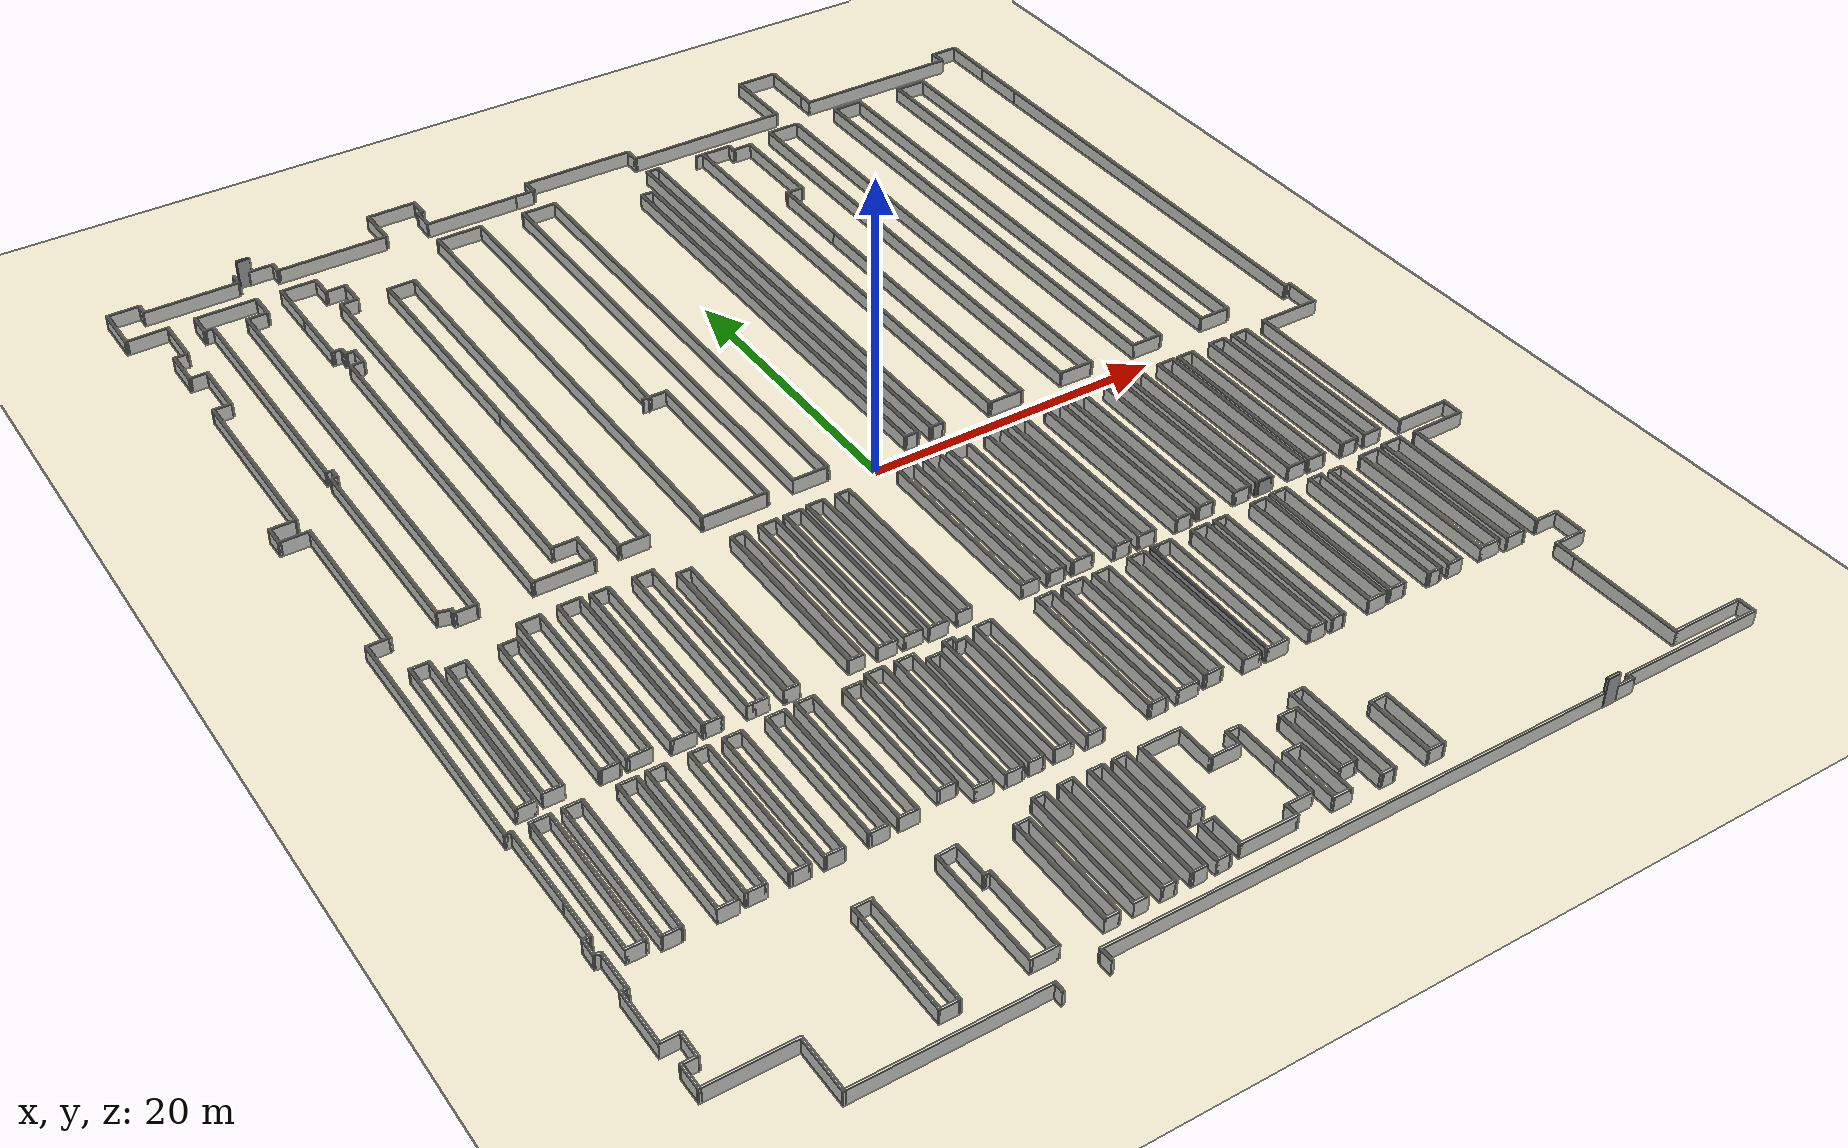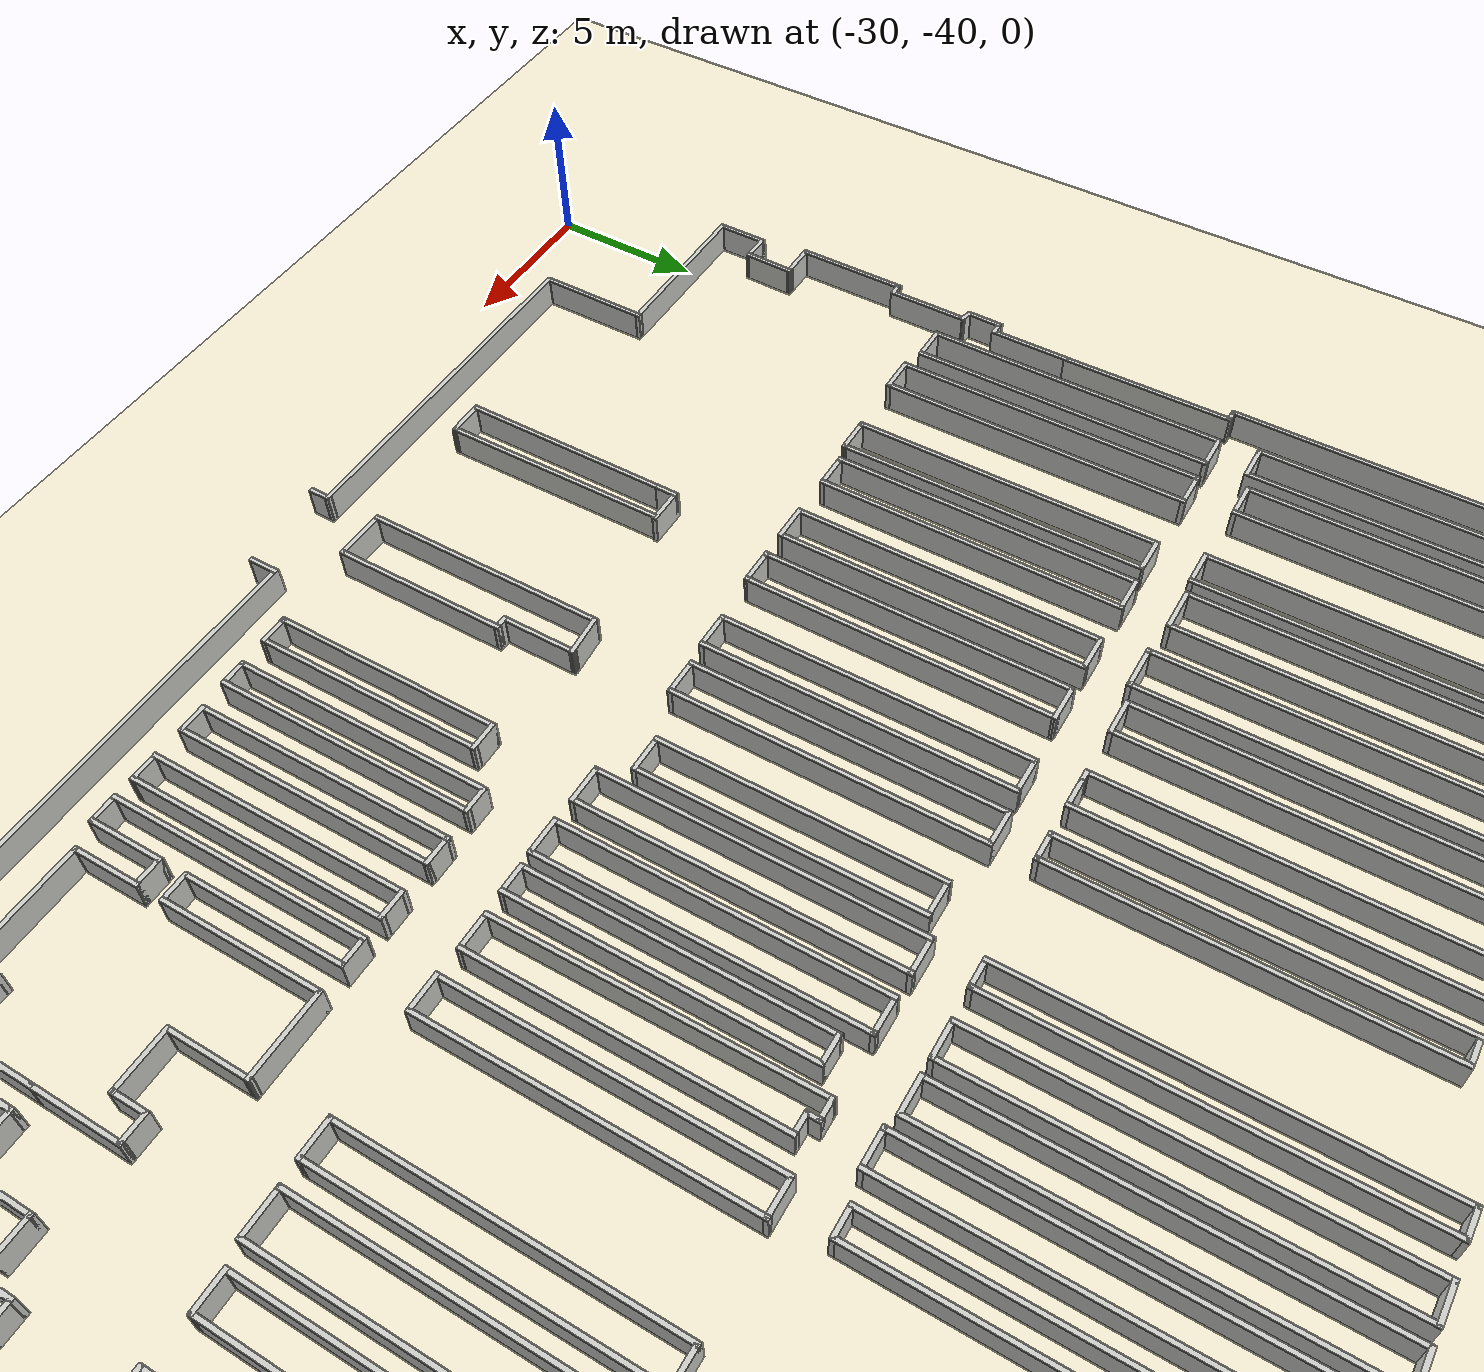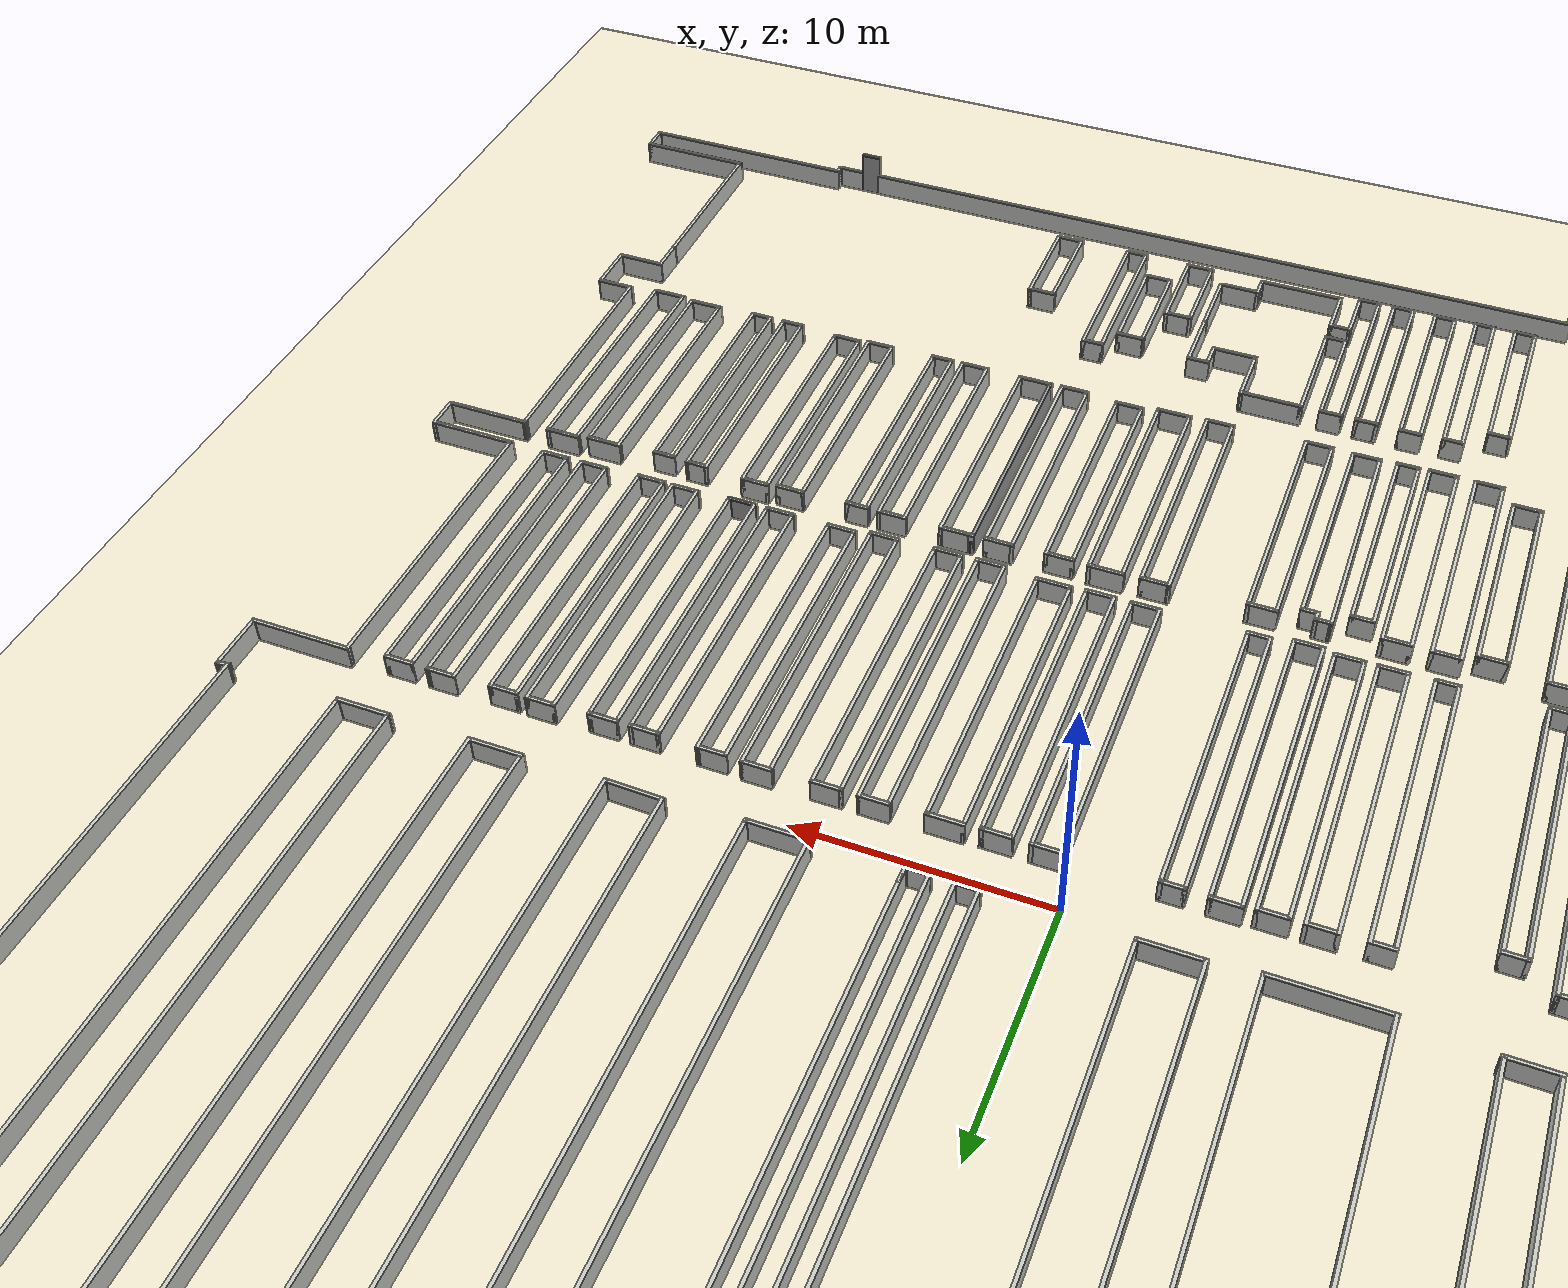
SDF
<sdf version="1.7">
 <world name="default">
  <plugin filename="ignition-gazebo-physics-system" name="ignition::gazebo::systems::Physics"/>
  <plugin filename="ignition-gazebo-user-commands-system" name="ignition::gazebo::systems::UserCommands"/>
  <plugin filename="ignition-gazebo-scene-broadcaster-system" name="ignition::gazebo::systems::SceneBroadcaster"/>
  <plugin filename="ignition-gazebo-sensors-system" name="ignition::gazebo::systems::Sensors">
   <render_engine>ogre2</render_engine>
  </plugin>
  <light name="sun" type="directional">
   <pose>0 0 10 0 -0 0</pose>
   <diffuse>0.8 0.8 0.8 1</diffuse>
   <specular>0.2 0.2 0.2 1</specular>
   <attenuation>
    <range>1000</range>
    <constant>0.9</constant>
    <linear>0.01</linear>
    <quadratic>0.001</quadratic>
   </attenuation>
   <direction>-0.5 0.1 -0.9</direction>
   <spot><inner_angle>0</inner_angle><outer_angle>0</outer_angle><falloff>0</falloff></spot>
  </light>
  <model name="ground_plane">
   <static>1</static>
   <link name="link">
    <collision name="collision">
     <geometry><plane><normal>0 0 1</normal><size>100 100</size></plane></geometry>
     <surface><friction><ode><mu>100</mu><mu2>50</mu2></ode></friction></surface>
    </collision>
    <visual name="visual">
     <cast_shadows>0</cast_shadows>
     <geometry><plane><normal>0 0 1</normal><size>100 100</size></plane></geometry>
     <material>
      <ambient>0.85 0.82 0.72 1</ambient>
      <diffuse>0.95 0.92 0.82 1</diffuse>
      <specular>0.05 0.05 0.05 1</specular>
     </material>
    </visual>
   </link>
  </model>
  <gravity>0 0 -9.8</gravity>
  <magnetic_field>6e-06 2.3e-05 -4.2e-05</magnetic_field>
  <atmosphere type="adiabatic"/>
  <physics type="ode">
   <max_step_size>0.001</max_step_size>
   <real_time_factor>1</real_time_factor>
   <real_time_update_rate>1000</real_time_update_rate>
  </physics>
  <scene>
   <ambient>0.7 0.7 0.7 1</ambient>
   <background>0.75 0.85 0.95 1</background>
   <shadows>false</shadows>
  </scene>
  <audio><device>default</device></audio>
  <spherical_coordinates>
   <surface_model>EARTH_WGS84</surface_model>
   <latitude_deg>0</latitude_deg>
   <longitude_deg>0</longitude_deg>
   <elevation>0</elevation>
   <heading_deg>0</heading_deg>
  </spherical_coordinates>
  <model name="warehouse">
   <pose>0.004046 2.00696 0 0 -0 0</pose>
   <link name="Door_0">
    <collision name="Door_0_Collision">
     <geometry><box><size>0.9 0.17 2</size></box></geometry>
     <pose>0 0 1 0 -0 0</pose>
    </collision>
    <visual name="Door_0_Visual">
     <pose>0 0 1 0 -0 0</pose>
     <geometry><box><size>0.9 0.17 2</size></box></geometry>
     <material>
      <script><uri>file://media/materials/scripts/gazebo.material</uri><name>Gazebo/Grey</name></script>
     </material>
    </visual>
    <pose>-23.59 36.7086 0 0 -0 0</pose>
   </link>
   <link name="Door_1">
    <collision name="Door_1_Collision">
     <geometry><box><size>0.9 0.17 2</size></box></geometry>
     <pose>0 0 1 0 -0 0</pose>
    </collision>
    <visual name="Door_1_Visual">
     <pose>0 0 1 0 -0 0</pose>
     <geometry><box><size>0.9 0.17 2</size></box></geometry>
     <material>
      <script><uri>file://media/materials/scripts/gazebo.material</uri><name>Gazebo/Grey</name></script>
     </material>
    </visual>
    <pose>21.5476 -39.6968 0 0 -0 0</pose>
   </link>
   <link name="Wall_100">
    <collision name="Wall_100_Collision">
     <geometry><box><size>1.75 0.15 1</size></box></geometry>
     <pose>0 0 0.5 0 -0 0</pose>
    </collision>
    <visual name="Wall_100_Visual">
     <pose>0 0 0.5 0 -0 0</pose>
     <geometry><box><size>1.75 0.15 1</size></box></geometry>
     <material>
      <script><uri>file://media/materials/scripts/gazebo.material</uri><name>Gazebo/CeilingTiled</name></script>
      <ambient>1 1 1 1</ambient>
     </material>
     <meta><layer>0</layer></meta>
    </visual>
    <pose>-30.8775 -34.2135 0 0 -0 1.54893</pose>
   </link>
   <link name="Wall_101">
    <collision name="Wall_101_Collision">
     <geometry><box><size>1.28487 0.15 1</size></box></geometry>
     <pose>0 0 0.5 0 -0 0</pose>
    </collision>
    <visual name="Wall_101_Visual">
     <pose>0 0 0.5 0 -0 0</pose>
     <geometry><box><size>1.28487 0.15 1</size></box></geometry>
     <material>
      <script><uri>file://media/materials/scripts/gazebo.material</uri><name>Gazebo/CeilingTiled</name></script>
      <ambient>1 1 1 1</ambient>
     </material>
     <meta><layer>0</layer></meta>
    </visual>
    <pose>-31.4275 -33.4135 0 0 -0 3.14159</pose>
   </link>
   <link name="Wall_102">
    <collision name="Wall_102_Collision">
     <geometry><box><size>3.75 0.15 1</size></box></geometry>
     <pose>0 0 0.5 0 -0 0</pose>
    </collision>
    <visual name="Wall_102_Visual">
     <pose>0 0 0.5 0 -0 0</pose>
     <geometry><box><size>3.75 0.15 1</size></box></geometry>
     <material>
      <script><uri>file://media/materials/scripts/gazebo.material</uri><name>Gazebo/CeilingTiled</name></script>
      <ambient>1 1 1 1</ambient>
     </material>
     <meta><layer>0</layer></meta>
    </visual>
    <pose>-31.995 -31.6135 0 0 -0 1.5708</pose>
   </link>
   <link name="Wall_103">
    <collision name="Wall_103_Collision">
     <geometry><box><size>0.5 0.15 1</size></box></geometry>
     <pose>0 0 0.5 0 -0 0</pose>
    </collision>
    <visual name="Wall_103_Visual">
     <pose>0 0 0.5 0 -0 0</pose>
     <geometry><box><size>0.5 0.15 1</size></box></geometry>
     <material>
      <script><uri>file://media/materials/scripts/gazebo.material</uri><name>Gazebo/CeilingTiled</name></script>
      <ambient>1 1 1 1</ambient>
     </material>
     <meta><layer>0</layer></meta>
    </visual>
    <pose>-31.82 -29.8135 0 0 -0 0</pose>
   </link>
   <link name="Wall_104">
    <collision name="Wall_104_Collision">
     <geometry><box><size>2.75 0.15 1</size></box></geometry>
     <pose>0 0 0.5 0 -0 0</pose>
    </collision>
    <visual name="Wall_104_Visual">
     <pose>0 0 0.5 0 -0 0</pose>
     <geometry><box><size>2.75 0.15 1</size></box></geometry>
     <material>
      <script><uri>file://media/materials/scripts/gazebo.material</uri><name>Gazebo/CeilingTiled</name></script>
      <ambient>1 1 1 1</ambient>
     </material>
     <meta><layer>0</layer></meta>
    </visual>
    <pose>-31.645 -28.5135 0 0 -0 1.5708</pose>
   </link>
   <link name="Wall_105">
    <collision name="Wall_105_Collision">
     <geometry><box><size>0.5 0.15 1</size></box></geometry>
     <pose>0 0 0.5 0 -0 0</pose>
    </collision>
    <visual name="Wall_105_Visual">
     <pose>0 0 0.5 0 -0 0</pose>
     <geometry><box><size>0.5 0.15 1</size></box></geometry>
     <material>
      <script><uri>file://media/materials/scripts/gazebo.material</uri><name>Gazebo/CeilingTiled</name></script>
      <ambient>1 1 1 1</ambient>
     </material>
     <meta><layer>0</layer></meta>
    </visual>
    <pose>-31.814 -27.168 0 0 -0 2.8786</pose>
   </link>
   <link name="Wall_106">
    <collision name="Wall_106_Collision">
     <geometry><box><size>1.25 0.15 1</size></box></geometry>
     <pose>0 0 0.5 0 -0 0</pose>
    </collision>
    <visual name="Wall_106_Visual">
     <pose>0 0 0.5 0 -0 0</pose>
     <geometry><box><size>1.25 0.15 1</size></box></geometry>
     <material>
      <script><uri>file://media/materials/scripts/gazebo.material</uri><name>Gazebo/CeilingTiled</name></script>
      <ambient>1 1 1 1</ambient>
     </material>
     <meta><layer>0</layer></meta>
    </visual>
    <pose>-31.976 -26.5725 0 0 -0 1.55807</pose>
   </link>
   <link name="Wall_107">
    <collision name="Wall_107_Collision">
     <geometry><box><size>0.532225 0.15 1</size></box></geometry>
     <pose>0 0 0.5 0 -0 0</pose>
    </collision>
    <visual name="Wall_107_Visual">
     <pose>0 0 0.5 0 -0 0</pose>
     <geometry><box><size>0.532225 0.15 1</size></box></geometry>
     <material>
      <script><uri>file://media/materials/scripts/gazebo.material</uri><name>Gazebo/CeilingTiled</name></script>
      <ambient>1 1 1 1</ambient>
     </material>
     <meta><layer>0</layer></meta>
    </visual>
    <pose>-31.7775 -26.0225 0 0 -0 0</pose>
   </link>
   <link name="Wall_108">
    <collision name="Wall_108_Collision">
     <geometry><box><size>2.75 0.15 1</size></box></geometry>
     <pose>0 0 0.5 0 -0 0</pose>
    </collision>
    <visual name="Wall_108_Visual">
     <pose>0 0 0.5 0 -0 0</pose>
     <geometry><box><size>2.75 0.15 1</size></box></geometry>
     <material>
      <script><uri>file://media/materials/scripts/gazebo.material</uri><name>Gazebo/CeilingTiled</name></script>
      <ambient>1 1 1 1</ambient>
     </material>
     <meta><layer>0</layer></meta>
    </visual>
    <pose>-31.5875 -24.7225 0 0 -0 1.57191</pose>
   </link>
   <link name="Wall_109">
    <collision name="Wall_109_Collision">
     <geometry><box><size>5.75 0.15 1</size></box></geometry>
     <pose>0 0 0.5 0 -0 0</pose>
    </collision>
    <visual name="Wall_109_Visual">
     <pose>0 0 0.5 0 -0 0</pose>
     <geometry><box><size>5.75 0.15 1</size></box></geometry>
     <material>
      <script><uri>file://media/materials/scripts/gazebo.material</uri><name>Gazebo/CeilingTiled</name></script>
      <ambient>1 1 1 1</ambient>
     </material>
     <meta><layer>0</layer></meta>
    </visual>
    <pose>-31.6073 -20.6225 0 0 -0 1.57998</pose>
   </link>
   <link name="Wall_11">
    <collision name="Wall_11_Collision">
     <geometry><box><size>3.5 0.15 1</size></box></geometry>
     <pose>0 0 0.5 0 -0 0</pose>
    </collision>
    <visual name="Wall_11_Visual">
     <pose>0 0 0.5 0 -0 0</pose>
     <geometry><box><size>3.5 0.15 1</size></box></geometry>
     <material>
      <script><uri>file://media/materials/scripts/gazebo.material</uri><name>Gazebo/CeilingTiled</name></script>
      <ambient>1 1 1 1</ambient>
     </material>
     <meta><layer>0</layer></meta>
    </visual>
    <pose>-32.777 35.0175 0 0 -0 1.5708</pose>
   </link>
   <link name="Wall_110">
    <collision name="Wall_110_Collision">
     <geometry><box><size>0.5 0.15 1</size></box></geometry>
     <pose>0 0 0.5 0 -0 0</pose>
    </collision>
    <visual name="Wall_110_Visual">
     <pose>0 0 0.5 0 -0 0</pose>
     <geometry><box><size>0.5 0.15 1</size></box></geometry>
     <material>
      <script><uri>file://media/materials/scripts/gazebo.material</uri><name>Gazebo/CeilingTiled</name></script>
      <ambient>1 1 1 1</ambient>
     </material>
     <meta><layer>0</layer></meta>
    </visual>
    <pose>-31.808 -17.8225 0 0 -0 3.14159</pose>
   </link>
   <link name="Wall_111">
    <collision name="Wall_111_Collision">
     <geometry><box><size>16.75 0.15 1</size></box></geometry>
     <pose>0 0 0.5 0 -0 0</pose>
    </collision>
    <visual name="Wall_111_Visual">
     <pose>0 0 0.5 0 -0 0</pose>
     <geometry><box><size>16.75 0.15 1</size></box></geometry>
     <material>
      <script><uri>file://media/materials/scripts/gazebo.material</uri><name>Gazebo/CeilingTiled</name></script>
      <ambient>1 1 1 1</ambient>
     </material>
     <meta><layer>0</layer></meta>
    </visual>
    <pose>-31.983 -9.5225 0 0 -0 1.5708</pose>
   </link>
   <link name="Wall_112">
    <collision name="Wall_112_Collision">
     <geometry><box><size>1.5 0.15 1</size></box></geometry>
     <pose>0 0 0.5 0 -0 0</pose>
    </collision>
    <visual name="Wall_112_Visual">
     <pose>0 0 0.5 0 -0 0</pose>
     <geometry><box><size>1.5 0.15 1</size></box></geometry>
     <material>
      <script><uri>file://media/materials/scripts/gazebo.material</uri><name>Gazebo/CeilingTiled</name></script>
      <ambient>1 1 1 1</ambient>
     </material>
     <meta><layer>0</layer></meta>
    </visual>
    <pose>-31.308 -1.2225 0 0 -0 0</pose>
   </link>
   <link name="Wall_113">
    <collision name="Wall_113_Collision">
     <geometry><box><size>10.9806 0.15 1</size></box></geometry>
     <pose>0 0 0.5 0 -0 0</pose>
    </collision>
    <visual name="Wall_113_Visual">
     <pose>0 0 0.5 0 -0 0</pose>
     <geometry><box><size>10.9806 0.15 1</size></box></geometry>
     <material>
      <script><uri>file://media/materials/scripts/gazebo.material</uri><name>Gazebo/CeilingTiled</name></script>
      <ambient>1 1 1 1</ambient>
     </material>
     <meta><layer>0</layer></meta>
    </visual>
    <pose>-30.6285 4.1925 0 0 -0 1.56997</pose>
   </link>
   <link name="Wall_114">
    <collision name="Wall_114_Collision">
     <geometry><box><size>1.99967 0.15 1</size></box></geometry>
     <pose>0 0 0.5 0 -0 0</pose>
    </collision>
    <visual name="Wall_114_Visual">
     <pose>0 0 0.5 0 -0 0</pose>
     <geometry><box><size>1.99967 0.15 1</size></box></geometry>
     <material>
      <script><uri>file://media/materials/scripts/gazebo.material</uri><name>Gazebo/CeilingTiled</name></script>
      <ambient>1 1 1 1</ambient>
     </material>
     <meta><layer>0</layer></meta>
    </visual>
    <pose>-31.5485 9.608 0 0 -0 3.14105</pose>
   </link>
   <link name="Wall_115">
    <collision name="Wall_115_Collision">
     <geometry><box><size>1.51948 0.15 1</size></box></geometry>
     <pose>0 0 0.5 0 -0 0</pose>
    </collision>
    <visual name="Wall_115_Visual">
     <pose>0 0 0.5 0 -0 0</pose>
     <geometry><box><size>1.51948 0.15 1</size></box></geometry>
     <material>
      <script><uri>file://media/materials/scripts/gazebo.material</uri><name>Gazebo/CeilingTiled</name></script>
      <ambient>1 1 1 1</ambient>
     </material>
     <meta><layer>0</layer></meta>
    </visual>
    <pose>-32.4735 10.293 0 0 -0 1.57153</pose>
   </link>
   <link name="Wall_116">
    <collision name="Wall_116_Collision">
     <geometry><box><size>1.75033 0.15 1</size></box></geometry>
     <pose>0 0 0.5 0 -0 0</pose>
    </collision>
    <visual name="Wall_116_Visual">
     <pose>0 0 0.5 0 -0 0</pose>
     <geometry><box><size>1.75033 0.15 1</size></box></geometry>
     <material>
      <script><uri>file://media/materials/scripts/gazebo.material</uri><name>Gazebo/CeilingTiled</name></script>
      <ambient>1 1 1 1</ambient>
     </material>
     <meta><layer>0</layer></meta>
    </visual>
    <pose>-31.6735 10.9775 0 0 -0 0</pose>
   </link>
   <link name="Wall_117">
    <collision name="Wall_117_Collision">
     <geometry><box><size>12.75 0.15 1</size></box></geometry>
     <pose>0 0 0.5 0 -0 0</pose>
    </collision>
    <visual name="Wall_117_Visual">
     <pose>0 0 0.5 0 -0 0</pose>
     <geometry><box><size>12.75 0.15 1</size></box></geometry>
     <material>
      <script><uri>file://media/materials/scripts/gazebo.material</uri><name>Gazebo/CeilingTiled</name></script>
      <ambient>1 1 1 1</ambient>
     </material>
     <meta><layer>0</layer></meta>
    </visual>
    <pose>-30.878 17.2775 0 0 -0 1.57159</pose>
   </link>
   <link name="Wall_118">
    <collision name="Wall_118_Collision">
     <geometry><box><size>1.27933 0.15 1</size></box></geometry>
     <pose>0 0 0.5 0 -0 0</pose>
    </collision>
    <visual name="Wall_118_Visual">
     <pose>0 0 0.5 0 -0 0</pose>
     <geometry><box><size>1.27933 0.15 1</size></box></geometry>
     <material>
      <script><uri>file://media/materials/scripts/gazebo.material</uri><name>Gazebo/CeilingTiled</name></script>
      <ambient>1 1 1 1</ambient>
     </material>
     <meta><layer>0</layer></meta>
    </visual>
    <pose>-30.3185 23.5775 0 0 -0 0</pose>
   </link>
   <link name="Wall_119">
    <collision name="Wall_119_Collision">
     <geometry><box><size>4 0.15 1</size></box></geometry>
     <pose>0 0 0.5 0 -0 0</pose>
    </collision>
    <visual name="Wall_119_Visual">
     <pose>0 0 0.5 0 -0 0</pose>
     <geometry><box><size>4 0.15 1</size></box></geometry>
     <material>
      <script><uri>file://media/materials/scripts/gazebo.material</uri><name>Gazebo/CeilingTiled</name></script>
      <ambient>1 1 1 1</ambient>
     </material>
     <meta><layer>0</layer></meta>
    </visual>
    <pose>-29.7535 25.5025 0 0 -0 1.57054</pose>
   </link>
   <link name="Wall_12">
    <collision name="Wall_12_Collision">
     <geometry><box><size>2.25 0.15 1</size></box></geometry>
     <pose>0 0 0.5 0 -0 0</pose>
    </collision>
    <visual name="Wall_12_Visual">
     <pose>0 0 0.5 0 -0 0</pose>
     <geometry><box><size>2.25 0.15 1</size></box></geometry>
     <material>
      <script><uri>file://media/materials/scripts/gazebo.material</uri><name>Gazebo/CeilingTiled</name></script>
      <ambient>1 1 1 1</ambient>
     </material>
     <meta><layer>0</layer></meta>
    </visual>
    <pose>-31.727 36.6925 0 0 -0 0</pose>
   </link>
   <link name="Wall_120">
    <collision name="Wall_120_Collision">
     <geometry><box><size>1.28 0.15 1</size></box></geometry>
     <pose>0 0 0.5 0 -0 0</pose>
    </collision>
    <visual name="Wall_120_Visual">
     <pose>0 0 0.5 0 -0 0</pose>
     <geometry><box><size>1.28 0.15 1</size></box></geometry>
     <material>
      <script><uri>file://media/materials/scripts/gazebo.material</uri><name>Gazebo/CeilingTiled</name></script>
      <ambient>1 1 1 1</ambient>
     </material>
     <meta><layer>0</layer></meta>
    </visual>
    <pose>-30.318 27.4275 0 0 -0 3.14159</pose>
   </link>
   <link name="Wall_121">
    <collision name="Wall_121_Collision">
     <geometry><box><size>2.75 0.15 1</size></box></geometry>
     <pose>0 0 0.5 0 -0 0</pose>
    </collision>
    <visual name="Wall_121_Visual">
     <pose>0 0 0.5 0 -0 0</pose>
     <geometry><box><size>2.75 0.15 1</size></box></geometry>
     <material>
      <script><uri>file://media/materials/scripts/gazebo.material</uri><name>Gazebo/CeilingTiled</name></script>
      <ambient>1 1 1 1</ambient>
     </material>
     <meta><layer>0</layer></meta>
    </visual>
    <pose>-30.883 28.7275 0 0 -0 1.5708</pose>
   </link>
   <link name="Wall_122">
    <collision name="Wall_122_Collision">
     <geometry><box><size>1 0.15 1</size></box></geometry>
     <pose>0 0 0.5 0 -0 0</pose>
    </collision>
    <visual name="Wall_122_Visual">
     <pose>0 0 0.5 0 -0 0</pose>
     <geometry><box><size>1 0.15 1</size></box></geometry>
     <material>
      <script><uri>file://media/materials/scripts/gazebo.material</uri><name>Gazebo/CeilingTiled</name></script>
      <ambient>1 1 1 1</ambient>
     </material>
     <meta><layer>0</layer></meta>
    </visual>
    <pose>-30.458 30.0275 0 0 -0 0</pose>
   </link>
   <link name="Wall_123">
    <collision name="Wall_123_Collision">
     <geometry><box><size>3.5 0.15 1</size></box></geometry>
     <pose>0 0 0.5 0 -0 0</pose>
    </collision>
    <visual name="Wall_123_Visual">
     <pose>0 0 0.5 0 -0 0</pose>
     <geometry><box><size>3.5 0.15 1</size></box></geometry>
     <material>
      <script><uri>file://media/materials/scripts/gazebo.material</uri><name>Gazebo/CeilingTiled</name></script>
      <ambient>1 1 1 1</ambient>
     </material>
     <meta><layer>0</layer></meta>
    </visual>
    <pose>-30.033 31.7025 0 0 -0 1.5708</pose>
   </link>
   <link name="Wall_124">
    <collision name="Wall_124_Collision">
     <geometry><box><size>2.89418 0.15 1</size></box></geometry>
     <pose>0 0 0.5 0 -0 0</pose>
    </collision>
    <visual name="Wall_124_Visual">
     <pose>0 0 0.5 0 -0 0</pose>
     <geometry><box><size>2.89418 0.15 1</size></box></geometry>
     <material>
      <script><uri>file://media/materials/scripts/gazebo.material</uri><name>Gazebo/CeilingTiled</name></script>
      <ambient>1 1 1 1</ambient>
     </material>
     <meta><layer>0</layer></meta>
    </visual>
    <pose>-31.405 33.36 0 0 -0 -3.12884</pose>
   </link>
   <link name="Wall_126">
    <collision name="Wall_126_Collision">
     <geometry><box><size>4.25 0.15 1</size></box></geometry>
     <pose>0 0 0.5 0 -0 0</pose>
    </collision>
    <visual name="Wall_126_Visual">
     <pose>0 0 0.5 0 -0 0</pose>
     <geometry><box><size>4.25 0.15 1</size></box></geometry>
     <material>
      <script><uri>file://media/materials/scripts/gazebo.material</uri><name>Gazebo/CeilingTiled</name></script>
      <ambient>1 1 1 1</ambient>
     </material>
     <meta><layer>0</layer></meta>
    </visual>
    <pose>-26.163 33.4445 0 0 -0 0</pose>
   </link>
   <link name="Wall_127">
    <collision name="Wall_127_Collision">
     <geometry><box><size>2 0.15 1</size></box></geometry>
     <pose>0 0 0.5 0 -0 0</pose>
    </collision>
    <visual name="Wall_127_Visual">
     <pose>0 0 0.5 0 -0 0</pose>
     <geometry><box><size>2 0.15 1</size></box></geometry>
     <material>
      <script><uri>file://media/materials/scripts/gazebo.material</uri><name>Gazebo/CeilingTiled</name></script>
      <ambient>1 1 1 1</ambient>
     </material>
     <meta><layer>0</layer></meta>
    </visual>
    <pose>-24.113 32.5195 0 0 -0 -1.5708</pose>
   </link>
   <link name="Wall_128">
    <collision name="Wall_128_Collision">
     <geometry><box><size>1.5 0.15 1</size></box></geometry>
     <pose>0 0 0.5 0 -0 0</pose>
    </collision>
    <visual name="Wall_128_Visual">
     <pose>0 0 0.5 0 -0 0</pose>
     <geometry><box><size>1.5 0.15 1</size></box></geometry>
     <material>
      <script><uri>file://media/materials/scripts/gazebo.material</uri><name>Gazebo/CeilingTiled</name></script>
      <ambient>1 1 1 1</ambient>
     </material>
     <meta><layer>0</layer></meta>
    </visual>
    <pose>-24.788 31.5945 0 0 -0 3.14159</pose>
   </link>
   <link name="Wall_129">
    <collision name="Wall_129_Collision">
     <geometry><box><size>33 0.15 1</size></box></geometry>
     <pose>0 0 0.5 0 -0 0</pose>
    </collision>
    <visual name="Wall_129_Visual">
     <pose>0 0 0.5 0 -0 0</pose>
     <geometry><box><size>33 0.15 1</size></box></geometry>
     <material>
      <script><uri>file://media/materials/scripts/gazebo.material</uri><name>Gazebo/CeilingTiled</name></script>
      <ambient>1 1 1 1</ambient>
     </material>
     <meta><layer>0</layer></meta>
    </visual>
    <pose>-25.463 15.1695 0 0 -0 -1.5708</pose>
   </link>
   <link name="Wall_13">
    <collision name="Wall_13_Collision">
     <geometry><box><size>1 0.15 1</size></box></geometry>
     <pose>0 0 0.5 0 -0 0</pose>
    </collision>
    <visual name="Wall_13_Visual">
     <pose>0 0 0.5 0 -0 0</pose>
     <geometry><box><size>1 0.15 1</size></box></geometry>
     <material>
      <script><uri>file://media/materials/scripts/gazebo.material</uri><name>Gazebo/CeilingTiled</name></script>
      <ambient>1 1 1 1</ambient>
     </material>
     <meta><layer>0</layer></meta>
    </visual>
    <pose>-30.677 36.2675 0 0 -0 -1.5708</pose>
   </link>
   <link name="Wall_130">
    <collision name="Wall_130_Collision">
     <geometry><box><size>1.51536 0.15 1</size></box></geometry>
     <pose>0 0 0.5 0 -0 0</pose>
    </collision>
    <visual name="Wall_130_Visual">
     <pose>0 0 0.5 0 -0 0</pose>
     <geometry><box><size>1.51536 0.15 1</size></box></geometry>
     <material>
      <script><uri>file://media/materials/scripts/gazebo.material</uri><name>Gazebo/CeilingTiled</name></script>
      <ambient>1 1 1 1</ambient>
     </material>
     <meta><layer>0</layer></meta>
    </visual>
    <pose>-26.1454 -1.248 0 0 -0 3.1306</pose>
   </link>
   <link name="Wall_131">
    <collision name="Wall_131_Collision">
     <geometry><box><size>0.5 0.15 1</size></box></geometry>
     <pose>0 0 0.5 0 -0 0</pose>
    </collision>
    <visual name="Wall_131_Visual">
     <pose>0 0 0.5 0 -0 0</pose>
     <geometry><box><size>0.5 0.15 1</size></box></geometry>
     <material>
      <script><uri>file://media/materials/scripts/gazebo.material</uri><name>Gazebo/CeilingTiled</name></script>
      <ambient>1 1 1 1</ambient>
     </material>
     <meta><layer>0</layer></meta>
    </visual>
    <pose>-26.8277 -1.08016 0 0 -0 1.5708</pose>
   </link>
   <link name="Wall_132">
    <collision name="Wall_132_Collision">
     <geometry><box><size>0.981991 0.15 1</size></box></geometry>
     <pose>0 0 0.5 0 -0 0</pose>
    </collision>
    <visual name="Wall_132_Visual">
     <pose>0 0 0.5 0 -0 0</pose>
     <geometry><box><size>0.981991 0.15 1</size></box></geometry>
     <material>
      <script><uri>file://media/materials/scripts/gazebo.material</uri><name>Gazebo/CeilingTiled</name></script>
      <ambient>1 1 1 1</ambient>
     </material>
     <meta><layer>0</layer></meta>
    </visual>
    <pose>-27.2309 -0.788 0 0 -0 2.89263</pose>
   </link>
   <link name="Wall_133">
    <collision name="Wall_133_Collision">
     <geometry><box><size>14.25 0.15 1</size></box></geometry>
     <pose>0 0 0.5 0 -0 0</pose>
    </collision>
    <visual name="Wall_133_Visual">
     <pose>0 0 0.5 0 -0 0</pose>
     <geometry><box><size>14.25 0.15 1</size></box></geometry>
     <material>
      <script><uri>file://media/materials/scripts/gazebo.material</uri><name>Gazebo/CeilingTiled</name></script>
      <ambient>1 1 1 1</ambient>
     </material>
     <meta><layer>0</layer></meta>
    </visual>
    <pose>-27.634 6.3645 0 0 -0 1.5708</pose>
   </link>
   <link name="Wall_134">
    <collision name="Wall_134_Collision">
     <geometry><box><size>0.5 0.15 1</size></box></geometry>
     <pose>0 0 0.5 0 -0 0</pose>
    </collision>
    <visual name="Wall_134_Visual">
     <pose>0 0 0.5 0 -0 0</pose>
     <geometry><box><size>0.5 0.15 1</size></box></geometry>
     <material>
      <script><uri>file://media/materials/scripts/gazebo.material</uri><name>Gazebo/CeilingTiled</name></script>
      <ambient>1 1 1 1</ambient>
     </material>
     <meta><layer>0</layer></meta>
    </visual>
    <pose>-27.465 13.46 0 0 -0 0.262995</pose>
   </link>
   <link name="Wall_135">
    <collision name="Wall_135_Collision">
     <geometry><box><size>0.75 0.15 1</size></box></geometry>
     <pose>0 0 0.5 0 -0 0</pose>
    </collision>
    <visual name="Wall_135_Visual">
     <pose>0 0 0.5 0 -0 0</pose>
     <geometry><box><size>0.75 0.15 1</size></box></geometry>
     <material>
      <script><uri>file://media/materials/scripts/gazebo.material</uri><name>Gazebo/CeilingTiled</name></script>
      <ambient>1 1 1 1</ambient>
     </material>
     <meta><layer>0</layer></meta>
    </visual>
    <pose>-27.296 13.8055 0 0 -0 1.5708</pose>
   </link>
   <link name="Wall_136">
    <collision name="Wall_136_Collision">
     <geometry><box><size>0.5 0.15 1</size></box></geometry>
     <pose>0 0 0.5 0 -0 0</pose>
    </collision>
    <visual name="Wall_136_Visual">
     <pose>0 0 0.5 0 -0 0</pose>
     <geometry><box><size>0.5 0.15 1</size></box></geometry>
     <material>
      <script><uri>file://media/materials/scripts/gazebo.material</uri><name>Gazebo/CeilingTiled</name></script>
      <ambient>1 1 1 1</ambient>
     </material>
     <meta><layer>0</layer></meta>
    </visual>
    <pose>-27.465 14.1505 0 0 -0 2.88136</pose>
   </link>
   <link name="Wall_137">
    <collision name="Wall_137_Collision">
     <geometry><box><size>17.75 0.15 1</size></box></geometry>
     <pose>0 0 0.5 0 -0 0</pose>
    </collision>
    <visual name="Wall_137_Visual">
     <pose>0 0 0.5 0 -0 0</pose>
     <geometry><box><size>17.75 0.15 1</size></box></geometry>
     <material>
      <script><uri>file://media/materials/scripts/gazebo.material</uri><name>Gazebo/CeilingTiled</name></script>
      <ambient>1 1 1 1</ambient>
     </material>
     <meta><layer>0</layer></meta>
    </visual>
    <pose>-27.634 22.9955 0 0 -0 1.5708</pose>
   </link>
   <link name="Wall_138">
    <collision name="Wall_138_Collision">
     <geometry><box><size>0.75 0.15 1</size></box></geometry>
     <pose>0 0 0.5 0 -0 0</pose>
    </collision>
    <visual name="Wall_138_Visual">
     <pose>0 0 0.5 0 -0 0</pose>
     <geometry><box><size>0.75 0.15 1</size></box></geometry>
     <material>
      <script><uri>file://media/materials/scripts/gazebo.material</uri><name>Gazebo/CeilingTiled</name></script>
      <ambient>1 1 1 1</ambient>
     </material>
     <meta><layer>0</layer></meta>
    </visual>
    <pose>-27.934 31.7955 0 0 -0 3.14159</pose>
   </link>
   <link name="Wall_139">
    <collision name="Wall_139_Collision">
     <geometry><box><size>1.79896 0.15 1</size></box></geometry>
     <pose>0 0 0.5 0 -0 0</pose>
    </collision>
    <visual name="Wall_139_Visual">
     <pose>0 0 0.5 0 -0 0</pose>
     <geometry><box><size>1.79896 0.15 1</size></box></geometry>
     <material>
      <script><uri>file://media/materials/scripts/gazebo.material</uri><name>Gazebo/CeilingTiled</name></script>
      <ambient>1 1 1 1</ambient>
     </material>
     <meta><layer>0</layer></meta>
    </visual>
    <pose>-28.2235 32.62 0 0 -0 1.55806</pose>
   </link>
   <link name="Wall_14">
    <collision name="Wall_14_Collision">
     <geometry><box><size>6.5 0.15 1</size></box></geometry>
     <pose>0 0 0.5 0 -0 0</pose>
    </collision>
    <visual name="Wall_14_Visual">
     <pose>0 0 0.5 0 -0 0</pose>
     <geometry><box><size>6.5 0.15 1</size></box></geometry>
     <material>
      <script><uri>file://media/materials/scripts/gazebo.material</uri><name>Gazebo/CeilingTiled</name></script>
      <ambient>1 1 1 1</ambient>
     </material>
     <meta><layer>0</layer></meta>
    </visual>
    <pose>-27.502 35.8425 0 0 -0 0</pose>
   </link>
   <link name="Wall_141">
    <collision name="Wall_141_Collision">
     <geometry><box><size>2.5 0.15 1</size></box></geometry>
     <pose>0 0 0.5 0 -0 0</pose>
    </collision>
    <visual name="Wall_141_Visual">
     <pose>0 0 0.5 0 -0 0</pose>
     <geometry><box><size>2.5 0.15 1</size></box></geometry>
     <material>
      <script><uri>file://media/materials/scripts/gazebo.material</uri><name>Gazebo/CeilingTiled</name></script>
      <ambient>1 1 1 1</ambient>
     </material>
     <meta><layer>0</layer></meta>
    </visual>
    <pose>-21.238 33.4255 0 0 -0 0</pose>
   </link>
   <link name="Wall_142">
    <collision name="Wall_142_Collision">
     <geometry><box><size>1.75 0.15 1</size></box></geometry>
     <pose>0 0 0.5 0 -0 0</pose>
    </collision>
    <visual name="Wall_142_Visual">
     <pose>0 0 0.5 0 -0 0</pose>
     <geometry><box><size>1.75 0.15 1</size></box></geometry>
     <material>
      <script><uri>file://media/materials/scripts/gazebo.material</uri><name>Gazebo/CeilingTiled</name></script>
      <ambient>1 1 1 1</ambient>
     </material>
     <meta><layer>0</layer></meta>
    </visual>
    <pose>-20.063 32.6255 0 0 -0 -1.5708</pose>
   </link>
   <link name="Wall_143">
    <collision name="Wall_143_Collision">
     <geometry><box><size>1.5 0.15 1</size></box></geometry>
     <pose>0 0 0.5 0 -0 0</pose>
    </collision>
    <visual name="Wall_143_Visual">
     <pose>0 0 0.5 0 -0 0</pose>
     <geometry><box><size>1.5 0.15 1</size></box></geometry>
     <material>
      <script><uri>file://media/materials/scripts/gazebo.material</uri><name>Gazebo/CeilingTiled</name></script>
      <ambient>1 1 1 1</ambient>
     </material>
     <meta><layer>0</layer></meta>
    </visual>
    <pose>-19.388 31.8255 0 0 -0 0</pose>
   </link>
   <link name="Wall_144">
    <collision name="Wall_144_Collision">
     <geometry><box><size>2 0.15 1</size></box></geometry>
     <pose>0 0 0.5 0 -0 0</pose>
    </collision>
    <visual name="Wall_144_Visual">
     <pose>0 0 0.5 0 -0 0</pose>
     <geometry><box><size>2 0.15 1</size></box></geometry>
     <material>
      <script><uri>file://media/materials/scripts/gazebo.material</uri><name>Gazebo/CeilingTiled</name></script>
      <ambient>1 1 1 1</ambient>
     </material>
     <meta><layer>0</layer></meta>
    </visual>
    <pose>-18.713 30.9005 0 0 -0 -1.5708</pose>
   </link>
   <link name="Wall_145">
    <collision name="Wall_145_Collision">
     <geometry><box><size>1.25 0.15 1</size></box></geometry>
     <pose>0 0 0.5 0 -0 0</pose>
    </collision>
    <visual name="Wall_145_Visual">
     <pose>0 0 0.5 0 -0 0</pose>
     <geometry><box><size>1.25 0.15 1</size></box></geometry>
     <material>
      <script><uri>file://media/materials/scripts/gazebo.material</uri><name>Gazebo/CeilingTiled</name></script>
      <ambient>1 1 1 1</ambient>
     </material>
     <meta><layer>0</layer></meta>
    </visual>
    <pose>-19.263 29.9755 0 0 -0 3.14159</pose>
   </link>
   <link name="Wall_146">
    <collision name="Wall_146_Collision">
     <geometry><box><size>29.25 0.15 1</size></box></geometry>
     <pose>0 0 0.5 0 -0 0</pose>
    </collision>
    <visual name="Wall_146_Visual">
     <pose>0 0 0.5 0 -0 0</pose>
     <geometry><box><size>29.25 0.15 1</size></box></geometry>
     <material>
      <script><uri>file://media/materials/scripts/gazebo.material</uri><name>Gazebo/CeilingTiled</name></script>
      <ambient>1 1 1 1</ambient>
     </material>
     <meta><layer>0</layer></meta>
    </visual>
    <pose>-19.813 15.4255 0 0 -0 -1.5708</pose>
   </link>
   <link name="Wall_147">
    <collision name="Wall_147_Collision">
     <geometry><box><size>1.75 0.15 1</size></box></geometry>
     <pose>0 0 0.5 0 -0 0</pose>
    </collision>
    <visual name="Wall_147_Visual">
     <pose>0 0 0.5 0 -0 0</pose>
     <geometry><box><size>1.75 0.15 1</size></box></geometry>
     <material>
      <script><uri>file://media/materials/scripts/gazebo.material</uri><name>Gazebo/CeilingTiled</name></script>
      <ambient>1 1 1 1</ambient>
     </material>
     <meta><layer>0</layer></meta>
    </visual>
    <pose>-19.013 0.8755 0 0 -0 0</pose>
   </link>
   <link name="Wall_148">
    <collision name="Wall_148_Collision">
     <geometry><box><size>2.25 0.15 1</size></box></geometry>
     <pose>0 0 0.5 0 -0 0</pose>
    </collision>
    <visual name="Wall_148_Visual">
     <pose>0 0 0.5 0 -0 0</pose>
     <geometry><box><size>2.25 0.15 1</size></box></geometry>
     <material>
      <script><uri>file://media/materials/scripts/gazebo.material</uri><name>Gazebo/CeilingTiled</name></script>
      <ambient>1 1 1 1</ambient>
     </material>
     <meta><layer>0</layer></meta>
    </visual>
    <pose>-18.213 -0.1745 0 0 -0 -1.5708</pose>
   </link>
   <link name="Wall_149">
    <collision name="Wall_149_Collision">
     <geometry><box><size>4 0.15 1</size></box></geometry>
     <pose>0 0 0.5 0 -0 0</pose>
    </collision>
    <visual name="Wall_149_Visual">
     <pose>0 0 0.5 0 -0 0</pose>
     <geometry><box><size>4 0.15 1</size></box></geometry>
     <material>
      <script><uri>file://media/materials/scripts/gazebo.material</uri><name>Gazebo/CeilingTiled</name></script>
      <ambient>1 1 1 1</ambient>
     </material>
     <meta><layer>0</layer></meta>
    </visual>
    <pose>-20.138 -1.2245 0 0 -0 3.14159</pose>
   </link>
   <link name="Wall_15">
    <collision name="Wall_15_Collision">
     <geometry><box><size>1 0.15 1</size></box></geometry>
     <pose>0 0 0.5 0 -0 0</pose>
    </collision>
    <visual name="Wall_15_Visual">
     <pose>0 0 0.5 0 -0 0</pose>
     <geometry><box><size>1 0.15 1</size></box></geometry>
     <material>
      <script><uri>file://media/materials/scripts/gazebo.material</uri><name>Gazebo/CeilingTiled</name></script>
      <ambient>1 1 1 1</ambient>
     </material>
     <meta><layer>0</layer></meta>
    </visual>
    <pose>-24.327 36.2675 0 0 -0 1.5708</pose>
   </link>
   <link name="Wall_150">
    <collision name="Wall_150_Collision">
     <geometry><box><size>24.75 0.15 1</size></box></geometry>
     <pose>0 0 0.5 0 -0 0</pose>
    </collision>
    <visual name="Wall_150_Visual">
     <pose>0 0 0.5 0 -0 0</pose>
     <geometry><box><size>24.75 0.15 1</size></box></geometry>
     <material>
      <script><uri>file://media/materials/scripts/gazebo.material</uri><name>Gazebo/CeilingTiled</name></script>
      <ambient>1 1 1 1</ambient>
     </material>
     <meta><layer>0</layer></meta>
    </visual>
    <pose>-22.063 11.0755 0 0 -0 1.5708</pose>
   </link>
   <link name="Wall_151">
    <collision name="Wall_151_Collision">
     <geometry><box><size>0.992104 0.15 1</size></box></geometry>
     <pose>0 0 0.5 0 -0 0</pose>
    </collision>
    <visual name="Wall_151_Visual">
     <pose>0 0 0.5 0 -0 0</pose>
     <geometry><box><size>0.992104 0.15 1</size></box></geometry>
     <material>
      <script><uri>file://media/materials/scripts/gazebo.material</uri><name>Gazebo/CeilingTiled</name></script>
      <ambient>1 1 1 1</ambient>
     </material>
     <meta><layer>0</layer></meta>
    </visual>
    <pose>-21.642 23.3795 0 0 -0 0.009421</pose>
   </link>
   <link name="Wall_152">
    <collision name="Wall_152_Collision">
     <geometry><box><size>1.5 0.15 1</size></box></geometry>
     <pose>0 0 0.5 0 -0 0</pose>
    </collision>
    <visual name="Wall_152_Visual">
     <pose>0 0 0.5 0 -0 0</pose>
     <geometry><box><size>1.5 0.15 1</size></box></geometry>
     <material>
      <script><uri>file://media/materials/scripts/gazebo.material</uri><name>Gazebo/CeilingTiled</name></script>
      <ambient>1 1 1 1</ambient>
     </material>
     <meta><layer>0</layer></meta>
    </visual>
    <pose>-21.2037 24.0584 0 0 -0 1.5708</pose>
   </link>
   <link name="Wall_153">
    <collision name="Wall_153_Collision">
     <geometry><box><size>0.74212 0.15 1</size></box></geometry>
     <pose>0 0 0.5 0 -0 0</pose>
    </collision>
    <visual name="Wall_153_Visual">
     <pose>0 0 0.5 0 -0 0</pose>
     <geometry><box><size>0.74212 0.15 1</size></box></geometry>
     <material>
      <script><uri>file://media/materials/scripts/gazebo.material</uri><name>Gazebo/CeilingTiled</name></script>
      <ambient>1 1 1 1</ambient>
     </material>
     <meta><layer>0</layer></meta>
    </visual>
    <pose>-21.517 24.7295 0 0 -0 -3.12819</pose>
   </link>
   <link name="Wall_154">
    <collision name="Wall_154_Collision">
     <geometry><box><size>0.75 0.15 1</size></box></geometry>
     <pose>0 0 0.5 0 -0 0</pose>
    </collision>
    <visual name="Wall_154_Visual">
     <pose>0 0 0.5 0 -0 0</pose>
     <geometry><box><size>0.75 0.15 1</size></box></geometry>
     <material>
      <script><uri>file://media/materials/scripts/gazebo.material</uri><name>Gazebo/CeilingTiled</name></script>
      <ambient>1 1 1 1</ambient>
     </material>
     <meta><layer>0</layer></meta>
    </visual>
    <pose>-21.813 25.0255 0 0 -0 1.5708</pose>
   </link>
   <link name="Wall_155">
    <collision name="Wall_155_Collision">
     <geometry><box><size>0.75 0.15 1</size></box></geometry>
     <pose>0 0 0.5 0 -0 0</pose>
    </collision>
    <visual name="Wall_155_Visual">
     <pose>0 0 0.5 0 -0 0</pose>
     <geometry><box><size>0.75 0.15 1</size></box></geometry>
     <material>
      <script><uri>file://media/materials/scripts/gazebo.material</uri><name>Gazebo/CeilingTiled</name></script>
      <ambient>1 1 1 1</ambient>
     </material>
     <meta><layer>0</layer></meta>
    </visual>
    <pose>-22.113 25.3255 0 0 -0 3.14159</pose>
   </link>
   <link name="Wall_156">
    <collision name="Wall_156_Collision">
     <geometry><box><size>4.5 0.15 1</size></box></geometry>
     <pose>0 0 0.5 0 -0 0</pose>
    </collision>
    <visual name="Wall_156_Visual">
     <pose>0 0 0.5 0 -0 0</pose>
     <geometry><box><size>4.5 0.15 1</size></box></geometry>
     <material>
      <script><uri>file://media/materials/scripts/gazebo.material</uri><name>Gazebo/CeilingTiled</name></script>
      <ambient>1 1 1 1</ambient>
     </material>
     <meta><layer>0</layer></meta>
    </visual>
    <pose>-22.413 27.5005 0 0 -0 1.5708</pose>
   </link>
   <link name="Wall_157">
    <collision name="Wall_157_Collision">
     <geometry><box><size>3.9 0.15 1</size></box></geometry>
     <pose>0 0 0.5 0 -0 0</pose>
    </collision>
    <visual name="Wall_157_Visual">
     <pose>0 0 0.5 0 -0 0</pose>
     <geometry><box><size>3.9 0.15 1</size></box></geometry>
     <material>
      <script><uri>file://media/materials/scripts/gazebo.material</uri><name>Gazebo/CeilingTiled</name></script>
      <ambient>1 1 1 1</ambient>
     </material>
     <meta><layer>0</layer></meta>
    </visual>
    <pose>-22.413 31.5505 0 0 -0 1.5708</pose>
   </link>
   <link name="Wall_18">
    <collision name="Wall_18_Collision">
     <geometry><box><size>1.75 0.15 1</size></box></geometry>
     <pose>0 0 0.5 0 -0 0</pose>
    </collision>
    <visual name="Wall_18_Visual">
     <pose>0 0 0.5 0 -0 0</pose>
     <geometry><box><size>1.75 0.15 1</size></box></geometry>
     <material>
      <script><uri>file://media/materials/scripts/gazebo.material</uri><name>Gazebo/CeilingTiled</name></script>
      <ambient>1 1 1 1</ambient>
     </material>
     <meta><layer>0</layer></meta>
    </visual>
    <pose>-22.472 36.6635 0 0 -0 0</pose>
   </link>
   <link name="Wall_182">
    <collision name="Wall_182_Collision">
     <geometry><box><size>15 0.15 1</size></box></geometry>
     <pose>0 0 0.5 0 -0 0</pose>
    </collision>
    <visual name="Wall_182_Visual">
     <pose>0 0 0.5 0 -0 0</pose>
     <geometry><box><size>15 0.15 1</size></box></geometry>
     <material>
      <script><uri>file://media/materials/scripts/gazebo.material</uri><name>Gazebo/CeilingTiled</name></script>
      <ambient>1 1 1 1</ambient>
     </material>
     <meta><layer>0</layer></meta>
    </visual>
    <pose>-16.538 6.4455 0 0 -0 1.5708</pose>
   </link>
   <link name="Wall_183">
    <collision name="Wall_183_Collision">
     <geometry><box><size>16.25 0.15 1</size></box></geometry>
     <pose>0 0 0.5 0 -0 0</pose>
    </collision>
    <visual name="Wall_183_Visual">
     <pose>0 0 0.5 0 -0 0</pose>
     <geometry><box><size>16.25 0.15 1</size></box></geometry>
     <material>
      <script><uri>file://media/materials/scripts/gazebo.material</uri><name>Gazebo/CeilingTiled</name></script>
      <ambient>1 1 1 1</ambient>
     </material>
     <meta><layer>0</layer></meta>
    </visual>
    <pose>-16.538 21.9205 0 0 -0 1.5708</pose>
   </link>
   <link name="Wall_188">
    <collision name="Wall_188_Collision">
     <geometry><box><size>35 0.15 1</size></box></geometry>
     <pose>0 0 0.5 0 -0 0</pose>
    </collision>
    <visual name="Wall_188_Visual">
     <pose>0 0 0.5 0 -0 0</pose>
     <geometry><box><size>35 0.15 1</size></box></geometry>
     <material>
      <script><uri>file://media/materials/scripts/gazebo.material</uri><name>Gazebo/CeilingTiled</name></script>
      <ambient>1 1 1 1</ambient>
     </material>
     <meta><layer>0</layer></meta>
    </visual>
    <pose>-11.3408 16.1385 0 0 -0 -1.56987</pose>
   </link>
   <link name="Wall_189">
    <collision name="Wall_189_Collision">
     <geometry><box><size>4.46 0.15 1</size></box></geometry>
     <pose>0 0 0.5 0 -0 0</pose>
    </collision>
    <visual name="Wall_189_Visual">
     <pose>0 0 0.5 0 -0 0</pose>
     <geometry><box><size>4.46 0.15 1</size></box></geometry>
     <material>
      <script><uri>file://media/materials/scripts/gazebo.material</uri><name>Gazebo/CeilingTiled</name></script>
      <ambient>1 1 1 1</ambient>
     </material>
     <meta><layer>0</layer></meta>
    </visual>
    <pose>-9.18945 -1.2865 0 0 -0 0</pose>
   </link>
   <link name="Wall_19">
    <collision name="Wall_19_Collision">
     <geometry><box><size>1 0.15 1</size></box></geometry>
     <pose>0 0 0.5 0 -0 0</pose>
    </collision>
    <visual name="Wall_19_Visual">
     <pose>0 0 0.5 0 -0 0</pose>
     <geometry><box><size>1 0.15 1</size></box></geometry>
     <material>
      <script><uri>file://media/materials/scripts/gazebo.material</uri><name>Gazebo/CeilingTiled</name></script>
      <ambient>1 1 1 1</ambient>
     </material>
     <meta><layer>0</layer></meta>
    </visual>
    <pose>-21.672 36.2385 0 0 -0 -1.5708</pose>
   </link>
   <link name="Wall_190">
    <collision name="Wall_190_Collision">
     <geometry><box><size>12 0.15 1</size></box></geometry>
     <pose>0 0 0.5 0 -0 0</pose>
    </collision>
    <visual name="Wall_190_Visual">
     <pose>0 0 0.5 0 -0 0</pose>
     <geometry><box><size>12 0.15 1</size></box></geometry>
     <material>
      <script><uri>file://media/materials/scripts/gazebo.material</uri><name>Gazebo/CeilingTiled</name></script>
      <ambient>1 1 1 1</ambient>
     </material>
     <meta><layer>0</layer></meta>
    </visual>
    <pose>-7.0308 4.6385 0 0 -0 1.57354</pose>
   </link>
   <link name="Wall_191">
    <collision name="Wall_191_Collision">
     <geometry><box><size>1.70993 0.15 1</size></box></geometry>
     <pose>0 0 0.5 0 -0 0</pose>
    </collision>
    <visual name="Wall_191_Visual">
     <pose>0 0 0.5 0 -0 0</pose>
     <geometry><box><size>1.70993 0.15 1</size></box></geometry>
     <material>
      <script><uri>file://media/materials/scripts/gazebo.material</uri><name>Gazebo/CeilingTiled</name></script>
      <ambient>1 1 1 1</ambient>
     </material>
     <meta><layer>0</layer></meta>
    </visual>
    <pose>-7.82704 10.5635 0 0 -0 3.14159</pose>
   </link>
   <link name="Wall_20">
    <collision name="Wall_20_Collision">
     <geometry><box><size>7.75 0.15 1</size></box></geometry>
     <pose>0 0 0.5 0 -0 0</pose>
    </collision>
    <visual name="Wall_20_Visual">
     <pose>0 0 0.5 0 -0 0</pose>
     <geometry><box><size>7.75 0.15 1</size></box></geometry>
     <material>
      <script><uri>file://media/materials/scripts/gazebo.material</uri><name>Gazebo/CeilingTiled</name></script>
      <ambient>1 1 1 1</ambient>
     </material>
     <meta><layer>0</layer></meta>
    </visual>
    <pose>-17.872 35.8135 0 0 -0 0</pose>
   </link>
   <link name="Wall_21">
    <collision name="Wall_21_Collision">
     <geometry><box><size>3 0.15 1</size></box></geometry>
     <pose>0 0 0.5 0 -0 0</pose>
    </collision>
    <visual name="Wall_21_Visual">
     <pose>0 0 0.5 0 -0 0</pose>
     <geometry><box><size>3 0.15 1</size></box></geometry>
     <material>
      <script><uri>file://media/materials/scripts/gazebo.material</uri><name>Gazebo/CeilingTiled</name></script>
      <ambient>1 1 1 1</ambient>
     </material>
     <meta><layer>0</layer></meta>
    </visual>
    <pose>-14.072 37.2385 0 0 -0 1.5708</pose>
   </link>
   <link name="Wall_22">
    <collision name="Wall_22_Collision">
     <geometry><box><size>3.5 0.15 1</size></box></geometry>
     <pose>0 0 0.5 0 -0 0</pose>
    </collision>
    <visual name="Wall_22_Visual">
     <pose>0 0 0.5 0 -0 0</pose>
     <geometry><box><size>3.5 0.15 1</size></box></geometry>
     <material>
      <script><uri>file://media/materials/scripts/gazebo.material</uri><name>Gazebo/CeilingTiled</name></script>
      <ambient>1 1 1 1</ambient>
     </material>
     <meta><layer>0</layer></meta>
    </visual>
    <pose>-12.397 38.6635 0 0 -0 0</pose>
   </link>
   <link name="Wall_23">
    <collision name="Wall_23_Collision">
     <geometry><box><size>1.5 0.15 1</size></box></geometry>
     <pose>0 0 0.5 0 -0 0</pose>
    </collision>
    <visual name="Wall_23_Visual">
     <pose>0 0 0.5 0 -0 0</pose>
     <geometry><box><size>1.5 0.15 1</size></box></geometry>
     <material>
      <script><uri>file://media/materials/scripts/gazebo.material</uri><name>Gazebo/CeilingTiled</name></script>
      <ambient>1 1 1 1</ambient>
     </material>
     <meta><layer>0</layer></meta>
    </visual>
    <pose>-10.722 37.9885 0 0 -0 -1.5708</pose>
   </link>
   <link name="Wall_24">
    <collision name="Wall_24_Collision">
     <geometry><box><size>0.5 0.15 1</size></box></geometry>
     <pose>0 0 0.5 0 -0 0</pose>
    </collision>
    <visual name="Wall_24_Visual">
     <pose>0 0 0.5 0 -0 0</pose>
     <geometry><box><size>0.5 0.15 1</size></box></geometry>
     <material>
      <script><uri>file://media/materials/scripts/gazebo.material</uri><name>Gazebo/CeilingTiled</name></script>
      <ambient>1 1 1 1</ambient>
     </material>
     <meta><layer>0</layer></meta>
    </visual>
    <pose>-10.897 37.3135 0 0 -0 3.14159</pose>
   </link>
   <link name="Wall_25">
    <collision name="Wall_25_Collision">
     <geometry><box><size>1.75 0.15 1</size></box></geometry>
     <pose>0 0 0.5 0 -0 0</pose>
    </collision>
    <visual name="Wall_25_Visual">
     <pose>0 0 0.5 0 -0 0</pose>
     <geometry><box><size>1.75 0.15 1</size></box></geometry>
     <material>
      <script><uri>file://media/materials/scripts/gazebo.material</uri><name>Gazebo/CeilingTiled</name></script>
      <ambient>1 1 1 1</ambient>
     </material>
     <meta><layer>0</layer></meta>
    </visual>
    <pose>-11.072 36.5135 0 0 -0 -1.5708</pose>
   </link>
   <link name="Wall_250">
    <collision name="Wall_250_Collision">
     <geometry><box><size>2.75 0.15 1</size></box></geometry>
     <pose>0 0 0.5 0 -0 0</pose>
    </collision>
    <visual name="Wall_250_Visual">
     <pose>0 0 0.5 0 -0 0</pose>
     <geometry><box><size>2.75 0.15 1</size></box></geometry>
     <material>
      <script><uri>file://media/materials/scripts/gazebo.material</uri><name>Gazebo/CeilingTiled</name></script>
      <ambient>1 1 1 1</ambient>
     </material>
     <meta><layer>0</layer></meta>
    </visual>
    <pose>9.57296 33.6605 0 0 -0 0</pose>
   </link>
   <link name="Wall_251">
    <collision name="Wall_251_Collision">
     <geometry><box><size>0.75 0.15 1</size></box></geometry>
     <pose>0 0 0.5 0 -0 0</pose>
    </collision>
    <visual name="Wall_251_Visual">
     <pose>0 0 0.5 0 -0 0</pose>
     <geometry><box><size>0.75 0.15 1</size></box></geometry>
     <material>
      <script><uri>file://media/materials/scripts/gazebo.material</uri><name>Gazebo/CeilingTiled</name></script>
      <ambient>1 1 1 1</ambient>
     </material>
     <meta><layer>0</layer></meta>
    </visual>
    <pose>10.873 33.3605 0 0 -0 -1.5708</pose>
   </link>
   <link name="Wall_252">
    <collision name="Wall_252_Collision">
     <geometry><box><size>1.5 0.15 1</size></box></geometry>
     <pose>0 0 0.5 0 -0 0</pose>
    </collision>
    <visual name="Wall_252_Visual">
     <pose>0 0 0.5 0 -0 0</pose>
     <geometry><box><size>1.5 0.15 1</size></box></geometry>
     <material>
      <script><uri>file://media/materials/scripts/gazebo.material</uri><name>Gazebo/CeilingTiled</name></script>
      <ambient>1 1 1 1</ambient>
     </material>
     <meta><layer>0</layer></meta>
    </visual>
    <pose>11.548 33.0605 0 0 -0 0</pose>
   </link>
   <link name="Wall_253">
    <collision name="Wall_253_Collision">
     <geometry><box><size>7 0.15 1</size></box></geometry>
     <pose>0 0 0.5 0 -0 0</pose>
    </collision>
    <visual name="Wall_253_Visual">
     <pose>0 0 0.5 0 -0 0</pose>
     <geometry><box><size>7 0.15 1</size></box></geometry>
     <material>
      <script><uri>file://media/materials/scripts/gazebo.material</uri><name>Gazebo/CeilingTiled</name></script>
      <ambient>1 1 1 1</ambient>
     </material>
     <meta><layer>0</layer></meta>
    </visual>
    <pose>12.223 29.6355 0 0 -0 -1.5708</pose>
   </link>
   <link name="Wall_254">
    <collision name="Wall_254_Collision">
     <geometry><box><size>1.28685 0.15 1</size></box></geometry>
     <pose>0 0 0.5 0 -0 0</pose>
    </collision>
    <visual name="Wall_254_Visual">
     <pose>0 0 0.5 0 -0 0</pose>
     <geometry><box><size>1.28685 0.15 1</size></box></geometry>
     <material>
      <script><uri>file://media/materials/scripts/gazebo.material</uri><name>Gazebo/CeilingTiled</name></script>
      <ambient>1 1 1 1</ambient>
     </material>
     <meta><layer>0</layer></meta>
    </visual>
    <pose>11.6545 26.2148 0 0 -0 3.13399</pose>
   </link>
   <link name="Wall_26">
    <collision name="Wall_26_Collision">
     <geometry><box><size>6.5 0.15 1</size></box></geometry>
     <pose>0 0 0.5 0 -0 0</pose>
    </collision>
    <visual name="Wall_26_Visual">
     <pose>0 0 0.5 0 -0 0</pose>
     <geometry><box><size>6.5 0.15 1</size></box></geometry>
     <material>
      <script><uri>file://media/materials/scripts/gazebo.material</uri><name>Gazebo/CeilingTiled</name></script>
      <ambient>1 1 1 1</ambient>
     </material>
     <meta><layer>0</layer></meta>
    </visual>
    <pose>-7.89704 35.7135 0 0 -0 0</pose>
   </link>
   <link name="Wall_263">
    <collision name="Wall_263_Collision">
     <geometry><box><size>21.5087 0.15 1</size></box></geometry>
     <pose>0 0 0.5 0 -0 0</pose>
    </collision>
    <visual name="Wall_263_Visual">
     <pose>0 0 0.5 0 -0 0</pose>
     <geometry><box><size>21.5087 0.15 1</size></box></geometry>
     <material>
      <script><uri>file://media/materials/scripts/gazebo.material</uri><name>Gazebo/CeilingTiled</name></script>
      <ambient>1 1 1 1</ambient>
     </material>
     <meta><layer>0</layer></meta>
    </visual>
    <pose>11.1045 9.63982 0 0 -0 -1.56907</pose>
   </link>
   <link name="Wall_264">
    <collision name="Wall_264_Collision">
     <geometry><box><size>2.5 0.15 1</size></box></geometry>
     <pose>0 0 0.5 0 -0 0</pose>
    </collision>
    <visual name="Wall_264_Visual">
     <pose>0 0 0.5 0 -0 0</pose>
     <geometry><box><size>2.5 0.15 1</size></box></geometry>
     <material>
      <script><uri>file://media/materials/scripts/gazebo.material</uri><name>Gazebo/CeilingTiled</name></script>
      <ambient>1 1 1 1</ambient>
     </material>
     <meta><layer>0</layer></meta>
    </visual>
    <pose>9.94796 -1.0395 0 0 -0 3.14159</pose>
   </link>
   <link name="Wall_265">
    <collision name="Wall_265_Collision">
     <geometry><box><size>34.75 0.15 1</size></box></geometry>
     <pose>0 0 0.5 0 -0 0</pose>
    </collision>
    <visual name="Wall_265_Visual">
     <pose>0 0 0.5 0 -0 0</pose>
     <geometry><box><size>34.75 0.15 1</size></box></geometry>
     <material>
      <script><uri>file://media/materials/scripts/gazebo.material</uri><name>Gazebo/CeilingTiled</name></script>
      <ambient>1 1 1 1</ambient>
     </material>
     <meta><layer>0</layer></meta>
    </visual>
    <pose>8.77296 16.2605 0 0 -0 1.5708</pose>
   </link>
   <link name="Wall_296">
    <collision name="Wall_296_Collision">
     <geometry><box><size>34.75 0.15 1</size></box></geometry>
     <pose>0 0 0.5 0 -0 0</pose>
    </collision>
    <visual name="Wall_296_Visual">
     <pose>0 0 0.5 0 -0 0</pose>
     <geometry><box><size>34.75 0.15 1</size></box></geometry>
     <material>
      <script><uri>file://media/materials/scripts/gazebo.material</uri><name>Gazebo/CeilingTiled</name></script>
      <ambient>1 1 1 1</ambient>
     </material>
     <meta><layer>0</layer></meta>
    </visual>
    <pose>14.211 16.4545 0 0 -0 1.5708</pose>
   </link>
   <link name="Wall_32">
    <collision name="Wall_32_Collision">
     <geometry><box><size>7.97124 0.15 1</size></box></geometry>
     <pose>0 0 0.5 0 -0 0</pose>
    </collision>
    <visual name="Wall_32_Visual">
     <pose>0 0 0.5 0 -0 0</pose>
     <geometry><box><size>7.97124 0.15 1</size></box></geometry>
     <material>
      <script><uri>file://media/materials/scripts/gazebo.material</uri><name>Gazebo/CeilingTiled</name></script>
      <ambient>1 1 1 1</ambient>
     </material>
     <meta><layer>0</layer></meta>
    </visual>
    <pose>0.638462 36.799 0 0 -0 -0.003708</pose>
   </link>
   <link name="Wall_329">
    <collision name="Wall_329_Collision">
     <geometry><box><size>35 0.15 1</size></box></geometry>
     <pose>0 0 0.5 0 -0 0</pose>
    </collision>
    <visual name="Wall_329_Visual">
     <pose>0 0 0.5 0 -0 0</pose>
     <geometry><box><size>35 0.15 1</size></box></geometry>
     <material>
      <script><uri>file://media/materials/scripts/gazebo.material</uri><name>Gazebo/CeilingTiled</name></script>
      <ambient>1 1 1 1</ambient>
     </material>
     <meta><layer>0</layer></meta>
    </visual>
    <pose>19.763 16.5685 0 0 -0 1.5708</pose>
   </link>
   <link name="Wall_33">
    <collision name="Wall_33_Collision">
     <geometry><box><size>1.25 0.15 1</size></box></geometry>
     <pose>0 0 0.5 0 -0 0</pose>
    </collision>
    <visual name="Wall_33_Visual">
     <pose>0 0 0.5 0 -0 0</pose>
     <geometry><box><size>1.25 0.15 1</size></box></geometry>
     <material>
      <script><uri>file://media/materials/scripts/gazebo.material</uri><name>Gazebo/CeilingTiled</name></script>
      <ambient>1 1 1 1</ambient>
     </material>
     <meta><layer>0</layer></meta>
    </visual>
    <pose>4.54896 36.2345 0 0 -0 -1.5708</pose>
   </link>
   <link name="Wall_332">
    <collision name="Wall_332_Collision">
     <geometry><box><size>35 0.15 1</size></box></geometry>
     <pose>0 0 0.5 0 -0 0</pose>
    </collision>
    <visual name="Wall_332_Visual">
     <pose>0 0 0.5 0 -0 0</pose>
     <geometry><box><size>35 0.15 1</size></box></geometry>
     <material>
      <script><uri>file://media/materials/scripts/gazebo.material</uri><name>Gazebo/CeilingTiled</name></script>
      <ambient>1 1 1 1</ambient>
     </material>
     <meta><layer>0</layer></meta>
    </visual>
    <pose>27.279 16.6055 0 0 -0 -1.5708</pose>
   </link>
   <link name="Wall_333">
    <collision name="Wall_333_Collision">
     <geometry><box><size>2.25 0.15 1</size></box></geometry>
     <pose>0 0 0.5 0 -0 0</pose>
    </collision>
    <visual name="Wall_333_Visual">
     <pose>0 0 0.5 0 -0 0</pose>
     <geometry><box><size>2.25 0.15 1</size></box></geometry>
     <material>
      <script><uri>file://media/materials/scripts/gazebo.material</uri><name>Gazebo/CeilingTiled</name></script>
      <ambient>1 1 1 1</ambient>
     </material>
     <meta><layer>0</layer></meta>
    </visual>
    <pose>26.229 -0.8195 0 0 -0 3.14159</pose>
   </link>
   <link name="Wall_334">
    <collision name="Wall_334_Collision">
     <geometry><box><size>35 0.15 1</size></box></geometry>
     <pose>0 0 0.5 0 -0 0</pose>
    </collision>
    <visual name="Wall_334_Visual">
     <pose>0 0 0.5 0 -0 0</pose>
     <geometry><box><size>35 0.15 1</size></box></geometry>
     <material>
      <script><uri>file://media/materials/scripts/gazebo.material</uri><name>Gazebo/CeilingTiled</name></script>
      <ambient>1 1 1 1</ambient>
     </material>
     <meta><layer>0</layer></meta>
    </visual>
    <pose>25.179 16.6055 0 0 -0 1.5708</pose>
   </link>
   <link name="Wall_338">
    <collision name="Wall_338_Collision">
     <geometry><box><size>2.25 0.15 1</size></box></geometry>
     <pose>0 0 0.5 0 -0 0</pose>
    </collision>
    <visual name="Wall_338_Visual">
     <pose>0 0 0.5 0 -0 0</pose>
     <geometry><box><size>2.25 0.15 1</size></box></geometry>
     <material>
      <script><uri>file://media/materials/scripts/gazebo.material</uri><name>Gazebo/CeilingTiled</name></script>
      <ambient>1 1 1 1</ambient>
     </material>
     <meta><layer>0</layer></meta>
    </visual>
    <pose>26.229 34.0305 0 0 -0 0</pose>
   </link>
   <link name="Wall_34">
    <collision name="Wall_34_Collision">
     <geometry><box><size>11.5289 0.15 1</size></box></geometry>
     <pose>0 0 0.5 0 -0 0</pose>
    </collision>
    <visual name="Wall_34_Visual">
     <pose>0 0 0.5 0 -0 0</pose>
     <geometry><box><size>11.5289 0.15 1</size></box></geometry>
     <material>
      <script><uri>file://media/materials/scripts/gazebo.material</uri><name>Gazebo/CeilingTiled</name></script>
      <ambient>1 1 1 1</ambient>
     </material>
     <meta><layer>0</layer></meta>
    </visual>
    <pose>10.2385 35.699 0 0 -0 0.002549</pose>
   </link>
   <link name="Wall_35">
    <collision name="Wall_35_Collision">
     <geometry><box><size>5.25 0.15 1</size></box></geometry>
     <pose>0 0 0.5 0 -0 0</pose>
    </collision>
    <visual name="Wall_35_Visual">
     <pose>0 0 0.5 0 -0 0</pose>
     <geometry><box><size>5.25 0.15 1</size></box></geometry>
     <material>
      <script><uri>file://media/materials/scripts/gazebo.material</uri><name>Gazebo/CeilingTiled</name></script>
      <ambient>1 1 1 1</ambient>
     </material>
     <meta><layer>0</layer></meta>
    </visual>
    <pose>15.928 38.2635 0 0 -0 1.5708</pose>
   </link>
   <link name="Wall_357">
    <collision name="Wall_357_Collision">
     <geometry><box><size>7.5 0.15 1</size></box></geometry>
     <pose>0 0 0.5 0 -0 0</pose>
    </collision>
    <visual name="Wall_357_Visual">
     <pose>0 0 0.5 0 -0 0</pose>
     <geometry><box><size>7.5 0.15 1</size></box></geometry>
     <material>
      <script><uri>file://media/materials/scripts/gazebo.material</uri><name>Gazebo/CeilingTiled</name></script>
      <ambient>1 1 1 1</ambient>
     </material>
     <meta><layer>0</layer></meta>
    </visual>
    <pose>-10.458 -34.5645 0 0 -0 -1.5708</pose>
   </link>
   <link name="Wall_358">
    <collision name="Wall_358_Collision">
     <geometry><box><size>1 0.15 1</size></box></geometry>
     <pose>0 0 0.5 0 -0 0</pose>
    </collision>
    <visual name="Wall_358_Visual">
     <pose>0 0 0.5 0 -0 0</pose>
     <geometry><box><size>1 0.15 1</size></box></geometry>
     <material>
      <script><uri>file://media/materials/scripts/gazebo.material</uri><name>Gazebo/CeilingTiled</name></script>
      <ambient>1 1 1 1</ambient>
     </material>
     <meta><layer>0</layer></meta>
    </visual>
    <pose>-10.033 -38.2395 0 0 -0 0</pose>
   </link>
   <link name="Wall_359">
    <collision name="Wall_359_Collision">
     <geometry><box><size>7.5 0.15 1</size></box></geometry>
     <pose>0 0 0.5 0 -0 0</pose>
    </collision>
    <visual name="Wall_359_Visual">
     <pose>0 0 0.5 0 -0 0</pose>
     <geometry><box><size>7.5 0.15 1</size></box></geometry>
     <material>
      <script><uri>file://media/materials/scripts/gazebo.material</uri><name>Gazebo/CeilingTiled</name></script>
      <ambient>1 1 1 1</ambient>
     </material>
     <meta><layer>0</layer></meta>
    </visual>
    <pose>-9.60804 -34.5645 0 0 -0 1.5708</pose>
   </link>
   <link name="Wall_36">
    <collision name="Wall_36_Collision">
     <geometry><box><size>3 0.15 1</size></box></geometry>
     <pose>0 0 0.5 0 -0 0</pose>
    </collision>
    <visual name="Wall_36_Visual">
     <pose>0 0 0.5 0 -0 0</pose>
     <geometry><box><size>3 0.15 1</size></box></geometry>
     <material>
      <script><uri>file://media/materials/scripts/gazebo.material</uri><name>Gazebo/CeilingTiled</name></script>
      <ambient>1 1 1 1</ambient>
     </material>
     <meta><layer>0</layer></meta>
    </visual>
    <pose>17.353 40.8135 0 0 -0 0</pose>
   </link>
   <link name="Wall_360">
    <collision name="Wall_360_Collision">
     <geometry><box><size>1 0.15 1</size></box></geometry>
     <pose>0 0 0.5 0 -0 0</pose>
    </collision>
    <visual name="Wall_360_Visual">
     <pose>0 0 0.5 0 -0 0</pose>
     <geometry><box><size>1 0.15 1</size></box></geometry>
     <material>
      <script><uri>file://media/materials/scripts/gazebo.material</uri><name>Gazebo/CeilingTiled</name></script>
      <ambient>1 1 1 1</ambient>
     </material>
     <meta><layer>0</layer></meta>
    </visual>
    <pose>-10.033 -30.8895 0 0 -0 3.14159</pose>
   </link>
   <link name="Wall_362">
    <collision name="Wall_362_Collision">
     <geometry><box><size>8.5 0.15 1</size></box></geometry>
     <pose>0 0 0.5 0 -0 0</pose>
    </collision>
    <visual name="Wall_362_Visual">
     <pose>0 0 0.5 0 -0 0</pose>
     <geometry><box><size>8.5 0.15 1</size></box></geometry>
     <material>
      <script><uri>file://media/materials/scripts/gazebo.material</uri><name>Gazebo/CeilingTiled</name></script>
      <ambient>1 1 1 1</ambient>
     </material>
     <meta><layer>0</layer></meta>
    </visual>
    <pose>-8.65804 -34.0245 0 0 -0 -1.5708</pose>
   </link>
   <link name="Wall_363">
    <collision name="Wall_363_Collision">
     <geometry><box><size>0.913 0.15 1</size></box></geometry>
     <pose>0 0 0.5 0 -0 0</pose>
    </collision>
    <visual name="Wall_363_Visual">
     <pose>0 0 0.5 0 -0 0</pose>
     <geometry><box><size>0.913 0.15 1</size></box></geometry>
     <material>
      <script><uri>file://media/materials/scripts/gazebo.material</uri><name>Gazebo/CeilingTiled</name></script>
      <ambient>1 1 1 1</ambient>
     </material>
     <meta><layer>0</layer></meta>
    </visual>
    <pose>-8.27654 -38.1995 0 0 -0 0</pose>
   </link>
   <link name="Wall_364">
    <collision name="Wall_364_Collision">
     <geometry><box><size>8.5 0.15 1</size></box></geometry>
     <pose>0 0 0.5 0 -0 0</pose>
    </collision>
    <visual name="Wall_364_Visual">
     <pose>0 0 0.5 0 -0 0</pose>
     <geometry><box><size>8.5 0.15 1</size></box></geometry>
     <material>
      <script><uri>file://media/materials/scripts/gazebo.material</uri><name>Gazebo/CeilingTiled</name></script>
      <ambient>1 1 1 1</ambient>
     </material>
     <meta><layer>0</layer></meta>
    </visual>
    <pose>-7.89504 -34.0245 0 0 -0 1.5708</pose>
   </link>
   <link name="Wall_365">
    <collision name="Wall_365_Collision">
     <geometry><box><size>0.913 0.15 1</size></box></geometry>
     <pose>0 0 0.5 0 -0 0</pose>
    </collision>
    <visual name="Wall_365_Visual">
     <pose>0 0 0.5 0 -0 0</pose>
     <geometry><box><size>0.913 0.15 1</size></box></geometry>
     <material>
      <script><uri>file://media/materials/scripts/gazebo.material</uri><name>Gazebo/CeilingTiled</name></script>
      <ambient>1 1 1 1</ambient>
     </material>
     <meta><layer>0</layer></meta>
    </visual>
    <pose>-8.27654 -29.8495 0 0 -0 3.14159</pose>
   </link>
   <link name="Wall_367">
    <collision name="Wall_367_Collision">
     <geometry><box><size>8.5 0.15 1</size></box></geometry>
     <pose>0 0 0.5 0 -0 0</pose>
    </collision>
    <visual name="Wall_367_Visual">
     <pose>0 0 0.5 0 -0 0</pose>
     <geometry><box><size>8.5 0.15 1</size></box></geometry>
     <material>
      <script><uri>file://media/materials/scripts/gazebo.material</uri><name>Gazebo/CeilingTiled</name></script>
      <ambient>1 1 1 1</ambient>
     </material>
     <meta><layer>0</layer></meta>
    </visual>
    <pose>-6.95104 -33.9425 0 0 -0 -1.5708</pose>
   </link>
   <link name="Wall_368">
    <collision name="Wall_368_Collision">
     <geometry><box><size>1 0.15 1</size></box></geometry>
     <pose>0 0 0.5 0 -0 0</pose>
    </collision>
    <visual name="Wall_368_Visual">
     <pose>0 0 0.5 0 -0 0</pose>
     <geometry><box><size>1 0.15 1</size></box></geometry>
     <material>
      <script><uri>file://media/materials/scripts/gazebo.material</uri><name>Gazebo/CeilingTiled</name></script>
      <ambient>1 1 1 1</ambient>
     </material>
     <meta><layer>0</layer></meta>
    </visual>
    <pose>-6.52604 -38.1175 0 0 -0 0</pose>
   </link>
   <link name="Wall_369">
    <collision name="Wall_369_Collision">
     <geometry><box><size>8.5 0.15 1</size></box></geometry>
     <pose>0 0 0.5 0 -0 0</pose>
    </collision>
    <visual name="Wall_369_Visual">
     <pose>0 0 0.5 0 -0 0</pose>
     <geometry><box><size>8.5 0.15 1</size></box></geometry>
     <material>
      <script><uri>file://media/materials/scripts/gazebo.material</uri><name>Gazebo/CeilingTiled</name></script>
      <ambient>1 1 1 1</ambient>
     </material>
     <meta><layer>0</layer></meta>
    </visual>
    <pose>-6.10104 -33.9425 0 0 -0 1.5708</pose>
   </link>
   <link name="Wall_37">
    <collision name="Wall_37_Collision">
     <geometry><box><size>4 0.15 1</size></box></geometry>
     <pose>0 0 0.5 0 -0 0</pose>
    </collision>
    <visual name="Wall_37_Visual">
     <pose>0 0 0.5 0 -0 0</pose>
     <geometry><box><size>4 0.15 1</size></box></geometry>
     <material>
      <script><uri>file://media/materials/scripts/gazebo.material</uri><name>Gazebo/CeilingTiled</name></script>
      <ambient>1 1 1 1</ambient>
     </material>
     <meta><layer>0</layer></meta>
    </visual>
    <pose>18.778 38.8885 0 0 -0 -1.5708</pose>
   </link>
   <link name="Wall_370">
    <collision name="Wall_370_Collision">
     <geometry><box><size>1 0.15 1</size></box></geometry>
     <pose>0 0 0.5 0 -0 0</pose>
    </collision>
    <visual name="Wall_370_Visual">
     <pose>0 0 0.5 0 -0 0</pose>
     <geometry><box><size>1 0.15 1</size></box></geometry>
     <material>
      <script><uri>file://media/materials/scripts/gazebo.material</uri><name>Gazebo/CeilingTiled</name></script>
      <ambient>1 1 1 1</ambient>
     </material>
     <meta><layer>0</layer></meta>
    </visual>
    <pose>-6.52604 -29.7675 0 0 -0 3.14159</pose>
   </link>
   <link name="Wall_373">
    <collision name="Wall_373_Collision">
     <geometry><box><size>8.5 0.15 1</size></box></geometry>
     <pose>0 0 0.5 0 -0 0</pose>
    </collision>
    <visual name="Wall_373_Visual">
     <pose>0 0 0.5 0 -0 0</pose>
     <geometry><box><size>8.5 0.15 1</size></box></geometry>
     <material>
      <script><uri>file://media/materials/scripts/gazebo.material</uri><name>Gazebo/CeilingTiled</name></script>
      <ambient>1 1 1 1</ambient>
     </material>
     <meta><layer>0</layer></meta>
    </visual>
    <pose>-4.24804 -33.9665 0 0 -0 -1.5708</pose>
   </link>
   <link name="Wall_374">
    <collision name="Wall_374_Collision">
     <geometry><box><size>1 0.15 1</size></box></geometry>
     <pose>0 0 0.5 0 -0 0</pose>
    </collision>
    <visual name="Wall_374_Visual">
     <pose>0 0 0.5 0 -0 0</pose>
     <geometry><box><size>1 0.15 1</size></box></geometry>
     <material>
      <script><uri>file://media/materials/scripts/gazebo.material</uri><name>Gazebo/CeilingTiled</name></script>
      <ambient>1 1 1 1</ambient>
     </material>
     <meta><layer>0</layer></meta>
    </visual>
    <pose>-4.67304 -38.1415 0 0 -0 3.14159</pose>
   </link>
   <link name="Wall_375">
    <collision name="Wall_375_Collision">
     <geometry><box><size>8.5 0.15 1</size></box></geometry>
     <pose>0 0 0.5 0 -0 0</pose>
    </collision>
    <visual name="Wall_375_Visual">
     <pose>0 0 0.5 0 -0 0</pose>
     <geometry><box><size>8.5 0.15 1</size></box></geometry>
     <material>
      <script><uri>file://media/materials/scripts/gazebo.material</uri><name>Gazebo/CeilingTiled</name></script>
      <ambient>1 1 1 1</ambient>
     </material>
     <meta><layer>0</layer></meta>
    </visual>
    <pose>-5.09804 -33.9665 0 0 -0 1.5708</pose>
   </link>
   <link name="Wall_377">
    <collision name="Wall_377_Collision">
     <geometry><box><size>1 0.15 1</size></box></geometry>
     <pose>0 0 0.5 0 -0 0</pose>
    </collision>
    <visual name="Wall_377_Visual">
     <pose>0 0 0.5 0 -0 0</pose>
     <geometry><box><size>1 0.15 1</size></box></geometry>
     <material>
      <script><uri>file://media/materials/scripts/gazebo.material</uri><name>Gazebo/CeilingTiled</name></script>
      <ambient>1 1 1 1</ambient>
     </material>
     <meta><layer>0</layer></meta>
    </visual>
    <pose>-4.67304 -29.7915 0 0 -0 0</pose>
   </link>
   <link name="Wall_379">
    <collision name="Wall_379_Collision">
     <geometry><box><size>1 0.15 1</size></box></geometry>
     <pose>0 0 0.5 0 -0 0</pose>
    </collision>
    <visual name="Wall_379_Visual">
     <pose>0 0 0.5 0 -0 0</pose>
     <geometry><box><size>1 0.15 1</size></box></geometry>
     <material>
      <script><uri>file://media/materials/scripts/gazebo.material</uri><name>Gazebo/CeilingTiled</name></script>
      <ambient>1 1 1 1</ambient>
     </material>
     <meta><layer>0</layer></meta>
    </visual>
    <pose>-3.14704 -29.7955 0 0 -0 0</pose>
   </link>
   <link name="Wall_380">
    <collision name="Wall_380_Collision">
     <geometry><box><size>5.25 0.15 1</size></box></geometry>
     <pose>0 0 0.5 0 -0 0</pose>
    </collision>
    <visual name="Wall_380_Visual">
     <pose>0 0 0.5 0 -0 0</pose>
     <geometry><box><size>5.25 0.15 1</size></box></geometry>
     <material>
      <script><uri>file://media/materials/scripts/gazebo.material</uri><name>Gazebo/CeilingTiled</name></script>
      <ambient>1 1 1 1</ambient>
     </material>
     <meta><layer>0</layer></meta>
    </visual>
    <pose>-2.72204 -32.3455 0 0 -0 -1.5708</pose>
   </link>
   <link name="Wall_382">
    <collision name="Wall_382_Collision">
     <geometry><box><size>5.25 0.15 1</size></box></geometry>
     <pose>0 0 0.5 0 -0 0</pose>
    </collision>
    <visual name="Wall_382_Visual">
     <pose>0 0 0.5 0 -0 0</pose>
     <geometry><box><size>5.25 0.15 1</size></box></geometry>
     <material>
      <script><uri>file://media/materials/scripts/gazebo.material</uri><name>Gazebo/CeilingTiled</name></script>
      <ambient>1 1 1 1</ambient>
     </material>
     <meta><layer>0</layer></meta>
    </visual>
    <pose>-1.87204 -32.3455 0 0 -0 1.5708</pose>
   </link>
   <link name="Wall_383">
    <collision name="Wall_383_Collision">
     <geometry><box><size>2.75 0.15 1</size></box></geometry>
     <pose>0 0 0.5 0 -0 0</pose>
    </collision>
    <visual name="Wall_383_Visual">
     <pose>0 0 0.5 0 -0 0</pose>
     <geometry><box><size>2.75 0.15 1</size></box></geometry>
     <material>
      <script><uri>file://media/materials/scripts/gazebo.material</uri><name>Gazebo/CeilingTiled</name></script>
      <ambient>1 1 1 1</ambient>
     </material>
     <meta><layer>0</layer></meta>
    </visual>
    <pose>-0.572038 -29.7955 0 0 -0 0</pose>
   </link>
   <link name="Wall_384">
    <collision name="Wall_384_Collision">
     <geometry><box><size>2.69925 0.15 1</size></box></geometry>
     <pose>0 0 0.5 0 -0 0</pose>
    </collision>
    <visual name="Wall_384_Visual">
     <pose>0 0 0.5 0 -0 0</pose>
     <geometry><box><size>2.69925 0.15 1</size></box></geometry>
     <material>
      <script><uri>file://media/materials/scripts/gazebo.material</uri><name>Gazebo/CeilingTiled</name></script>
      <ambient>1 1 1 1</ambient>
     </material>
     <meta><layer>0</layer></meta>
    </visual>
    <pose>0.723462 -31.07 0 0 -0 -1.57433</pose>
   </link>
   <link name="Wall_385">
    <collision name="Wall_385_Collision">
     <geometry><box><size>2.00879 0.15 1</size></box></geometry>
     <pose>0 0 0.5 0 -0 0</pose>
    </collision>
    <visual name="Wall_385_Visual">
     <pose>0 0 0.5 0 -0 0</pose>
     <geometry><box><size>2.00879 0.15 1</size></box></geometry>
     <material>
      <script><uri>file://media/materials/scripts/gazebo.material</uri><name>Gazebo/CeilingTiled</name></script>
      <ambient>1 1 1 1</ambient>
     </material>
     <meta><layer>0</layer></meta>
    </visual>
    <pose>1.64846 -32.3445 0 0 -0 0</pose>
   </link>
   <link name="Wall_386">
    <collision name="Wall_386_Collision">
     <geometry><box><size>1.19887 0.15 1</size></box></geometry>
     <pose>0 0 0.5 0 -0 0</pose>
    </collision>
    <visual name="Wall_386_Visual">
     <pose>0 0 0.5 0 -0 0</pose>
     <geometry><box><size>1.19887 0.15 1</size></box></geometry>
     <material>
      <script><uri>file://media/materials/scripts/gazebo.material</uri><name>Gazebo/CeilingTiled</name></script>
      <ambient>1 1 1 1</ambient>
     </material>
     <meta><layer>0</layer></meta>
    </visual>
    <pose>2.57796 -31.82 0 0 -0 1.5708</pose>
   </link>
   <link name="Wall_387">
    <collision name="Wall_387_Collision">
     <geometry><box><size>1 0.15 1</size></box></geometry>
     <pose>0 0 0.5 0 -0 0</pose>
    </collision>
    <visual name="Wall_387_Visual">
     <pose>0 0 0.5 0 -0 0</pose>
     <geometry><box><size>1 0.15 1</size></box></geometry>
     <material>
      <script><uri>file://media/materials/scripts/gazebo.material</uri><name>Gazebo/CeilingTiled</name></script>
      <ambient>1 1 1 1</ambient>
     </material>
     <meta><layer>0</layer></meta>
    </visual>
    <pose>3.00296 -31.2955 0 0 -0 0</pose>
   </link>
   <link name="Wall_388">
    <collision name="Wall_388_Collision">
     <geometry><box><size>3 0.15 1</size></box></geometry>
     <pose>0 0 0.5 0 -0 0</pose>
    </collision>
    <visual name="Wall_388_Visual">
     <pose>0 0 0.5 0 -0 0</pose>
     <geometry><box><size>3 0.15 1</size></box></geometry>
     <material>
      <script><uri>file://media/materials/scripts/gazebo.material</uri><name>Gazebo/CeilingTiled</name></script>
      <ambient>1 1 1 1</ambient>
     </material>
     <meta><layer>0</layer></meta>
    </visual>
    <pose>3.42796 -32.7205 0 0 -0 -1.5708</pose>
   </link>
   <link name="Wall_389">
    <collision name="Wall_389_Collision">
     <geometry><box><size>3 0.15 1</size></box></geometry>
     <pose>0 0 0.5 0 -0 0</pose>
    </collision>
    <visual name="Wall_389_Visual">
     <pose>0 0 0.5 0 -0 0</pose>
     <geometry><box><size>3 0.15 1</size></box></geometry>
     <material>
      <script><uri>file://media/materials/scripts/gazebo.material</uri><name>Gazebo/CeilingTiled</name></script>
      <ambient>1 1 1 1</ambient>
     </material>
     <meta><layer>0</layer></meta>
    </visual>
    <pose>3.42796 -35.5705 0 0 -0 -1.5708</pose>
   </link>
   <link name="Wall_396">
    <collision name="Wall_396_Collision">
     <geometry><box><size>8.5 0.15 1</size></box></geometry>
     <pose>0 0 0.5 0 -0 0</pose>
    </collision>
    <visual name="Wall_396_Visual">
     <pose>0 0 0.5 0 -0 0</pose>
     <geometry><box><size>8.5 0.15 1</size></box></geometry>
     <material>
      <script><uri>file://media/materials/scripts/gazebo.material</uri><name>Gazebo/CeilingTiled</name></script>
      <ambient>1 1 1 1</ambient>
     </material>
     <meta><layer>0</layer></meta>
    </visual>
    <pose>-3.57204 -33.9705 0 0 -0 -1.5708</pose>
   </link>
   <link name="Wall_397">
    <collision name="Wall_397_Collision">
     <geometry><box><size>1 0.15 1</size></box></geometry>
     <pose>0 0 0.5 0 -0 0</pose>
    </collision>
    <visual name="Wall_397_Visual">
     <pose>0 0 0.5 0 -0 0</pose>
     <geometry><box><size>1 0.15 1</size></box></geometry>
     <material>
      <script><uri>file://media/materials/scripts/gazebo.material</uri><name>Gazebo/CeilingTiled</name></script>
      <ambient>1 1 1 1</ambient>
     </material>
     <meta><layer>0</layer></meta>
    </visual>
    <pose>-3.14704 -38.1455 0 0 -0 0</pose>
   </link>
   <link name="Wall_398">
    <collision name="Wall_398_Collision">
     <geometry><box><size>2.5 0.15 1</size></box></geometry>
     <pose>0 0 0.5 0 -0 0</pose>
    </collision>
    <visual name="Wall_398_Visual">
     <pose>0 0 0.5 0 -0 0</pose>
     <geometry><box><size>2.5 0.15 1</size></box></geometry>
     <material>
      <script><uri>file://media/materials/scripts/gazebo.material</uri><name>Gazebo/CeilingTiled</name></script>
      <ambient>1 1 1 1</ambient>
     </material>
     <meta><layer>0</layer></meta>
    </visual>
    <pose>-2.72204 -36.9705 0 0 -0 1.5708</pose>
   </link>
   <link name="Wall_399">
    <collision name="Wall_399_Collision">
     <geometry><box><size>1 0.15 1</size></box></geometry>
     <pose>0 0 0.5 0 -0 0</pose>
    </collision>
    <visual name="Wall_399_Visual">
     <pose>0 0 0.5 0 -0 0</pose>
     <geometry><box><size>1 0.15 1</size></box></geometry>
     <material>
      <script><uri>file://media/materials/scripts/gazebo.material</uri><name>Gazebo/CeilingTiled</name></script>
      <ambient>1 1 1 1</ambient>
     </material>
     <meta><layer>0</layer></meta>
    </visual>
    <pose>-2.29704 -35.7955 0 0 -0 0</pose>
   </link>
   <link name="Wall_414">
    <collision name="Wall_414_Collision">
     <geometry><box><size>8 0.15 1</size></box></geometry>
     <pose>0 0 0.5 0 -0 0</pose>
    </collision>
    <visual name="Wall_414_Visual">
     <pose>0 0 0.5 0 -0 0</pose>
     <geometry><box><size>8 0.15 1</size></box></geometry>
     <material>
      <script><uri>file://media/materials/scripts/gazebo.material</uri><name>Gazebo/CeilingTiled</name></script>
      <ambient>1 1 1 1</ambient>
     </material>
     <meta><layer>0</layer></meta>
    </visual>
    <pose>-14.907 -34.4825 0 0 -0 -1.5708</pose>
   </link>
   <link name="Wall_415">
    <collision name="Wall_415_Collision">
     <geometry><box><size>1.75 0.15 1</size></box></geometry>
     <pose>0 0 0.5 0 -0 0</pose>
    </collision>
    <visual name="Wall_415_Visual">
     <pose>0 0 0.5 0 -0 0</pose>
     <geometry><box><size>1.75 0.15 1</size></box></geometry>
     <material>
      <script><uri>file://media/materials/scripts/gazebo.material</uri><name>Gazebo/CeilingTiled</name></script>
      <ambient>1 1 1 1</ambient>
     </material>
     <meta><layer>0</layer></meta>
    </visual>
    <pose>-14.107 -38.4075 0 0 -0 0</pose>
   </link>
   <link name="Wall_416">
    <collision name="Wall_416_Collision">
     <geometry><box><size>5.75 0.15 1</size></box></geometry>
     <pose>0 0 0.5 0 -0 0</pose>
    </collision>
    <visual name="Wall_416_Visual">
     <pose>0 0 0.5 0 -0 0</pose>
     <geometry><box><size>5.75 0.15 1</size></box></geometry>
     <material>
      <script><uri>file://media/materials/scripts/gazebo.material</uri><name>Gazebo/CeilingTiled</name></script>
      <ambient>1 1 1 1</ambient>
     </material>
     <meta><layer>0</layer></meta>
    </visual>
    <pose>-13.307 -35.6075 0 0 -0 1.5708</pose>
   </link>
   <link name="Wall_417">
    <collision name="Wall_417_Collision">
     <geometry><box><size>0.5 0.15 1</size></box></geometry>
     <pose>0 0 0.5 0 -0 0</pose>
    </collision>
    <visual name="Wall_417_Visual">
     <pose>0 0 0.5 0 -0 0</pose>
     <geometry><box><size>0.5 0.15 1</size></box></geometry>
     <material>
      <script><uri>file://media/materials/scripts/gazebo.material</uri><name>Gazebo/CeilingTiled</name></script>
      <ambient>1 1 1 1</ambient>
     </material>
     <meta><layer>0</layer></meta>
    </visual>
    <pose>-13.482 -32.8075 0 0 -0 3.14159</pose>
   </link>
   <link name="Wall_420">
    <collision name="Wall_420_Collision">
     <geometry><box><size>2.5 0.15 1</size></box></geometry>
     <pose>0 0 0.5 0 -0 0</pose>
    </collision>
    <visual name="Wall_420_Visual">
     <pose>0 0 0.5 0 -0 0</pose>
     <geometry><box><size>2.5 0.15 1</size></box></geometry>
     <material>
      <script><uri>file://media/materials/scripts/gazebo.material</uri><name>Gazebo/CeilingTiled</name></script>
      <ambient>1 1 1 1</ambient>
     </material>
     <meta><layer>0</layer></meta>
    </visual>
    <pose>-13.657 -31.6325 0 0 -0 1.5708</pose>
   </link>
   <link name="Wall_421">
    <collision name="Wall_421_Collision">
     <geometry><box><size>1.40399 0.15 1</size></box></geometry>
     <pose>0 0 0.5 0 -0 0</pose>
    </collision>
    <visual name="Wall_421_Visual">
     <pose>0 0 0.5 0 -0 0</pose>
     <geometry><box><size>1.40399 0.15 1</size></box></geometry>
     <material>
      <script><uri>file://media/materials/scripts/gazebo.material</uri><name>Gazebo/CeilingTiled</name></script>
      <ambient>1 1 1 1</ambient>
     </material>
     <meta><layer>0</layer></meta>
    </visual>
    <pose>-14.282 -30.5075 0 0 -0 -3.06176</pose>
   </link>
   <link name="Wall_430">
    <collision name="Wall_430_Collision">
     <geometry><box><size>7.50833 0.15 1</size></box></geometry>
     <pose>0 0 0.5 0 -0 0</pose>
    </collision>
    <visual name="Wall_430_Visual">
     <pose>0 0 0.5 0 -0 0</pose>
     <geometry><box><size>7.50833 0.15 1</size></box></geometry>
     <material>
      <script><uri>file://media/materials/scripts/gazebo.material</uri><name>Gazebo/CeilingTiled</name></script>
      <ambient>1 1 1 1</ambient>
     </material>
     <meta><layer>0</layer></meta>
    </visual>
    <pose>-19.1042 -34.9634 0 0 -0 -1.56422</pose>
   </link>
   <link name="Wall_431">
    <collision name="Wall_431_Collision">
     <geometry><box><size>1.25 0.15 1</size></box></geometry>
     <pose>0 0 0.5 0 -0 0</pose>
    </collision>
    <visual name="Wall_431_Visual">
     <pose>0 0 0.5 0 -0 0</pose>
     <geometry><box><size>1.25 0.15 1</size></box></geometry>
     <material>
      <script><uri>file://media/materials/scripts/gazebo.material</uri><name>Gazebo/CeilingTiled</name></script>
      <ambient>1 1 1 1</ambient>
     </material>
     <meta><layer>0</layer></meta>
    </visual>
    <pose>-19.63 -38.6425 0 0 -0 3.14159</pose>
   </link>
   <link name="Wall_432">
    <collision name="Wall_432_Collision">
     <geometry><box><size>7 0.15 1</size></box></geometry>
     <pose>0 0 0.5 0 -0 0</pose>
    </collision>
    <visual name="Wall_432_Visual">
     <pose>0 0 0.5 0 -0 0</pose>
     <geometry><box><size>7 0.15 1</size></box></geometry>
     <material>
      <script><uri>file://media/materials/scripts/gazebo.material</uri><name>Gazebo/CeilingTiled</name></script>
      <ambient>1 1 1 1</ambient>
     </material>
     <meta><layer>0</layer></meta>
    </visual>
    <pose>-20.18 -35.2175 0 0 -0 1.5708</pose>
   </link>
   <link name="Wall_45">
    <collision name="Wall_45_Collision">
     <geometry><box><size>1 0.15 1</size></box></geometry>
     <pose>0 0 0.5 0 -0 0</pose>
    </collision>
    <visual name="Wall_45_Visual">
     <pose>0 0 0.5 0 -0 0</pose>
     <geometry><box><size>1 0.15 1</size></box></geometry>
     <material>
      <script><uri>file://media/materials/scripts/gazebo.material</uri><name>Gazebo/CeilingTiled</name></script>
      <ambient>1 1 1 1</ambient>
     </material>
     <meta><layer>0</layer></meta>
    </visual>
    <pose>30.178 36.5385 0 0 -0 1.5708</pose>
   </link>
   <link name="Wall_459">
    <collision name="Wall_459_Collision">
     <geometry><box><size>1.25 0.15 1</size></box></geometry>
     <pose>0 0 0.5 0 -0 0</pose>
    </collision>
    <visual name="Wall_459_Visual">
     <pose>0 0 0.5 0 -0 0</pose>
     <geometry><box><size>1.25 0.15 1</size></box></geometry>
     <material>
      <script><uri>file://media/materials/scripts/gazebo.material</uri><name>Gazebo/CeilingTiled</name></script>
      <ambient>1 1 1 1</ambient>
     </material>
     <meta><layer>0</layer></meta>
    </visual>
    <pose>4.64796 -34.0805 0 0 -0 0</pose>
   </link>
   <link name="Wall_46">
    <collision name="Wall_46_Collision">
     <geometry><box><size>2 0.15 1</size></box></geometry>
     <pose>0 0 0.5 0 -0 0</pose>
    </collision>
    <visual name="Wall_46_Visual">
     <pose>0 0 0.5 0 -0 0</pose>
     <geometry><box><size>2 0.15 1</size></box></geometry>
     <material>
      <script><uri>file://media/materials/scripts/gazebo.material</uri><name>Gazebo/CeilingTiled</name></script>
      <ambient>1 1 1 1</ambient>
     </material>
     <meta><layer>0</layer></meta>
    </visual>
    <pose>31.103 36.9635 0 0 -0 0</pose>
   </link>
   <link name="Wall_460">
    <collision name="Wall_460_Collision">
     <geometry><box><size>4 0.15 1</size></box></geometry>
     <pose>0 0 0.5 0 -0 0</pose>
    </collision>
    <visual name="Wall_460_Visual">
     <pose>0 0 0.5 0 -0 0</pose>
     <geometry><box><size>4 0.15 1</size></box></geometry>
     <material>
      <script><uri>file://media/materials/scripts/gazebo.material</uri><name>Gazebo/CeilingTiled</name></script>
      <ambient>1 1 1 1</ambient>
     </material>
     <meta><layer>0</layer></meta>
    </visual>
    <pose>5.19796 -36.0055 0 0 -0 -1.5708</pose>
   </link>
   <link name="Wall_461">
    <collision name="Wall_461_Collision">
     <geometry><box><size>1.25 0.15 1</size></box></geometry>
     <pose>0 0 0.5 0 -0 0</pose>
    </collision>
    <visual name="Wall_461_Visual">
     <pose>0 0 0.5 0 -0 0</pose>
     <geometry><box><size>1.25 0.15 1</size></box></geometry>
     <material>
      <script><uri>file://media/materials/scripts/gazebo.material</uri><name>Gazebo/CeilingTiled</name></script>
      <ambient>1 1 1 1</ambient>
     </material>
     <meta><layer>0</layer></meta>
    </visual>
    <pose>4.64796 -37.9305 0 0 -0 3.14159</pose>
   </link>
   <link name="Wall_462">
    <collision name="Wall_462_Collision">
     <geometry><box><size>4 0.15 1</size></box></geometry>
     <pose>0 0 0.5 0 -0 0</pose>
    </collision>
    <visual name="Wall_462_Visual">
     <pose>0 0 0.5 0 -0 0</pose>
     <geometry><box><size>4 0.15 1</size></box></geometry>
     <material>
      <script><uri>file://media/materials/scripts/gazebo.material</uri><name>Gazebo/CeilingTiled</name></script>
      <ambient>1 1 1 1</ambient>
     </material>
     <meta><layer>0</layer></meta>
    </visual>
    <pose>4.09796 -36.0055 0 0 -0 1.5708</pose>
   </link>
   <link name="Wall_464">
    <collision name="Wall_464_Collision">
     <geometry><box><size>4.75 0.15 1</size></box></geometry>
     <pose>0 0 0.5 0 -0 0</pose>
    </collision>
    <visual name="Wall_464_Visual">
     <pose>0 0 0.5 0 -0 0</pose>
     <geometry><box><size>4.75 0.15 1</size></box></geometry>
     <material>
      <script><uri>file://media/materials/scripts/gazebo.material</uri><name>Gazebo/CeilingTiled</name></script>
      <ambient>1 1 1 1</ambient>
     </material>
     <meta><layer>0</layer></meta>
    </visual>
    <pose>5.67496 -34.1615 0 0 -0 -1.5708</pose>
   </link>
   <link name="Wall_465">
    <collision name="Wall_465_Collision">
     <geometry><box><size>1.25 0.15 1</size></box></geometry>
     <pose>0 0 0.5 0 -0 0</pose>
    </collision>
    <visual name="Wall_465_Visual">
     <pose>0 0 0.5 0 -0 0</pose>
     <geometry><box><size>1.25 0.15 1</size></box></geometry>
     <material>
      <script><uri>file://media/materials/scripts/gazebo.material</uri><name>Gazebo/CeilingTiled</name></script>
      <ambient>1 1 1 1</ambient>
     </material>
     <meta><layer>0</layer></meta>
    </visual>
    <pose>6.22496 -36.4615 0 0 -0 0</pose>
   </link>
   <link name="Wall_466">
    <collision name="Wall_466_Collision">
     <geometry><box><size>4.75 0.15 1</size></box></geometry>
     <pose>0 0 0.5 0 -0 0</pose>
    </collision>
    <visual name="Wall_466_Visual">
     <pose>0 0 0.5 0 -0 0</pose>
     <geometry><box><size>4.75 0.15 1</size></box></geometry>
     <material>
      <script><uri>file://media/materials/scripts/gazebo.material</uri><name>Gazebo/CeilingTiled</name></script>
      <ambient>1 1 1 1</ambient>
     </material>
     <meta><layer>0</layer></meta>
    </visual>
    <pose>6.77496 -34.1615 0 0 -0 1.5708</pose>
   </link>
   <link name="Wall_467">
    <collision name="Wall_467_Collision">
     <geometry><box><size>1.25 0.15 1</size></box></geometry>
     <pose>0 0 0.5 0 -0 0</pose>
    </collision>
    <visual name="Wall_467_Visual">
     <pose>0 0 0.5 0 -0 0</pose>
     <geometry><box><size>1.25 0.15 1</size></box></geometry>
     <material>
      <script><uri>file://media/materials/scripts/gazebo.material</uri><name>Gazebo/CeilingTiled</name></script>
      <ambient>1 1 1 1</ambient>
     </material>
     <meta><layer>0</layer></meta>
    </visual>
    <pose>6.22496 -31.8615 0 0 -0 3.14159</pose>
   </link>
   <link name="Wall_469">
    <collision name="Wall_469_Collision">
     <geometry><box><size>1 0.15 1</size></box></geometry>
     <pose>0 0 0.5 0 -0 0</pose>
    </collision>
    <visual name="Wall_469_Visual">
     <pose>0 0 0.5 0 -0 0</pose>
     <geometry><box><size>1 0.15 1</size></box></geometry>
     <material>
      <script><uri>file://media/materials/scripts/gazebo.material</uri><name>Gazebo/CeilingTiled</name></script>
      <ambient>1 1 1 1</ambient>
     </material>
     <meta><layer>0</layer></meta>
    </visual>
    <pose>7.66096 -30.8565 0 0 -0 0</pose>
   </link>
   <link name="Wall_47">
    <collision name="Wall_47_Collision">
     <geometry><box><size>3.75 0.15 1</size></box></geometry>
     <pose>0 0 0.5 0 -0 0</pose>
    </collision>
    <visual name="Wall_47_Visual">
     <pose>0 0 0.5 0 -0 0</pose>
     <geometry><box><size>3.75 0.15 1</size></box></geometry>
     <material>
      <script><uri>file://media/materials/scripts/gazebo.material</uri><name>Gazebo/CeilingTiled</name></script>
      <ambient>1 1 1 1</ambient>
     </material>
     <meta><layer>0</layer></meta>
    </visual>
    <pose>32.028 35.1635 0 0 -0 -1.5708</pose>
   </link>
   <link name="Wall_470">
    <collision name="Wall_470_Collision">
     <geometry><box><size>7.25 0.15 1</size></box></geometry>
     <pose>0 0 0.5 0 -0 0</pose>
    </collision>
    <visual name="Wall_470_Visual">
     <pose>0 0 0.5 0 -0 0</pose>
     <geometry><box><size>7.25 0.15 1</size></box></geometry>
     <material>
      <script><uri>file://media/materials/scripts/gazebo.material</uri><name>Gazebo/CeilingTiled</name></script>
      <ambient>1 1 1 1</ambient>
     </material>
     <meta><layer>0</layer></meta>
    </visual>
    <pose>8.08596 -34.4065 0 0 -0 -1.5708</pose>
   </link>
   <link name="Wall_471">
    <collision name="Wall_471_Collision">
     <geometry><box><size>1 0.15 1</size></box></geometry>
     <pose>0 0 0.5 0 -0 0</pose>
    </collision>
    <visual name="Wall_471_Visual">
     <pose>0 0 0.5 0 -0 0</pose>
     <geometry><box><size>1 0.15 1</size></box></geometry>
     <material>
      <script><uri>file://media/materials/scripts/gazebo.material</uri><name>Gazebo/CeilingTiled</name></script>
      <ambient>1 1 1 1</ambient>
     </material>
     <meta><layer>0</layer></meta>
    </visual>
    <pose>7.66096 -37.9565 0 0 -0 3.14159</pose>
   </link>
   <link name="Wall_472">
    <collision name="Wall_472_Collision">
     <geometry><box><size>7.25 0.15 1</size></box></geometry>
     <pose>0 0 0.5 0 -0 0</pose>
    </collision>
    <visual name="Wall_472_Visual">
     <pose>0 0 0.5 0 -0 0</pose>
     <geometry><box><size>7.25 0.15 1</size></box></geometry>
     <material>
      <script><uri>file://media/materials/scripts/gazebo.material</uri><name>Gazebo/CeilingTiled</name></script>
      <ambient>1 1 1 1</ambient>
     </material>
     <meta><layer>0</layer></meta>
    </visual>
    <pose>7.23596 -34.4065 0 0 -0 1.5708</pose>
   </link>
   <link name="Wall_479">
    <collision name="Wall_479_Collision">
     <geometry><box><size>4.5 0.15 1</size></box></geometry>
     <pose>0 0 0.5 0 -0 0</pose>
    </collision>
    <visual name="Wall_479_Visual">
     <pose>0 0 0.5 0 -0 0</pose>
     <geometry><box><size>4.5 0.15 1</size></box></geometry>
     <material>
      <script><uri>file://media/materials/scripts/gazebo.material</uri><name>Gazebo/CeilingTiled</name></script>
      <ambient>1 1 1 1</ambient>
     </material>
     <meta><layer>0</layer></meta>
    </visual>
    <pose>10.341 -35.7735 0 0 -0 -1.5708</pose>
   </link>
   <link name="Wall_48">
    <collision name="Wall_48_Collision">
     <geometry><box><size>4.25 0.15 1</size></box></geometry>
     <pose>0 0 0.5 0 -0 0</pose>
    </collision>
    <visual name="Wall_48_Visual">
     <pose>0 0 0.5 0 -0 0</pose>
     <geometry><box><size>4.25 0.15 1</size></box></geometry>
     <material>
      <script><uri>file://media/materials/scripts/gazebo.material</uri><name>Gazebo/CeilingTiled</name></script>
      <ambient>1 1 1 1</ambient>
     </material>
     <meta><layer>0</layer></meta>
    </visual>
    <pose>32.028 31.3135 0 0 -0 -1.5708</pose>
   </link>
   <link name="Wall_480">
    <collision name="Wall_480_Collision">
     <geometry><box><size>1.25 0.15 1</size></box></geometry>
     <pose>0 0 0.5 0 -0 0</pose>
    </collision>
    <visual name="Wall_480_Visual">
     <pose>0 0 0.5 0 -0 0</pose>
     <geometry><box><size>1.25 0.15 1</size></box></geometry>
     <material>
      <script><uri>file://media/materials/scripts/gazebo.material</uri><name>Gazebo/CeilingTiled</name></script>
      <ambient>1 1 1 1</ambient>
     </material>
     <meta><layer>0</layer></meta>
    </visual>
    <pose>10.891 -37.9485 0 0 -0 0</pose>
   </link>
   <link name="Wall_481">
    <collision name="Wall_481_Collision">
     <geometry><box><size>4.5 0.15 1</size></box></geometry>
     <pose>0 0 0.5 0 -0 0</pose>
    </collision>
    <visual name="Wall_481_Visual">
     <pose>0 0 0.5 0 -0 0</pose>
     <geometry><box><size>4.5 0.15 1</size></box></geometry>
     <material>
      <script><uri>file://media/materials/scripts/gazebo.material</uri><name>Gazebo/CeilingTiled</name></script>
      <ambient>1 1 1 1</ambient>
     </material>
     <meta><layer>0</layer></meta>
    </visual>
    <pose>11.441 -35.7735 0 0 -0 1.5708</pose>
   </link>
   <link name="Wall_482">
    <collision name="Wall_482_Collision">
     <geometry><box><size>1.25 0.15 1</size></box></geometry>
     <pose>0 0 0.5 0 -0 0</pose>
    </collision>
    <visual name="Wall_482_Visual">
     <pose>0 0 0.5 0 -0 0</pose>
     <geometry><box><size>1.25 0.15 1</size></box></geometry>
     <material>
      <script><uri>file://media/materials/scripts/gazebo.material</uri><name>Gazebo/CeilingTiled</name></script>
      <ambient>1 1 1 1</ambient>
     </material>
     <meta><layer>0</layer></meta>
    </visual>
    <pose>10.891 -33.5985 0 0 -0 3.14159</pose>
   </link>
   <link name="Wall_548">
    <collision name="Wall_548_Collision">
     <geometry><box><size>1.25 0.15 1</size></box></geometry>
     <pose>0 0 0.5 0 -0 0</pose>
    </collision>
    <visual name="Wall_548_Visual">
     <pose>0 0 0.5 0 -0 0</pose>
     <geometry><box><size>1.25 0.15 1</size></box></geometry>
     <material>
      <script><uri>file://media/materials/scripts/gazebo.material</uri><name>Gazebo/CeilingTiled</name></script>
      <ambient>1 1 1 1</ambient>
     </material>
     <meta><layer>0</layer></meta>
    </visual>
    <pose>-28.206 -17.7485 0 0 -0 0</pose>
   </link>
   <link name="Wall_549">
    <collision name="Wall_549_Collision">
     <geometry><box><size>10.2326 0.15 1</size></box></geometry>
     <pose>0 0 0.5 0 -0 0</pose>
    </collision>
    <visual name="Wall_549_Visual">
     <pose>0 0 0.5 0 -0 0</pose>
     <geometry><box><size>10.2326 0.15 1</size></box></geometry>
     <material>
      <script><uri>file://media/materials/scripts/gazebo.material</uri><name>Gazebo/CeilingTiled</name></script>
      <ambient>1 1 1 1</ambient>
     </material>
     <meta><layer>0</layer></meta>
    </visual>
    <pose>-27.6519 -22.7898 0 0 -0 -1.56997</pose>
   </link>
   <link name="Wall_555">
    <collision name="Wall_555_Collision">
     <geometry><box><size>1.25 0.15 1</size></box></geometry>
     <pose>0 0 0.5 0 -0 0</pose>
    </collision>
    <visual name="Wall_555_Visual">
     <pose>0 0 0.5 0 -0 0</pose>
     <geometry><box><size>1.25 0.15 1</size></box></geometry>
     <material>
      <script><uri>file://media/materials/scripts/gazebo.material</uri><name>Gazebo/CeilingTiled</name></script>
      <ambient>1 1 1 1</ambient>
     </material>
     <meta><layer>0</layer></meta>
    </visual>
    <pose>-28.1894 -27.8311 0 0 -0 3.14159</pose>
   </link>
   <link name="Wall_556">
    <collision name="Wall_556_Collision">
     <geometry><box><size>10.2326 0.15 1</size></box></geometry>
     <pose>0 0 0.5 0 -0 0</pose>
    </collision>
    <visual name="Wall_556_Visual">
     <pose>0 0 0.5 0 -0 0</pose>
     <geometry><box><size>10.2326 0.15 1</size></box></geometry>
     <material>
      <script><uri>file://media/materials/scripts/gazebo.material</uri><name>Gazebo/CeilingTiled</name></script>
      <ambient>1 1 1 1</ambient>
     </material>
     <meta><layer>0</layer></meta>
    </visual>
    <pose>-28.7519 -22.7898 0 0 -0 1.57162</pose>
   </link>
   <link name="Wall_558">
    <collision name="Wall_558_Collision">
     <geometry><box><size>1.25 0.15 1</size></box></geometry>
     <pose>0 0 0.5 0 -0 0</pose>
    </collision>
    <visual name="Wall_558_Visual">
     <pose>0 0 0.5 0 -0 0</pose>
     <geometry><box><size>1.25 0.15 1</size></box></geometry>
     <material>
      <script><uri>file://media/materials/scripts/gazebo.material</uri><name>Gazebo/CeilingTiled</name></script>
      <ambient>1 1 1 1</ambient>
     </material>
     <meta><layer>0</layer></meta>
    </visual>
    <pose>-30.022 -17.7685 0 0 -0 3.14159</pose>
   </link>
   <link name="Wall_559">
    <collision name="Wall_559_Collision">
     <geometry><box><size>10 0.15 1</size></box></geometry>
     <pose>0 0 0.5 0 -0 0</pose>
    </collision>
    <visual name="Wall_559_Visual">
     <pose>0 0 0.5 0 -0 0</pose>
     <geometry><box><size>10 0.15 1</size></box></geometry>
     <material>
      <script><uri>file://media/materials/scripts/gazebo.material</uri><name>Gazebo/CeilingTiled</name></script>
      <ambient>1 1 1 1</ambient>
     </material>
     <meta><layer>0</layer></meta>
    </visual>
    <pose>-30.572 -22.6935 0 0 -0 -1.5708</pose>
   </link>
   <link name="Wall_560">
    <collision name="Wall_560_Collision">
     <geometry><box><size>1.25 0.15 1</size></box></geometry>
     <pose>0 0 0.5 0 -0 0</pose>
    </collision>
    <visual name="Wall_560_Visual">
     <pose>0 0 0.5 0 -0 0</pose>
     <geometry><box><size>1.25 0.15 1</size></box></geometry>
     <material>
      <script><uri>file://media/materials/scripts/gazebo.material</uri><name>Gazebo/CeilingTiled</name></script>
      <ambient>1 1 1 1</ambient>
     </material>
     <meta><layer>0</layer></meta>
    </visual>
    <pose>-30.022 -27.6185 0 0 -0 0</pose>
   </link>
   <link name="Wall_561">
    <collision name="Wall_561_Collision">
     <geometry><box><size>10 0.15 1</size></box></geometry>
     <pose>0 0 0.5 0 -0 0</pose>
    </collision>
    <visual name="Wall_561_Visual">
     <pose>0 0 0.5 0 -0 0</pose>
     <geometry><box><size>10 0.15 1</size></box></geometry>
     <material>
      <script><uri>file://media/materials/scripts/gazebo.material</uri><name>Gazebo/CeilingTiled</name></script>
      <ambient>1 1 1 1</ambient>
     </material>
     <meta><layer>0</layer></meta>
    </visual>
    <pose>-29.472 -22.6935 0 0 -0 1.5708</pose>
   </link>
   <link name="Wall_563">
    <collision name="Wall_563_Collision">
     <geometry><box><size>1.25 0.15 1</size></box></geometry>
     <pose>0 0 0.5 0 -0 0</pose>
    </collision>
    <visual name="Wall_563_Visual">
     <pose>0 0 0.5 0 -0 0</pose>
     <geometry><box><size>1.25 0.15 1</size></box></geometry>
     <material>
      <script><uri>file://media/materials/scripts/gazebo.material</uri><name>Gazebo/CeilingTiled</name></script>
      <ambient>1 1 1 1</ambient>
     </material>
     <meta><layer>0</layer></meta>
    </visual>
    <pose>-25.114 -17.7905 0 0 -0 0</pose>
   </link>
   <link name="Wall_564">
    <collision name="Wall_564_Collision">
     <geometry><box><size>10.0957 0.15 1</size></box></geometry>
     <pose>0 0 0.5 0 -0 0</pose>
    </collision>
    <visual name="Wall_564_Visual">
     <pose>0 0 0.5 0 -0 0</pose>
     <geometry><box><size>10.0957 0.15 1</size></box></geometry>
     <material>
      <script><uri>file://media/materials/scripts/gazebo.material</uri><name>Gazebo/CeilingTiled</name></script>
      <ambient>1 1 1 1</ambient>
     </material>
     <meta><layer>0</layer></meta>
    </visual>
    <pose>-24.5575 -22.7635 0 0 -0 -1.56949</pose>
   </link>
   <link name="Wall_566">
    <collision name="Wall_566_Collision">
     <geometry><box><size>10.0957 0.15 1</size></box></geometry>
     <pose>0 0 0.5 0 -0 0</pose>
    </collision>
    <visual name="Wall_566_Visual">
     <pose>0 0 0.5 0 -0 0</pose>
     <geometry><box><size>10.0957 0.15 1</size></box></geometry>
     <material>
      <script><uri>file://media/materials/scripts/gazebo.material</uri><name>Gazebo/CeilingTiled</name></script>
      <ambient>1 1 1 1</ambient>
     </material>
     <meta><layer>0</layer></meta>
    </visual>
    <pose>-25.6575 -22.7635 0 0 -0 1.5721</pose>
   </link>
   <link name="Wall_568">
    <collision name="Wall_568_Collision">
     <geometry><box><size>1.25 0.15 1</size></box></geometry>
     <pose>0 0 0.5 0 -0 0</pose>
    </collision>
    <visual name="Wall_568_Visual">
     <pose>0 0 0.5 0 -0 0</pose>
     <geometry><box><size>1.25 0.15 1</size></box></geometry>
     <material>
      <script><uri>file://media/materials/scripts/gazebo.material</uri><name>Gazebo/CeilingTiled</name></script>
      <ambient>1 1 1 1</ambient>
     </material>
     <meta><layer>0</layer></meta>
    </visual>
    <pose>-23.436 -17.7225 0 0 -0 0</pose>
   </link>
   <link name="Wall_569">
    <collision name="Wall_569_Collision">
     <geometry><box><size>10 0.15 1</size></box></geometry>
     <pose>0 0 0.5 0 -0 0</pose>
    </collision>
    <visual name="Wall_569_Visual">
     <pose>0 0 0.5 0 -0 0</pose>
     <geometry><box><size>10 0.15 1</size></box></geometry>
     <material>
      <script><uri>file://media/materials/scripts/gazebo.material</uri><name>Gazebo/CeilingTiled</name></script>
      <ambient>1 1 1 1</ambient>
     </material>
     <meta><layer>0</layer></meta>
    </visual>
    <pose>-22.886 -22.6475 0 0 -0 -1.5708</pose>
   </link>
   <link name="Wall_570">
    <collision name="Wall_570_Collision">
     <geometry><box><size>1.25 0.15 1</size></box></geometry>
     <pose>0 0 0.5 0 -0 0</pose>
    </collision>
    <visual name="Wall_570_Visual">
     <pose>0 0 0.5 0 -0 0</pose>
     <geometry><box><size>1.25 0.15 1</size></box></geometry>
     <material>
      <script><uri>file://media/materials/scripts/gazebo.material</uri><name>Gazebo/CeilingTiled</name></script>
      <ambient>1 1 1 1</ambient>
     </material>
     <meta><layer>0</layer></meta>
    </visual>
    <pose>-23.436 -27.5725 0 0 -0 3.14159</pose>
   </link>
   <link name="Wall_571">
    <collision name="Wall_571_Collision">
     <geometry><box><size>10 0.15 1</size></box></geometry>
     <pose>0 0 0.5 0 -0 0</pose>
    </collision>
    <visual name="Wall_571_Visual">
     <pose>0 0 0.5 0 -0 0</pose>
     <geometry><box><size>10 0.15 1</size></box></geometry>
     <material>
      <script><uri>file://media/materials/scripts/gazebo.material</uri><name>Gazebo/CeilingTiled</name></script>
      <ambient>1 1 1 1</ambient>
     </material>
     <meta><layer>0</layer></meta>
    </visual>
    <pose>-23.986 -22.6475 0 0 -0 1.5708</pose>
   </link>
   <link name="Wall_573">
    <collision name="Wall_573_Collision">
     <geometry><box><size>1.25 0.15 1</size></box></geometry>
     <pose>0 0 0.5 0 -0 0</pose>
    </collision>
    <visual name="Wall_573_Visual">
     <pose>0 0 0.5 0 -0 0</pose>
     <geometry><box><size>1.25 0.15 1</size></box></geometry>
     <material>
      <script><uri>file://media/materials/scripts/gazebo.material</uri><name>Gazebo/CeilingTiled</name></script>
      <ambient>1 1 1 1</ambient>
     </material>
     <meta><layer>0</layer></meta>
    </visual>
    <pose>-20.943 -17.7455 0 0 -0 0</pose>
   </link>
   <link name="Wall_574">
    <collision name="Wall_574_Collision">
     <geometry><box><size>10 0.15 1</size></box></geometry>
     <pose>0 0 0.5 0 -0 0</pose>
    </collision>
    <visual name="Wall_574_Visual">
     <pose>0 0 0.5 0 -0 0</pose>
     <geometry><box><size>10 0.15 1</size></box></geometry>
     <material>
      <script><uri>file://media/materials/scripts/gazebo.material</uri><name>Gazebo/CeilingTiled</name></script>
      <ambient>1 1 1 1</ambient>
     </material>
     <meta><layer>0</layer></meta>
    </visual>
    <pose>-20.393 -22.6705 0 0 -0 -1.5708</pose>
   </link>
   <link name="Wall_575">
    <collision name="Wall_575_Collision">
     <geometry><box><size>1.25 0.15 1</size></box></geometry>
     <pose>0 0 0.5 0 -0 0</pose>
    </collision>
    <visual name="Wall_575_Visual">
     <pose>0 0 0.5 0 -0 0</pose>
     <geometry><box><size>1.25 0.15 1</size></box></geometry>
     <material>
      <script><uri>file://media/materials/scripts/gazebo.material</uri><name>Gazebo/CeilingTiled</name></script>
      <ambient>1 1 1 1</ambient>
     </material>
     <meta><layer>0</layer></meta>
    </visual>
    <pose>-20.943 -27.5955 0 0 -0 3.14159</pose>
   </link>
   <link name="Wall_576">
    <collision name="Wall_576_Collision">
     <geometry><box><size>10 0.15 1</size></box></geometry>
     <pose>0 0 0.5 0 -0 0</pose>
    </collision>
    <visual name="Wall_576_Visual">
     <pose>0 0 0.5 0 -0 0</pose>
     <geometry><box><size>10 0.15 1</size></box></geometry>
     <material>
      <script><uri>file://media/materials/scripts/gazebo.material</uri><name>Gazebo/CeilingTiled</name></script>
      <ambient>1 1 1 1</ambient>
     </material>
     <meta><layer>0</layer></meta>
    </visual>
    <pose>-21.493 -22.6705 0 0 -0 1.5708</pose>
   </link>
   <link name="Wall_578">
    <collision name="Wall_578_Collision">
     <geometry><box><size>1.25 0.15 1</size></box></geometry>
     <pose>0 0 0.5 0 -0 0</pose>
    </collision>
    <visual name="Wall_578_Visual">
     <pose>0 0 0.5 0 -0 0</pose>
     <geometry><box><size>1.25 0.15 1</size></box></geometry>
     <material>
      <script><uri>file://media/materials/scripts/gazebo.material</uri><name>Gazebo/CeilingTiled</name></script>
      <ambient>1 1 1 1</ambient>
     </material>
     <meta><layer>0</layer></meta>
    </visual>
    <pose>-18.948 -17.7225 0 0 -0 0</pose>
   </link>
   <link name="Wall_579">
    <collision name="Wall_579_Collision">
     <geometry><box><size>10 0.15 1</size></box></geometry>
     <pose>0 0 0.5 0 -0 0</pose>
    </collision>
    <visual name="Wall_579_Visual">
     <pose>0 0 0.5 0 -0 0</pose>
     <geometry><box><size>10 0.15 1</size></box></geometry>
     <material>
      <script><uri>file://media/materials/scripts/gazebo.material</uri><name>Gazebo/CeilingTiled</name></script>
      <ambient>1 1 1 1</ambient>
     </material>
     <meta><layer>0</layer></meta>
    </visual>
    <pose>-18.409 -22.6475 0 0 -0 -1.57303</pose>
   </link>
   <link name="Wall_582">
    <collision name="Wall_582_Collision">
     <geometry><box><size>1.25 0.15 1</size></box></geometry>
     <pose>0 0 0.5 0 -0 0</pose>
    </collision>
    <visual name="Wall_582_Visual">
     <pose>0 0 0.5 0 -0 0</pose>
     <geometry><box><size>1.25 0.15 1</size></box></geometry>
     <material>
      <script><uri>file://media/materials/scripts/gazebo.material</uri><name>Gazebo/CeilingTiled</name></script>
      <ambient>1 1 1 1</ambient>
     </material>
     <meta><layer>0</layer></meta>
    </visual>
    <pose>-18.97 -27.5725 0 0 -0 3.14159</pose>
   </link>
   <link name="Wall_583">
    <collision name="Wall_583_Collision">
     <geometry><box><size>10 0.15 1</size></box></geometry>
     <pose>0 0 0.5 0 -0 0</pose>
    </collision>
    <visual name="Wall_583_Visual">
     <pose>0 0 0.5 0 -0 0</pose>
     <geometry><box><size>10 0.15 1</size></box></geometry>
     <material>
      <script><uri>file://media/materials/scripts/gazebo.material</uri><name>Gazebo/CeilingTiled</name></script>
      <ambient>1 1 1 1</ambient>
     </material>
     <meta><layer>0</layer></meta>
    </visual>
    <pose>-19.509 -22.6475 0 0 -0 1.56856</pose>
   </link>
   <link name="Wall_585">
    <collision name="Wall_585_Collision">
     <geometry><box><size>1.25 0.15 1</size></box></geometry>
     <pose>0 0 0.5 0 -0 0</pose>
    </collision>
    <visual name="Wall_585_Visual">
     <pose>0 0 0.5 0 -0 0</pose>
     <geometry><box><size>1.25 0.15 1</size></box></geometry>
     <material>
      <script><uri>file://media/materials/scripts/gazebo.material</uri><name>Gazebo/CeilingTiled</name></script>
      <ambient>1 1 1 1</ambient>
     </material>
     <meta><layer>0</layer></meta>
    </visual>
    <pose>-16.273 -17.5865 0 0 -0 0</pose>
   </link>
   <link name="Wall_588">
    <collision name="Wall_588_Collision">
     <geometry><box><size>10 0.15 1</size></box></geometry>
     <pose>0 0 0.5 0 -0 0</pose>
    </collision>
    <visual name="Wall_588_Visual">
     <pose>0 0 0.5 0 -0 0</pose>
     <geometry><box><size>10 0.15 1</size></box></geometry>
     <material>
      <script><uri>file://media/materials/scripts/gazebo.material</uri><name>Gazebo/CeilingTiled</name></script>
      <ambient>1 1 1 1</ambient>
     </material>
     <meta><layer>0</layer></meta>
    </visual>
    <pose>-15.723 -22.5115 0 0 -0 -1.5708</pose>
   </link>
   <link name="Wall_589">
    <collision name="Wall_589_Collision">
     <geometry><box><size>1.25 0.15 1</size></box></geometry>
     <pose>0 0 0.5 0 -0 0</pose>
    </collision>
    <visual name="Wall_589_Visual">
     <pose>0 0 0.5 0 -0 0</pose>
     <geometry><box><size>1.25 0.15 1</size></box></geometry>
     <material>
      <script><uri>file://media/materials/scripts/gazebo.material</uri><name>Gazebo/CeilingTiled</name></script>
      <ambient>1 1 1 1</ambient>
     </material>
     <meta><layer>0</layer></meta>
    </visual>
    <pose>-16.273 -27.4365 0 0 -0 3.14159</pose>
   </link>
   <link name="Wall_590">
    <collision name="Wall_590_Collision">
     <geometry><box><size>10 0.15 1</size></box></geometry>
     <pose>0 0 0.5 0 -0 0</pose>
    </collision>
    <visual name="Wall_590_Visual">
     <pose>0 0 0.5 0 -0 0</pose>
     <geometry><box><size>10 0.15 1</size></box></geometry>
     <material>
      <script><uri>file://media/materials/scripts/gazebo.material</uri><name>Gazebo/CeilingTiled</name></script>
      <ambient>1 1 1 1</ambient>
     </material>
     <meta><layer>0</layer></meta>
    </visual>
    <pose>-16.823 -22.5115 0 0 -0 1.5708</pose>
   </link>
   <link name="Wall_594">
    <collision name="Wall_594_Collision">
     <geometry><box><size>1.25 0.15 1</size></box></geometry>
     <pose>0 0 0.5 0 -0 0</pose>
    </collision>
    <visual name="Wall_594_Visual">
     <pose>0 0 0.5 0 -0 0</pose>
     <geometry><box><size>1.25 0.15 1</size></box></geometry>
     <material>
      <script><uri>file://media/materials/scripts/gazebo.material</uri><name>Gazebo/CeilingTiled</name></script>
      <ambient>1 1 1 1</ambient>
     </material>
     <meta><layer>0</layer></meta>
    </visual>
    <pose>-14.437 -17.4735 0 0 -0 0</pose>
   </link>
   <link name="Wall_595">
    <collision name="Wall_595_Collision">
     <geometry><box><size>10 0.15 1</size></box></geometry>
     <pose>0 0 0.5 0 -0 0</pose>
    </collision>
    <visual name="Wall_595_Visual">
     <pose>0 0 0.5 0 -0 0</pose>
     <geometry><box><size>10 0.15 1</size></box></geometry>
     <material>
      <script><uri>file://media/materials/scripts/gazebo.material</uri><name>Gazebo/CeilingTiled</name></script>
      <ambient>1 1 1 1</ambient>
     </material>
     <meta><layer>0</layer></meta>
    </visual>
    <pose>-13.887 -22.3985 0 0 -0 -1.5708</pose>
   </link>
   <link name="Wall_596">
    <collision name="Wall_596_Collision">
     <geometry><box><size>1.25 0.15 1</size></box></geometry>
     <pose>0 0 0.5 0 -0 0</pose>
    </collision>
    <visual name="Wall_596_Visual">
     <pose>0 0 0.5 0 -0 0</pose>
     <geometry><box><size>1.25 0.15 1</size></box></geometry>
     <material>
      <script><uri>file://media/materials/scripts/gazebo.material</uri><name>Gazebo/CeilingTiled</name></script>
      <ambient>1 1 1 1</ambient>
     </material>
     <meta><layer>0</layer></meta>
    </visual>
    <pose>-14.437 -27.3235 0 0 -0 3.14159</pose>
   </link>
   <link name="Wall_597">
    <collision name="Wall_597_Collision">
     <geometry><box><size>10 0.15 1</size></box></geometry>
     <pose>0 0 0.5 0 -0 0</pose>
    </collision>
    <visual name="Wall_597_Visual">
     <pose>0 0 0.5 0 -0 0</pose>
     <geometry><box><size>10 0.15 1</size></box></geometry>
     <material>
      <script><uri>file://media/materials/scripts/gazebo.material</uri><name>Gazebo/CeilingTiled</name></script>
      <ambient>1 1 1 1</ambient>
     </material>
     <meta><layer>0</layer></meta>
    </visual>
    <pose>-14.987 -22.3985 0 0 -0 1.5708</pose>
   </link>
   <link name="Wall_603">
    <collision name="Wall_603_Collision">
     <geometry><box><size>1.25 0.15 1</size></box></geometry>
     <pose>0 0 0.5 0 -0 0</pose>
    </collision>
    <visual name="Wall_603_Visual">
     <pose>0 0 0.5 0 -0 0</pose>
     <geometry><box><size>1.25 0.15 1</size></box></geometry>
     <material>
      <script><uri>file://media/materials/scripts/gazebo.material</uri><name>Gazebo/CeilingTiled</name></script>
      <ambient>1 1 1 1</ambient>
     </material>
     <meta><layer>0</layer></meta>
    </visual>
    <pose>-11.774 -17.9105 0 0 -0 0</pose>
   </link>
   <link name="Wall_604">
    <collision name="Wall_604_Collision">
     <geometry><box><size>9 0.15 1</size></box></geometry>
     <pose>0 0 0.5 0 -0 0</pose>
    </collision>
    <visual name="Wall_604_Visual">
     <pose>0 0 0.5 0 -0 0</pose>
     <geometry><box><size>9 0.15 1</size></box></geometry>
     <material>
      <script><uri>file://media/materials/scripts/gazebo.material</uri><name>Gazebo/CeilingTiled</name></script>
      <ambient>1 1 1 1</ambient>
     </material>
     <meta><layer>0</layer></meta>
    </visual>
    <pose>-11.224 -22.3355 0 0 -0 -1.5708</pose>
   </link>
   <link name="Wall_607">
    <collision name="Wall_607_Collision">
     <geometry><box><size>9 0.15 1</size></box></geometry>
     <pose>0 0 0.5 0 -0 0</pose>
    </collision>
    <visual name="Wall_607_Visual">
     <pose>0 0 0.5 0 -0 0</pose>
     <geometry><box><size>9 0.15 1</size></box></geometry>
     <material>
      <script><uri>file://media/materials/scripts/gazebo.material</uri><name>Gazebo/CeilingTiled</name></script>
      <ambient>1 1 1 1</ambient>
     </material>
     <meta><layer>0</layer></meta>
    </visual>
    <pose>-12.324 -22.3355 0 0 -0 -1.5708</pose>
   </link>
   <link name="Wall_608">
    <collision name="Wall_608_Collision">
     <geometry><box><size>1.25 0.15 1</size></box></geometry>
     <pose>0 0 0.5 0 -0 0</pose>
    </collision>
    <visual name="Wall_608_Visual">
     <pose>0 0 0.5 0 -0 0</pose>
     <geometry><box><size>1.25 0.15 1</size></box></geometry>
     <material>
      <script><uri>file://media/materials/scripts/gazebo.material</uri><name>Gazebo/CeilingTiled</name></script>
      <ambient>1 1 1 1</ambient>
     </material>
     <meta><layer>0</layer></meta>
    </visual>
    <pose>-11.774 -26.7605 0 0 -0 0</pose>
   </link>
   <link name="Wall_610">
    <collision name="Wall_610_Collision">
     <geometry><box><size>10.25 0.15 1</size></box></geometry>
     <pose>0 0 0.5 0 -0 0</pose>
    </collision>
    <visual name="Wall_610_Visual">
     <pose>0 0 0.5 0 -0 0</pose>
     <geometry><box><size>10.25 0.15 1</size></box></geometry>
     <material>
      <script><uri>file://media/materials/scripts/gazebo.material</uri><name>Gazebo/CeilingTiled</name></script>
      <ambient>1 1 1 1</ambient>
     </material>
     <meta><layer>0</layer></meta>
    </visual>
    <pose>-10.674 -22.5825 0 0 -0 -1.5708</pose>
   </link>
   <link name="Wall_611">
    <collision name="Wall_611_Collision">
     <geometry><box><size>1.25 0.15 1</size></box></geometry>
     <pose>0 0 0.5 0 -0 0</pose>
    </collision>
    <visual name="Wall_611_Visual">
     <pose>0 0 0.5 0 -0 0</pose>
     <geometry><box><size>1.25 0.15 1</size></box></geometry>
     <material>
      <script><uri>file://media/materials/scripts/gazebo.material</uri><name>Gazebo/CeilingTiled</name></script>
      <ambient>1 1 1 1</ambient>
     </material>
     <meta><layer>0</layer></meta>
    </visual>
    <pose>-10.124 -27.6325 0 0 -0 0</pose>
   </link>
   <link name="Wall_612">
    <collision name="Wall_612_Collision">
     <geometry><box><size>10.25 0.15 1</size></box></geometry>
     <pose>0 0 0.5 0 -0 0</pose>
    </collision>
    <visual name="Wall_612_Visual">
     <pose>0 0 0.5 0 -0 0</pose>
     <geometry><box><size>10.25 0.15 1</size></box></geometry>
     <material>
      <script><uri>file://media/materials/scripts/gazebo.material</uri><name>Gazebo/CeilingTiled</name></script>
      <ambient>1 1 1 1</ambient>
     </material>
     <meta><layer>0</layer></meta>
    </visual>
    <pose>-9.57404 -22.5825 0 0 -0 1.5708</pose>
   </link>
   <link name="Wall_613">
    <collision name="Wall_613_Collision">
     <geometry><box><size>1.25 0.15 1</size></box></geometry>
     <pose>0 0 0.5 0 -0 0</pose>
    </collision>
    <visual name="Wall_613_Visual">
     <pose>0 0 0.5 0 -0 0</pose>
     <geometry><box><size>1.25 0.15 1</size></box></geometry>
     <material>
      <script><uri>file://media/materials/scripts/gazebo.material</uri><name>Gazebo/CeilingTiled</name></script>
      <ambient>1 1 1 1</ambient>
     </material>
     <meta><layer>0</layer></meta>
    </visual>
    <pose>-10.124 -17.5325 0 0 -0 3.14159</pose>
   </link>
   <link name="Wall_615">
    <collision name="Wall_615_Collision">
     <geometry><box><size>10.25 0.15 1</size></box></geometry>
     <pose>0 0 0.5 0 -0 0</pose>
    </collision>
    <visual name="Wall_615_Visual">
     <pose>0 0 0.5 0 -0 0</pose>
     <geometry><box><size>10.25 0.15 1</size></box></geometry>
     <material>
      <script><uri>file://media/materials/scripts/gazebo.material</uri><name>Gazebo/CeilingTiled</name></script>
      <ambient>1 1 1 1</ambient>
     </material>
     <meta><layer>0</layer></meta>
    </visual>
    <pose>-8.80704 -22.6085 0 0 -0 -1.5708</pose>
   </link>
   <link name="Wall_616">
    <collision name="Wall_616_Collision">
     <geometry><box><size>1.25 0.15 1</size></box></geometry>
     <pose>0 0 0.5 0 -0 0</pose>
    </collision>
    <visual name="Wall_616_Visual">
     <pose>0 0 0.5 0 -0 0</pose>
     <geometry><box><size>1.25 0.15 1</size></box></geometry>
     <material>
      <script><uri>file://media/materials/scripts/gazebo.material</uri><name>Gazebo/CeilingTiled</name></script>
      <ambient>1 1 1 1</ambient>
     </material>
     <meta><layer>0</layer></meta>
    </visual>
    <pose>-8.25704 -27.6585 0 0 -0 0</pose>
   </link>
   <link name="Wall_617">
    <collision name="Wall_617_Collision">
     <geometry><box><size>10.25 0.15 1</size></box></geometry>
     <pose>0 0 0.5 0 -0 0</pose>
    </collision>
    <visual name="Wall_617_Visual">
     <pose>0 0 0.5 0 -0 0</pose>
     <geometry><box><size>10.25 0.15 1</size></box></geometry>
     <material>
      <script><uri>file://media/materials/scripts/gazebo.material</uri><name>Gazebo/CeilingTiled</name></script>
      <ambient>1 1 1 1</ambient>
     </material>
     <meta><layer>0</layer></meta>
    </visual>
    <pose>-7.70704 -22.6085 0 0 -0 1.5708</pose>
   </link>
   <link name="Wall_618">
    <collision name="Wall_618_Collision">
     <geometry><box><size>1.25 0.15 1</size></box></geometry>
     <pose>0 0 0.5 0 -0 0</pose>
    </collision>
    <visual name="Wall_618_Visual">
     <pose>0 0 0.5 0 -0 0</pose>
     <geometry><box><size>1.25 0.15 1</size></box></geometry>
     <material>
      <script><uri>file://media/materials/scripts/gazebo.material</uri><name>Gazebo/CeilingTiled</name></script>
      <ambient>1 1 1 1</ambient>
     </material>
     <meta><layer>0</layer></meta>
    </visual>
    <pose>-8.25704 -17.5585 0 0 -0 3.14159</pose>
   </link>
   <link name="Wall_620">
    <collision name="Wall_620_Collision">
     <geometry><box><size>10.25 0.15 1</size></box></geometry>
     <pose>0 0 0.5 0 -0 0</pose>
    </collision>
    <visual name="Wall_620_Visual">
     <pose>0 0 0.5 0 -0 0</pose>
     <geometry><box><size>10.25 0.15 1</size></box></geometry>
     <material>
      <script><uri>file://media/materials/scripts/gazebo.material</uri><name>Gazebo/CeilingTiled</name></script>
      <ambient>1 1 1 1</ambient>
     </material>
     <meta><layer>0</layer></meta>
    </visual>
    <pose>-3.67504 -22.5565 0 0 -0 -1.5708</pose>
   </link>
   <link name="Wall_621">
    <collision name="Wall_621_Collision">
     <geometry><box><size>1.25 0.15 1</size></box></geometry>
     <pose>0 0 0.5 0 -0 0</pose>
    </collision>
    <visual name="Wall_621_Visual">
     <pose>0 0 0.5 0 -0 0</pose>
     <geometry><box><size>1.25 0.15 1</size></box></geometry>
     <material>
      <script><uri>file://media/materials/scripts/gazebo.material</uri><name>Gazebo/CeilingTiled</name></script>
      <ambient>1 1 1 1</ambient>
     </material>
     <meta><layer>0</layer></meta>
    </visual>
    <pose>-3.12504 -27.6065 0 0 -0 0</pose>
   </link>
   <link name="Wall_622">
    <collision name="Wall_622_Collision">
     <geometry><box><size>10.25 0.15 1</size></box></geometry>
     <pose>0 0 0.5 0 -0 0</pose>
    </collision>
    <visual name="Wall_622_Visual">
     <pose>0 0 0.5 0 -0 0</pose>
     <geometry><box><size>10.25 0.15 1</size></box></geometry>
     <material>
      <script><uri>file://media/materials/scripts/gazebo.material</uri><name>Gazebo/CeilingTiled</name></script>
      <ambient>1 1 1 1</ambient>
     </material>
     <meta><layer>0</layer></meta>
    </visual>
    <pose>-2.57504 -22.5565 0 0 -0 1.5708</pose>
   </link>
   <link name="Wall_623">
    <collision name="Wall_623_Collision">
     <geometry><box><size>1.25 0.15 1</size></box></geometry>
     <pose>0 0 0.5 0 -0 0</pose>
    </collision>
    <visual name="Wall_623_Visual">
     <pose>0 0 0.5 0 -0 0</pose>
     <geometry><box><size>1.25 0.15 1</size></box></geometry>
     <material>
      <script><uri>file://media/materials/scripts/gazebo.material</uri><name>Gazebo/CeilingTiled</name></script>
      <ambient>1 1 1 1</ambient>
     </material>
     <meta><layer>0</layer></meta>
    </visual>
    <pose>-3.12504 -17.5065 0 0 -0 3.14159</pose>
   </link>
   <link name="Wall_625">
    <collision name="Wall_625_Collision">
     <geometry><box><size>1 0.15 1</size></box></geometry>
     <pose>0 0 0.5 0 -0 0</pose>
    </collision>
    <visual name="Wall_625_Visual">
     <pose>0 0 0.5 0 -0 0</pose>
     <geometry><box><size>1 0.15 1</size></box></geometry>
     <material>
      <script><uri>file://media/materials/scripts/gazebo.material</uri><name>Gazebo/CeilingTiled</name></script>
      <ambient>1 1 1 1</ambient>
     </material>
     <meta><layer>0</layer></meta>
    </visual>
    <pose>-6.82404 -18.2615 0 0 -0 0</pose>
   </link>
   <link name="Wall_626">
    <collision name="Wall_626_Collision">
     <geometry><box><size>9.5 0.15 1</size></box></geometry>
     <pose>0 0 0.5 0 -0 0</pose>
    </collision>
    <visual name="Wall_626_Visual">
     <pose>0 0 0.5 0 -0 0</pose>
     <geometry><box><size>9.5 0.15 1</size></box></geometry>
     <material>
      <script><uri>file://media/materials/scripts/gazebo.material</uri><name>Gazebo/CeilingTiled</name></script>
      <ambient>1 1 1 1</ambient>
     </material>
     <meta><layer>0</layer></meta>
    </visual>
    <pose>-6.39904 -22.9365 0 0 -0 -1.5708</pose>
   </link>
   <link name="Wall_627">
    <collision name="Wall_627_Collision">
     <geometry><box><size>1 0.15 1</size></box></geometry>
     <pose>0 0 0.5 0 -0 0</pose>
    </collision>
    <visual name="Wall_627_Visual">
     <pose>0 0 0.5 0 -0 0</pose>
     <geometry><box><size>1 0.15 1</size></box></geometry>
     <material>
      <script><uri>file://media/materials/scripts/gazebo.material</uri><name>Gazebo/CeilingTiled</name></script>
      <ambient>1 1 1 1</ambient>
     </material>
     <meta><layer>0</layer></meta>
    </visual>
    <pose>-6.82404 -27.6115 0 0 -0 3.14159</pose>
   </link>
   <link name="Wall_628">
    <collision name="Wall_628_Collision">
     <geometry><box><size>9.5 0.15 1</size></box></geometry>
     <pose>0 0 0.5 0 -0 0</pose>
    </collision>
    <visual name="Wall_628_Visual">
     <pose>0 0 0.5 0 -0 0</pose>
     <geometry><box><size>9.5 0.15 1</size></box></geometry>
     <material>
      <script><uri>file://media/materials/scripts/gazebo.material</uri><name>Gazebo/CeilingTiled</name></script>
      <ambient>1 1 1 1</ambient>
     </material>
     <meta><layer>0</layer></meta>
    </visual>
    <pose>-7.24904 -22.9365 0 0 -0 1.5708</pose>
   </link>
   <link name="Wall_630">
    <collision name="Wall_630_Collision">
     <geometry><box><size>0.75 0.15 1</size></box></geometry>
     <pose>0 0 0.5 0 -0 0</pose>
    </collision>
    <visual name="Wall_630_Visual">
     <pose>0 0 0.5 0 -0 0</pose>
     <geometry><box><size>0.75 0.15 1</size></box></geometry>
     <material>
      <script><uri>file://media/materials/scripts/gazebo.material</uri><name>Gazebo/CeilingTiled</name></script>
      <ambient>1 1 1 1</ambient>
     </material>
     <meta><layer>0</layer></meta>
    </visual>
    <pose>-5.46204 -17.6085 0 0 -0 0</pose>
   </link>
   <link name="Wall_631">
    <collision name="Wall_631_Collision">
     <geometry><box><size>0.5 0.15 1</size></box></geometry>
     <pose>0 0 0.5 0 -0 0</pose>
    </collision>
    <visual name="Wall_631_Visual">
     <pose>0 0 0.5 0 -0 0</pose>
     <geometry><box><size>0.5 0.15 1</size></box></geometry>
     <material>
      <script><uri>file://media/materials/scripts/gazebo.material</uri><name>Gazebo/CeilingTiled</name></script>
      <ambient>1 1 1 1</ambient>
     </material>
     <meta><layer>0</layer></meta>
    </visual>
    <pose>-5.16204 -17.7835 0 0 -0 -1.5708</pose>
   </link>
   <link name="Wall_632">
    <collision name="Wall_632_Collision">
     <geometry><box><size>0.75 0.15 1</size></box></geometry>
     <pose>0 0 0.5 0 -0 0</pose>
    </collision>
    <visual name="Wall_632_Visual">
     <pose>0 0 0.5 0 -0 0</pose>
     <geometry><box><size>0.75 0.15 1</size></box></geometry>
     <material>
      <script><uri>file://media/materials/scripts/gazebo.material</uri><name>Gazebo/CeilingTiled</name></script>
      <ambient>1 1 1 1</ambient>
     </material>
     <meta><layer>0</layer></meta>
    </visual>
    <pose>-4.86204 -17.9585 0 0 -0 0</pose>
   </link>
   <link name="Wall_633">
    <collision name="Wall_633_Collision">
     <geometry><box><size>9.75 0.15 1</size></box></geometry>
     <pose>0 0 0.5 0 -0 0</pose>
    </collision>
    <visual name="Wall_633_Visual">
     <pose>0 0 0.5 0 -0 0</pose>
     <geometry><box><size>9.75 0.15 1</size></box></geometry>
     <material>
      <script><uri>file://media/materials/scripts/gazebo.material</uri><name>Gazebo/CeilingTiled</name></script>
      <ambient>1 1 1 1</ambient>
     </material>
     <meta><layer>0</layer></meta>
    </visual>
    <pose>-4.56204 -22.7585 0 0 -0 -1.5708</pose>
   </link>
   <link name="Wall_634">
    <collision name="Wall_634_Collision">
     <geometry><box><size>1.25 0.15 1</size></box></geometry>
     <pose>0 0 0.5 0 -0 0</pose>
    </collision>
    <visual name="Wall_634_Visual">
     <pose>0 0 0.5 0 -0 0</pose>
     <geometry><box><size>1.25 0.15 1</size></box></geometry>
     <material>
      <script><uri>file://media/materials/scripts/gazebo.material</uri><name>Gazebo/CeilingTiled</name></script>
      <ambient>1 1 1 1</ambient>
     </material>
     <meta><layer>0</layer></meta>
    </visual>
    <pose>-5.11204 -27.5585 0 0 -0 3.14159</pose>
   </link>
   <link name="Wall_635">
    <collision name="Wall_635_Collision">
     <geometry><box><size>10.1005 0.15 1</size></box></geometry>
     <pose>0 0 0.5 0 -0 0</pose>
    </collision>
    <visual name="Wall_635_Visual">
     <pose>0 0 0.5 0 -0 0</pose>
     <geometry><box><size>10.1005 0.15 1</size></box></geometry>
     <material>
      <script><uri>file://media/materials/scripts/gazebo.material</uri><name>Gazebo/CeilingTiled</name></script>
      <ambient>1 1 1 1</ambient>
     </material>
     <meta><layer>0</layer></meta>
    </visual>
    <pose>-5.71204 -22.5835 0 0 -0 1.58085</pose>
   </link>
   <link name="Wall_652">
    <collision name="Wall_652_Collision">
     <geometry><box><size>1.25 0.15 1</size></box></geometry>
     <pose>0 0 0.5 0 -0 0</pose>
    </collision>
    <visual name="Wall_652_Visual">
     <pose>0 0 0.5 0 -0 0</pose>
     <geometry><box><size>1.25 0.15 1</size></box></geometry>
     <material>
      <script><uri>file://media/materials/scripts/gazebo.material</uri><name>Gazebo/CeilingTiled</name></script>
      <ambient>1 1 1 1</ambient>
     </material>
     <meta><layer>0</layer></meta>
    </visual>
    <pose>4.94396 -17.3955 0 0 -0 0</pose>
   </link>
   <link name="Wall_653">
    <collision name="Wall_653_Collision">
     <geometry><box><size>10 0.15 1</size></box></geometry>
     <pose>0 0 0.5 0 -0 0</pose>
    </collision>
    <visual name="Wall_653_Visual">
     <pose>0 0 0.5 0 -0 0</pose>
     <geometry><box><size>10 0.15 1</size></box></geometry>
     <material>
      <script><uri>file://media/materials/scripts/gazebo.material</uri><name>Gazebo/CeilingTiled</name></script>
      <ambient>1 1 1 1</ambient>
     </material>
     <meta><layer>0</layer></meta>
    </visual>
    <pose>5.49396 -22.3205 0 0 -0 -1.5708</pose>
   </link>
   <link name="Wall_656">
    <collision name="Wall_656_Collision">
     <geometry><box><size>1.25 0.15 1</size></box></geometry>
     <pose>0 0 0.5 0 -0 0</pose>
    </collision>
    <visual name="Wall_656_Visual">
     <pose>0 0 0.5 0 -0 0</pose>
     <geometry><box><size>1.25 0.15 1</size></box></geometry>
     <material>
      <script><uri>file://media/materials/scripts/gazebo.material</uri><name>Gazebo/CeilingTiled</name></script>
      <ambient>1 1 1 1</ambient>
     </material>
     <meta><layer>0</layer></meta>
    </visual>
    <pose>4.94396 -27.2455 0 0 -0 3.14159</pose>
   </link>
   <link name="Wall_657">
    <collision name="Wall_657_Collision">
     <geometry><box><size>10 0.15 1</size></box></geometry>
     <pose>0 0 0.5 0 -0 0</pose>
    </collision>
    <visual name="Wall_657_Visual">
     <pose>0 0 0.5 0 -0 0</pose>
     <geometry><box><size>10 0.15 1</size></box></geometry>
     <material>
      <script><uri>file://media/materials/scripts/gazebo.material</uri><name>Gazebo/CeilingTiled</name></script>
      <ambient>1 1 1 1</ambient>
     </material>
     <meta><layer>0</layer></meta>
    </visual>
    <pose>4.39396 -22.3205 0 0 -0 1.5708</pose>
   </link>
   <link name="Wall_66">
    <collision name="Wall_66_Collision">
     <geometry><box><size>2.5 0.15 1</size></box></geometry>
     <pose>0 0 0.5 0 -0 0</pose>
    </collision>
    <visual name="Wall_66_Visual">
     <pose>0 0 0.5 0 -0 0</pose>
     <geometry><box><size>2.5 0.15 1</size></box></geometry>
     <material>
      <script><uri>file://media/materials/scripts/gazebo.material</uri><name>Gazebo/CeilingTiled</name></script>
      <ambient>1 1 1 1</ambient>
     </material>
     <meta><layer>0</layer></meta>
    </visual>
    <pose>32.428 -1.9615 0 0 -0 -1.5708</pose>
   </link>
   <link name="Wall_669">
    <collision name="Wall_669_Collision">
     <geometry><box><size>6.05 0.15 1</size></box></geometry>
     <pose>0 0 0.5 0 -0 0</pose>
    </collision>
    <visual name="Wall_669_Visual">
     <pose>0 0 0.5 0 -0 0</pose>
     <geometry><box><size>6.05 0.15 1</size></box></geometry>
     <material>
      <script><uri>file://media/materials/scripts/gazebo.material</uri><name>Gazebo/CeilingTiled</name></script>
      <ambient>1 1 1 1</ambient>
     </material>
     <meta><layer>0</layer></meta>
    </visual>
    <pose>11.0861 23.2605 0 0 -0 1.5708</pose>
   </link>
   <link name="Wall_67">
    <collision name="Wall_67_Collision">
     <geometry><box><size>4.25 0.15 1</size></box></geometry>
     <pose>0 0 0.5 0 -0 0</pose>
    </collision>
    <visual name="Wall_67_Visual">
     <pose>0 0 0.5 0 -0 0</pose>
     <geometry><box><size>4.25 0.15 1</size></box></geometry>
     <material>
      <script><uri>file://media/materials/scripts/gazebo.material</uri><name>Gazebo/CeilingTiled</name></script>
      <ambient>1 1 1 1</ambient>
     </material>
     <meta><layer>0</layer></meta>
    </visual>
    <pose>30.378 -3.1365 0 0 -0 3.14159</pose>
   </link>
   <link name="Wall_671">
    <collision name="Wall_671_Collision">
     <geometry><box><size>34.75 0.15 1</size></box></geometry>
     <pose>0 0 0.5 0 -0 0</pose>
    </collision>
    <visual name="Wall_671_Visual">
     <pose>0 0 0.5 0 -0 0</pose>
     <geometry><box><size>34.75 0.15 1</size></box></geometry>
     <material>
      <script><uri>file://media/materials/scripts/gazebo.material</uri><name>Gazebo/CeilingTiled</name></script>
      <ambient>1 1 1 1</ambient>
     </material>
     <meta><layer>0</layer></meta>
    </visual>
    <pose>16.461 16.4045 0 0 -0 -1.5708</pose>
   </link>
   <link name="Wall_672">
    <collision name="Wall_672_Collision">
     <geometry><box><size>2.40056 0.15 1</size></box></geometry>
     <pose>0 0 0.5 0 -0 0</pose>
    </collision>
    <visual name="Wall_672_Visual">
     <pose>0 0 0.5 0 -0 0</pose>
     <geometry><box><size>2.40056 0.15 1</size></box></geometry>
     <material>
      <script><uri>file://media/materials/scripts/gazebo.material</uri><name>Gazebo/CeilingTiled</name></script>
      <ambient>1 1 1 1</ambient>
     </material>
     <meta><layer>0</layer></meta>
    </visual>
    <pose>15.336 -0.8705 0 0 -0 3.11937</pose>
   </link>
   <link name="Wall_674">
    <collision name="Wall_674_Collision">
     <geometry><box><size>2.25 0.15 1</size></box></geometry>
     <pose>0 0 0.5 0 -0 0</pose>
    </collision>
    <visual name="Wall_674_Visual">
     <pose>0 0 0.5 0 -0 0</pose>
     <geometry><box><size>2.25 0.15 1</size></box></geometry>
     <material>
      <script><uri>file://media/materials/scripts/gazebo.material</uri><name>Gazebo/CeilingTiled</name></script>
      <ambient>1 1 1 1</ambient>
     </material>
     <meta><layer>0</layer></meta>
    </visual>
    <pose>15.261 33.7545 0 0 -0 0</pose>
   </link>
   <link name="Wall_676">
    <collision name="Wall_676_Collision">
     <geometry><box><size>2.2435 0.15 1</size></box></geometry>
     <pose>0 0 0.5 0 -0 0</pose>
    </collision>
    <visual name="Wall_676_Visual">
     <pose>0 0 0.5 0 -0 0</pose>
     <geometry><box><size>2.2435 0.15 1</size></box></geometry>
     <material>
      <script><uri>file://media/materials/scripts/gazebo.material</uri><name>Gazebo/CeilingTiled</name></script>
      <ambient>1 1 1 1</ambient>
     </material>
     <meta><layer>0</layer></meta>
    </visual>
    <pose>20.8097 33.9935 0 0 -0 0</pose>
   </link>
   <link name="Wall_677">
    <collision name="Wall_677_Collision">
     <geometry><box><size>34.9935 0.15 1</size></box></geometry>
     <pose>0 0 0.5 0 -0 0</pose>
    </collision>
    <visual name="Wall_677_Visual">
     <pose>0 0 0.5 0 -0 0</pose>
     <geometry><box><size>34.9935 0.15 1</size></box></geometry>
     <material>
      <script><uri>file://media/materials/scripts/gazebo.material</uri><name>Gazebo/CeilingTiled</name></script>
      <ambient>1 1 1 1</ambient>
     </material>
     <meta><layer>0</layer></meta>
    </visual>
    <pose>21.8567 16.5652 0 0 -0 -1.57078</pose>
   </link>
   <link name="Wall_678">
    <collision name="Wall_678_Collision">
     <geometry><box><size>2.2435 0.15 1</size></box></geometry>
     <pose>0 0 0.5 0 -0 0</pose>
    </collision>
    <visual name="Wall_678_Visual">
     <pose>0 0 0.5 0 -0 0</pose>
     <geometry><box><size>2.2435 0.15 1</size></box></geometry>
     <material>
      <script><uri>file://media/materials/scripts/gazebo.material</uri><name>Gazebo/CeilingTiled</name></script>
      <ambient>1 1 1 1</ambient>
     </material>
     <meta><layer>0</layer></meta>
    </visual>
    <pose>20.81 -0.8565 0 0 -0 3.14159</pose>
   </link>
   <link name="Wall_68">
    <collision name="Wall_68_Collision">
     <geometry><box><size>12.75 0.15 1</size></box></geometry>
     <pose>0 0 0.5 0 -0 0</pose>
    </collision>
    <visual name="Wall_68_Visual">
     <pose>0 0 0.5 0 -0 0</pose>
     <geometry><box><size>12.75 0.15 1</size></box></geometry>
     <material>
      <script><uri>file://media/materials/scripts/gazebo.material</uri><name>Gazebo/CeilingTiled</name></script>
      <ambient>1 1 1 1</ambient>
     </material>
     <meta><layer>0</layer></meta>
    </visual>
    <pose>28.328 -9.4365 0 0 -0 -1.5708</pose>
   </link>
   <link name="Wall_680">
    <collision name="Wall_680_Collision">
     <geometry><box><size>1.96 0.15 1</size></box></geometry>
     <pose>0 0 0.5 0 -0 0</pose>
    </collision>
    <visual name="Wall_680_Visual">
     <pose>0 0 0.5 0 -0 0</pose>
     <geometry><box><size>1.96 0.15 1</size></box></geometry>
     <material>
      <script><uri>file://media/materials/scripts/gazebo.material</uri><name>Gazebo/CeilingTiled</name></script>
      <ambient>1 1 1 1</ambient>
     </material>
     <meta><layer>0</layer></meta>
    </visual>
    <pose>-15.633 29.9705 0 0 -0 0</pose>
   </link>
   <link name="Wall_681">
    <collision name="Wall_681_Collision">
     <geometry><box><size>31 0.15 1</size></box></geometry>
     <pose>0 0 0.5 0 -0 0</pose>
    </collision>
    <visual name="Wall_681_Visual">
     <pose>0 0 0.5 0 -0 0</pose>
     <geometry><box><size>31 0.15 1</size></box></geometry>
     <material>
      <script><uri>file://media/materials/scripts/gazebo.material</uri><name>Gazebo/CeilingTiled</name></script>
      <ambient>1 1 1 1</ambient>
     </material>
     <meta><layer>0</layer></meta>
    </visual>
    <pose>-14.728 14.5455 0 0 -0 -1.5708</pose>
   </link>
   <link name="Wall_683">
    <collision name="Wall_683_Collision">
     <geometry><box><size>2 0.15 1</size></box></geometry>
     <pose>0 0 0.5 0 -0 0</pose>
    </collision>
    <visual name="Wall_683_Visual">
     <pose>0 0 0.5 0 -0 0</pose>
     <geometry><box><size>2 0.15 1</size></box></geometry>
     <material>
      <script><uri>file://media/materials/scripts/gazebo.material</uri><name>Gazebo/CeilingTiled</name></script>
      <ambient>1 1 1 1</ambient>
     </material>
     <meta><layer>0</layer></meta>
    </visual>
    <pose>-15.613 -0.9795 0 0 -0 0</pose>
   </link>
   <link name="Wall_686">
    <collision name="Wall_686_Collision">
     <geometry><box><size>35 0.15 1</size></box></geometry>
     <pose>0 0 0.5 0 -0 0</pose>
    </collision>
    <visual name="Wall_686_Visual">
     <pose>0 0 0.5 0 -0 0</pose>
     <geometry><box><size>35 0.15 1</size></box></geometry>
     <material>
      <script><uri>file://media/materials/scripts/gazebo.material</uri><name>Gazebo/CeilingTiled</name></script>
      <ambient>1 1 1 1</ambient>
     </material>
     <meta><layer>0</layer></meta>
    </visual>
    <pose>4.42696 16.2715 0 0 -0 1.5708</pose>
   </link>
   <link name="Wall_687">
    <collision name="Wall_687_Collision">
     <geometry><box><size>1 0.15 1</size></box></geometry>
     <pose>0 0 0.5 0 -0 0</pose>
    </collision>
    <visual name="Wall_687_Visual">
     <pose>0 0 0.5 0 -0 0</pose>
     <geometry><box><size>1 0.15 1</size></box></geometry>
     <material>
      <script><uri>file://media/materials/scripts/gazebo.material</uri><name>Gazebo/CeilingTiled</name></script>
      <ambient>1 1 1 1</ambient>
     </material>
     <meta><layer>0</layer></meta>
    </visual>
    <pose>4.85196 33.6965 0 0 -0 0</pose>
   </link>
   <link name="Wall_688">
    <collision name="Wall_688_Collision">
     <geometry><box><size>34.75 0.15 1</size></box></geometry>
     <pose>0 0 0.5 0 -0 0</pose>
    </collision>
    <visual name="Wall_688_Visual">
     <pose>0 0 0.5 0 -0 0</pose>
     <geometry><box><size>34.75 0.15 1</size></box></geometry>
     <material>
      <script><uri>file://media/materials/scripts/gazebo.material</uri><name>Gazebo/CeilingTiled</name></script>
      <ambient>1 1 1 1</ambient>
     </material>
     <meta><layer>0</layer></meta>
    </visual>
    <pose>5.27696 16.3965 0 0 -0 -1.5708</pose>
   </link>
   <link name="Wall_69">
    <collision name="Wall_69_Collision">
     <geometry><box><size>3.75 0.15 1</size></box></geometry>
     <pose>0 0 0.5 0 -0 0</pose>
    </collision>
    <visual name="Wall_69_Visual">
     <pose>0 0 0.5 0 -0 0</pose>
     <geometry><box><size>3.75 0.15 1</size></box></geometry>
     <material>
      <script><uri>file://media/materials/scripts/gazebo.material</uri><name>Gazebo/CeilingTiled</name></script>
      <ambient>1 1 1 1</ambient>
     </material>
     <meta><layer>0</layer></meta>
    </visual>
    <pose>30.128 -15.7365 0 0 -0 0</pose>
   </link>
   <link name="Wall_693">
    <collision name="Wall_693_Collision">
     <geometry><box><size>1 0.15 1</size></box></geometry>
     <pose>0 0 0.5 0 -0 0</pose>
    </collision>
    <visual name="Wall_693_Visual">
     <pose>0 0 0.5 0 -0 0</pose>
     <geometry><box><size>1 0.15 1</size></box></geometry>
     <material>
      <script><uri>file://media/materials/scripts/gazebo.material</uri><name>Gazebo/CeilingTiled</name></script>
      <ambient>1 1 1 1</ambient>
     </material>
     <meta><layer>0</layer></meta>
    </visual>
    <pose>4.85196 -1.1535 0 0 -0 0</pose>
   </link>
   <link name="Wall_694">
    <collision name="Wall_694_Collision">
     <geometry><box><size>0.75 0.15 1</size></box></geometry>
     <pose>0 0 0.5 0 -0 0</pose>
    </collision>
    <visual name="Wall_694_Visual">
     <pose>0 0 0.5 0 -0 0</pose>
     <geometry><box><size>0.75 0.15 1</size></box></geometry>
     <material>
      <script><uri>file://media/materials/scripts/gazebo.material</uri><name>Gazebo/CeilingTiled</name></script>
      <ambient>1 1 1 1</ambient>
     </material>
     <meta><layer>0</layer></meta>
    </visual>
    <pose>5.27696 -0.8535 0 0 -0 1.5708</pose>
   </link>
   <link name="Wall_696">
    <collision name="Wall_696_Collision">
     <geometry><box><size>32.5 0.15 1</size></box></geometry>
     <pose>0 0 0.5 0 -0 0</pose>
    </collision>
    <visual name="Wall_696_Visual">
     <pose>0 0 0.5 0 -0 0</pose>
     <geometry><box><size>32.5 0.15 1</size></box></geometry>
     <material>
      <script><uri>file://media/materials/scripts/gazebo.material</uri><name>Gazebo/CeilingTiled</name></script>
      <ambient>1 1 1 1</ambient>
     </material>
     <meta><layer>0</layer></meta>
    </visual>
    <pose>3.49046 15.0515 0 0 -0 1.5712</pose>
   </link>
   <link name="Wall_699">
    <collision name="Wall_699_Collision">
     <geometry><box><size>1 0.15 1</size></box></geometry>
     <pose>0 0 0.5 0 -0 0</pose>
    </collision>
    <visual name="Wall_699_Visual">
     <pose>0 0 0.5 0 -0 0</pose>
     <geometry><box><size>1 0.15 1</size></box></geometry>
     <material>
      <script><uri>file://media/materials/scripts/gazebo.material</uri><name>Gazebo/CeilingTiled</name></script>
      <ambient>1 1 1 1</ambient>
     </material>
     <meta><layer>0</layer></meta>
    </visual>
    <pose>3.05896 31.2265 0 0 -0 3.14159</pose>
   </link>
   <link name="Wall_70">
    <collision name="Wall_70_Collision">
     <geometry><box><size>1.5 0.15 1</size></box></geometry>
     <pose>0 0 0.5 0 -0 0</pose>
    </collision>
    <visual name="Wall_70_Visual">
     <pose>0 0 0.5 0 -0 0</pose>
     <geometry><box><size>1.5 0.15 1</size></box></geometry>
     <material>
      <script><uri>file://media/materials/scripts/gazebo.material</uri><name>Gazebo/CeilingTiled</name></script>
      <ambient>1 1 1 1</ambient>
     </material>
     <meta><layer>0</layer></meta>
    </visual>
    <pose>31.928 -16.4115 0 0 -0 -1.5708</pose>
   </link>
   <link name="Wall_700">
    <collision name="Wall_700_Collision">
     <geometry><box><size>32.5 0.15 1</size></box></geometry>
     <pose>0 0 0.5 0 -0 0</pose>
    </collision>
    <visual name="Wall_700_Visual">
     <pose>0 0 0.5 0 -0 0</pose>
     <geometry><box><size>32.5 0.15 1</size></box></geometry>
     <material>
      <script><uri>file://media/materials/scripts/gazebo.material</uri><name>Gazebo/CeilingTiled</name></script>
      <ambient>1 1 1 1</ambient>
     </material>
     <meta><layer>0</layer></meta>
    </visual>
    <pose>2.64046 15.0515 0 0 -0 -1.57039</pose>
   </link>
   <link name="Wall_701">
    <collision name="Wall_701_Collision">
     <geometry><box><size>1 0.15 1</size></box></geometry>
     <pose>0 0 0.5 0 -0 0</pose>
    </collision>
    <visual name="Wall_701_Visual">
     <pose>0 0 0.5 0 -0 0</pose>
     <geometry><box><size>1 0.15 1</size></box></geometry>
     <material>
      <script><uri>file://media/materials/scripts/gazebo.material</uri><name>Gazebo/CeilingTiled</name></script>
      <ambient>1 1 1 1</ambient>
     </material>
     <meta><layer>0</layer></meta>
    </visual>
    <pose>3.07196 -1.1235 0 0 -0 0</pose>
   </link>
   <link name="Wall_704">
    <collision name="Wall_704_Collision">
     <geometry><box><size>1 0.15 1</size></box></geometry>
     <pose>0 0 0.5 0 -0 0</pose>
    </collision>
    <visual name="Wall_704_Visual">
     <pose>0 0 0.5 0 -0 0</pose>
     <geometry><box><size>1 0.15 1</size></box></geometry>
     <material>
      <script><uri>file://media/materials/scripts/gazebo.material</uri><name>Gazebo/CeilingTiled</name></script>
      <ambient>1 1 1 1</ambient>
     </material>
     <meta><layer>0</layer></meta>
    </visual>
    <pose>-10.4 -3.7525 0 0 -0 0</pose>
   </link>
   <link name="Wall_705">
    <collision name="Wall_705_Collision">
     <geometry><box><size>12.5 0.15 1</size></box></geometry>
     <pose>0 0 0.5 0 -0 0</pose>
    </collision>
    <visual name="Wall_705_Visual">
     <pose>0 0 0.5 0 -0 0</pose>
     <geometry><box><size>12.5 0.15 1</size></box></geometry>
     <material>
      <script><uri>file://media/materials/scripts/gazebo.material</uri><name>Gazebo/CeilingTiled</name></script>
      <ambient>1 1 1 1</ambient>
     </material>
     <meta><layer>0</layer></meta>
    </visual>
    <pose>-9.97504 -9.9275 0 0 -0 -1.5708</pose>
   </link>
   <link name="Wall_706">
    <collision name="Wall_706_Collision">
     <geometry><box><size>1 0.15 1</size></box></geometry>
     <pose>0 0 0.5 0 -0 0</pose>
    </collision>
    <visual name="Wall_706_Visual">
     <pose>0 0 0.5 0 -0 0</pose>
     <geometry><box><size>1 0.15 1</size></box></geometry>
     <material>
      <script><uri>file://media/materials/scripts/gazebo.material</uri><name>Gazebo/CeilingTiled</name></script>
      <ambient>1 1 1 1</ambient>
     </material>
     <meta><layer>0</layer></meta>
    </visual>
    <pose>-10.4 -16.1025 0 0 -0 3.14159</pose>
   </link>
   <link name="Wall_707">
    <collision name="Wall_707_Collision">
     <geometry><box><size>12.5 0.15 1</size></box></geometry>
     <pose>0 0 0.5 0 -0 0</pose>
    </collision>
    <visual name="Wall_707_Visual">
     <pose>0 0 0.5 0 -0 0</pose>
     <geometry><box><size>12.5 0.15 1</size></box></geometry>
     <material>
      <script><uri>file://media/materials/scripts/gazebo.material</uri><name>Gazebo/CeilingTiled</name></script>
      <ambient>1 1 1 1</ambient>
     </material>
     <meta><layer>0</layer></meta>
    </visual>
    <pose>-10.825 -9.9275 0 0 -0 1.5708</pose>
   </link>
   <link name="Wall_709">
    <collision name="Wall_709_Collision">
     <geometry><box><size>1.25 0.15 1</size></box></geometry>
     <pose>0 0 0.5 0 -0 0</pose>
    </collision>
    <visual name="Wall_709_Visual">
     <pose>0 0 0.5 0 -0 0</pose>
     <geometry><box><size>1.25 0.15 1</size></box></geometry>
     <material>
      <script><uri>file://media/materials/scripts/gazebo.material</uri><name>Gazebo/CeilingTiled</name></script>
      <ambient>1 1 1 1</ambient>
     </material>
     <meta><layer>0</layer></meta>
    </visual>
    <pose>-8.40704 -3.7195 0 0 -0 0</pose>
   </link>
   <link name="Wall_71">
    <collision name="Wall_71_Collision">
     <geometry><box><size>3.69044 0.15 1</size></box></geometry>
     <pose>0 0 0.5 0 -0 0</pose>
    </collision>
    <visual name="Wall_71_Visual">
     <pose>0 0 0.5 0 -0 0</pose>
     <geometry><box><size>3.69044 0.15 1</size></box></geometry>
     <material>
      <script><uri>file://media/materials/scripts/gazebo.material</uri><name>Gazebo/CeilingTiled</name></script>
      <ambient>1 1 1 1</ambient>
     </material>
     <meta><layer>0</layer></meta>
    </visual>
    <pose>30.158 -17.0865 0 0 -0 3.14159</pose>
   </link>
   <link name="Wall_710">
    <collision name="Wall_710_Collision">
     <geometry><box><size>12.5 0.15 1</size></box></geometry>
     <pose>0 0 0.5 0 -0 0</pose>
    </collision>
    <visual name="Wall_710_Visual">
     <pose>0 0 0.5 0 -0 0</pose>
     <geometry><box><size>12.5 0.15 1</size></box></geometry>
     <material>
      <script><uri>file://media/materials/scripts/gazebo.material</uri><name>Gazebo/CeilingTiled</name></script>
      <ambient>1 1 1 1</ambient>
     </material>
     <meta><layer>0</layer></meta>
    </visual>
    <pose>-7.85704 -9.8945 0 0 -0 -1.5708</pose>
   </link>
   <link name="Wall_711">
    <collision name="Wall_711_Collision">
     <geometry><box><size>1.25 0.15 1</size></box></geometry>
     <pose>0 0 0.5 0 -0 0</pose>
    </collision>
    <visual name="Wall_711_Visual">
     <pose>0 0 0.5 0 -0 0</pose>
     <geometry><box><size>1.25 0.15 1</size></box></geometry>
     <material>
      <script><uri>file://media/materials/scripts/gazebo.material</uri><name>Gazebo/CeilingTiled</name></script>
      <ambient>1 1 1 1</ambient>
     </material>
     <meta><layer>0</layer></meta>
    </visual>
    <pose>-8.40704 -16.0695 0 0 -0 3.14159</pose>
   </link>
   <link name="Wall_712">
    <collision name="Wall_712_Collision">
     <geometry><box><size>12.5 0.15 1</size></box></geometry>
     <pose>0 0 0.5 0 -0 0</pose>
    </collision>
    <visual name="Wall_712_Visual">
     <pose>0 0 0.5 0 -0 0</pose>
     <geometry><box><size>12.5 0.15 1</size></box></geometry>
     <material>
      <script><uri>file://media/materials/scripts/gazebo.material</uri><name>Gazebo/CeilingTiled</name></script>
      <ambient>1 1 1 1</ambient>
     </material>
     <meta><layer>0</layer></meta>
    </visual>
    <pose>-8.95704 -9.8945 0 0 -0 1.5708</pose>
   </link>
   <link name="Wall_714">
    <collision name="Wall_714_Collision">
     <geometry><box><size>12.5 0.15 1</size></box></geometry>
     <pose>0 0 0.5 0 -0 0</pose>
    </collision>
    <visual name="Wall_714_Visual">
     <pose>0 0 0.5 0 -0 0</pose>
     <geometry><box><size>12.5 0.15 1</size></box></geometry>
     <material>
      <script><uri>file://media/materials/scripts/gazebo.material</uri><name>Gazebo/CeilingTiled</name></script>
      <ambient>1 1 1 1</ambient>
     </material>
     <meta><layer>0</layer></meta>
    </visual>
    <pose>-7.31904 -9.8945 0 0 -0 -1.5708</pose>
   </link>
   <link name="Wall_715">
    <collision name="Wall_715_Collision">
     <geometry><box><size>1.25 0.15 1</size></box></geometry>
     <pose>0 0 0.5 0 -0 0</pose>
    </collision>
    <visual name="Wall_715_Visual">
     <pose>0 0 0.5 0 -0 0</pose>
     <geometry><box><size>1.25 0.15 1</size></box></geometry>
     <material>
      <script><uri>file://media/materials/scripts/gazebo.material</uri><name>Gazebo/CeilingTiled</name></script>
      <ambient>1 1 1 1</ambient>
     </material>
     <meta><layer>0</layer></meta>
    </visual>
    <pose>-6.76904 -16.0695 0 0 -0 0</pose>
   </link>
   <link name="Wall_716">
    <collision name="Wall_716_Collision">
     <geometry><box><size>12.5 0.15 1</size></box></geometry>
     <pose>0 0 0.5 0 -0 0</pose>
    </collision>
    <visual name="Wall_716_Visual">
     <pose>0 0 0.5 0 -0 0</pose>
     <geometry><box><size>12.5 0.15 1</size></box></geometry>
     <material>
      <script><uri>file://media/materials/scripts/gazebo.material</uri><name>Gazebo/CeilingTiled</name></script>
      <ambient>1 1 1 1</ambient>
     </material>
     <meta><layer>0</layer></meta>
    </visual>
    <pose>-6.21904 -9.8945 0 0 -0 1.5708</pose>
   </link>
   <link name="Wall_717">
    <collision name="Wall_717_Collision">
     <geometry><box><size>1.25 0.15 1</size></box></geometry>
     <pose>0 0 0.5 0 -0 0</pose>
    </collision>
    <visual name="Wall_717_Visual">
     <pose>0 0 0.5 0 -0 0</pose>
     <geometry><box><size>1.25 0.15 1</size></box></geometry>
     <material>
      <script><uri>file://media/materials/scripts/gazebo.material</uri><name>Gazebo/CeilingTiled</name></script>
      <ambient>1 1 1 1</ambient>
     </material>
     <meta><layer>0</layer></meta>
    </visual>
    <pose>-6.76904 -3.7195 0 0 -0 3.14159</pose>
   </link>
   <link name="Wall_719">
    <collision name="Wall_719_Collision">
     <geometry><box><size>1.25 0.15 1</size></box></geometry>
     <pose>0 0 0.5 0 -0 0</pose>
    </collision>
    <visual name="Wall_719_Visual">
     <pose>0 0 0.5 0 -0 0</pose>
     <geometry><box><size>1.25 0.15 1</size></box></geometry>
     <material>
      <script><uri>file://media/materials/scripts/gazebo.material</uri><name>Gazebo/CeilingTiled</name></script>
      <ambient>1 1 1 1</ambient>
     </material>
     <meta><layer>0</layer></meta>
    </visual>
    <pose>-5.19704 -3.6215 0 0 -0 0</pose>
   </link>
   <link name="Wall_72">
    <collision name="Wall_72_Collision">
     <geometry><box><size>10.25 0.15 1</size></box></geometry>
     <pose>0 0 0.5 0 -0 0</pose>
    </collision>
    <visual name="Wall_72_Visual">
     <pose>0 0 0.5 0 -0 0</pose>
     <geometry><box><size>10.25 0.15 1</size></box></geometry>
     <material>
      <script><uri>file://media/materials/scripts/gazebo.material</uri><name>Gazebo/CeilingTiled</name></script>
      <ambient>1 1 1 1</ambient>
     </material>
     <meta><layer>0</layer></meta>
    </visual>
    <pose>28.4175 -22.1365 0 0 -0 -1.56496</pose>
   </link>
   <link name="Wall_720">
    <collision name="Wall_720_Collision">
     <geometry><box><size>12.75 0.15 1</size></box></geometry>
     <pose>0 0 0.5 0 -0 0</pose>
    </collision>
    <visual name="Wall_720_Visual">
     <pose>0 0 0.5 0 -0 0</pose>
     <geometry><box><size>12.75 0.15 1</size></box></geometry>
     <material>
      <script><uri>file://media/materials/scripts/gazebo.material</uri><name>Gazebo/CeilingTiled</name></script>
      <ambient>1 1 1 1</ambient>
     </material>
     <meta><layer>0</layer></meta>
    </visual>
    <pose>-4.64704 -9.9215 0 0 -0 -1.5708</pose>
   </link>
   <link name="Wall_721">
    <collision name="Wall_721_Collision">
     <geometry><box><size>1.25 0.15 1</size></box></geometry>
     <pose>0 0 0.5 0 -0 0</pose>
    </collision>
    <visual name="Wall_721_Visual">
     <pose>0 0 0.5 0 -0 0</pose>
     <geometry><box><size>1.25 0.15 1</size></box></geometry>
     <material>
      <script><uri>file://media/materials/scripts/gazebo.material</uri><name>Gazebo/CeilingTiled</name></script>
      <ambient>1 1 1 1</ambient>
     </material>
     <meta><layer>0</layer></meta>
    </visual>
    <pose>-5.19704 -16.2215 0 0 -0 3.14159</pose>
   </link>
   <link name="Wall_722">
    <collision name="Wall_722_Collision">
     <geometry><box><size>12.75 0.15 1</size></box></geometry>
     <pose>0 0 0.5 0 -0 0</pose>
    </collision>
    <visual name="Wall_722_Visual">
     <pose>0 0 0.5 0 -0 0</pose>
     <geometry><box><size>12.75 0.15 1</size></box></geometry>
     <material>
      <script><uri>file://media/materials/scripts/gazebo.material</uri><name>Gazebo/CeilingTiled</name></script>
      <ambient>1 1 1 1</ambient>
     </material>
     <meta><layer>0</layer></meta>
    </visual>
    <pose>-5.74704 -9.9215 0 0 -0 1.5708</pose>
   </link>
   <link name="Wall_724">
    <collision name="Wall_724_Collision">
     <geometry><box><size>1 0.15 1</size></box></geometry>
     <pose>0 0 0.5 0 -0 0</pose>
    </collision>
    <visual name="Wall_724_Visual">
     <pose>0 0 0.5 0 -0 0</pose>
     <geometry><box><size>1 0.15 1</size></box></geometry>
     <material>
      <script><uri>file://media/materials/scripts/gazebo.material</uri><name>Gazebo/CeilingTiled</name></script>
      <ambient>1 1 1 1</ambient>
     </material>
     <meta><layer>0</layer></meta>
    </visual>
    <pose>-3.35604 -3.6535 0 0 -0 0</pose>
   </link>
   <link name="Wall_725">
    <collision name="Wall_725_Collision">
     <geometry><box><size>12.5 0.15 1</size></box></geometry>
     <pose>0 0 0.5 0 -0 0</pose>
    </collision>
    <visual name="Wall_725_Visual">
     <pose>0 0 0.5 0 -0 0</pose>
     <geometry><box><size>12.5 0.15 1</size></box></geometry>
     <material>
      <script><uri>file://media/materials/scripts/gazebo.material</uri><name>Gazebo/CeilingTiled</name></script>
      <ambient>1 1 1 1</ambient>
     </material>
     <meta><layer>0</layer></meta>
    </visual>
    <pose>-2.93104 -9.8285 0 0 -0 -1.5708</pose>
   </link>
   <link name="Wall_726">
    <collision name="Wall_726_Collision">
     <geometry><box><size>1 0.15 1</size></box></geometry>
     <pose>0 0 0.5 0 -0 0</pose>
    </collision>
    <visual name="Wall_726_Visual">
     <pose>0 0 0.5 0 -0 0</pose>
     <geometry><box><size>1 0.15 1</size></box></geometry>
     <material>
      <script><uri>file://media/materials/scripts/gazebo.material</uri><name>Gazebo/CeilingTiled</name></script>
      <ambient>1 1 1 1</ambient>
     </material>
     <meta><layer>0</layer></meta>
    </visual>
    <pose>-3.35604 -16.0035 0 0 -0 3.14159</pose>
   </link>
   <link name="Wall_727">
    <collision name="Wall_727_Collision">
     <geometry><box><size>12.5 0.15 1</size></box></geometry>
     <pose>0 0 0.5 0 -0 0</pose>
    </collision>
    <visual name="Wall_727_Visual">
     <pose>0 0 0.5 0 -0 0</pose>
     <geometry><box><size>12.5 0.15 1</size></box></geometry>
     <material>
      <script><uri>file://media/materials/scripts/gazebo.material</uri><name>Gazebo/CeilingTiled</name></script>
      <ambient>1 1 1 1</ambient>
     </material>
     <meta><layer>0</layer></meta>
    </visual>
    <pose>-3.78104 -9.8285 0 0 -0 1.5708</pose>
   </link>
   <link name="Wall_729">
    <collision name="Wall_729_Collision">
     <geometry><box><size>1.25 0.15 1</size></box></geometry>
     <pose>0 0 0.5 0 -0 0</pose>
    </collision>
    <visual name="Wall_729_Visual">
     <pose>0 0 0.5 0 -0 0</pose>
     <geometry><box><size>1.25 0.15 1</size></box></geometry>
     <material>
      <script><uri>file://media/materials/scripts/gazebo.material</uri><name>Gazebo/CeilingTiled</name></script>
      <ambient>1 1 1 1</ambient>
     </material>
     <meta><layer>0</layer></meta>
    </visual>
    <pose>-16.533 -3.8835 0 0 -0 0</pose>
   </link>
   <link name="Wall_73">
    <collision name="Wall_73_Collision">
     <geometry><box><size>1.63173 0.15 1</size></box></geometry>
     <pose>0 0 0.5 0 -0 0</pose>
    </collision>
    <visual name="Wall_73_Visual">
     <pose>0 0 0.5 0 -0 0</pose>
     <geometry><box><size>1.63173 0.15 1</size></box></geometry>
     <material>
      <script><uri>file://media/materials/scripts/gazebo.material</uri><name>Gazebo/CeilingTiled</name></script>
      <ambient>1 1 1 1</ambient>
     </material>
     <meta><layer>0</layer></meta>
    </visual>
    <pose>29.1875 -27.1865 0 0 -0 0</pose>
   </link>
   <link name="Wall_730">
    <collision name="Wall_730_Collision">
     <geometry><box><size>12.5 0.15 1</size></box></geometry>
     <pose>0 0 0.5 0 -0 0</pose>
    </collision>
    <visual name="Wall_730_Visual">
     <pose>0 0 0.5 0 -0 0</pose>
     <geometry><box><size>12.5 0.15 1</size></box></geometry>
     <material>
      <script><uri>file://media/materials/scripts/gazebo.material</uri><name>Gazebo/CeilingTiled</name></script>
      <ambient>1 1 1 1</ambient>
     </material>
     <meta><layer>0</layer></meta>
    </visual>
    <pose>-15.983 -10.0585 0 0 -0 -1.5708</pose>
   </link>
   <link name="Wall_731">
    <collision name="Wall_731_Collision">
     <geometry><box><size>1 0.15 1</size></box></geometry>
     <pose>0 0 0.5 0 -0 0</pose>
    </collision>
    <visual name="Wall_731_Visual">
     <pose>0 0 0.5 0 -0 0</pose>
     <geometry><box><size>1 0.15 1</size></box></geometry>
     <material>
      <script><uri>file://media/materials/scripts/gazebo.material</uri><name>Gazebo/CeilingTiled</name></script>
      <ambient>1 1 1 1</ambient>
     </material>
     <meta><layer>0</layer></meta>
    </visual>
    <pose>-16.408 -16.2335 0 0 -0 3.14159</pose>
   </link>
   <link name="Wall_734">
    <collision name="Wall_734_Collision">
     <geometry><box><size>0.5 0.15 1</size></box></geometry>
     <pose>0 0 0.5 0 -0 0</pose>
    </collision>
    <visual name="Wall_734_Visual">
     <pose>0 0 0.5 0 -0 0</pose>
     <geometry><box><size>0.5 0.15 1</size></box></geometry>
     <material>
      <script><uri>file://media/materials/scripts/gazebo.material</uri><name>Gazebo/CeilingTiled</name></script>
      <ambient>1 1 1 1</ambient>
     </material>
     <meta><layer>0</layer></meta>
    </visual>
    <pose>-17.008 -16.2335 0 0 -0 3.14159</pose>
   </link>
   <link name="Wall_735">
    <collision name="Wall_735_Collision">
     <geometry><box><size>12.5 0.15 1</size></box></geometry>
     <pose>0 0 0.5 0 -0 0</pose>
    </collision>
    <visual name="Wall_735_Visual">
     <pose>0 0 0.5 0 -0 0</pose>
     <geometry><box><size>12.5 0.15 1</size></box></geometry>
     <material>
      <script><uri>file://media/materials/scripts/gazebo.material</uri><name>Gazebo/CeilingTiled</name></script>
      <ambient>1 1 1 1</ambient>
     </material>
     <meta><layer>0</layer></meta>
    </visual>
    <pose>-17.183 -10.0585 0 0 -0 1.5708</pose>
   </link>
   <link name="Wall_737">
    <collision name="Wall_737_Collision">
     <geometry><box><size>11.5 0.15 1</size></box></geometry>
     <pose>0 0 0.5 0 -0 0</pose>
    </collision>
    <visual name="Wall_737_Visual">
     <pose>0 0 0.5 0 -0 0</pose>
     <geometry><box><size>11.5 0.15 1</size></box></geometry>
     <material>
      <script><uri>file://media/materials/scripts/gazebo.material</uri><name>Gazebo/CeilingTiled</name></script>
      <ambient>1 1 1 1</ambient>
     </material>
     <meta><layer>0</layer></meta>
    </visual>
    <pose>-14.088 -10.5715 0 0 -0 -1.5708</pose>
   </link>
   <link name="Wall_738">
    <collision name="Wall_738_Collision">
     <geometry><box><size>1 0.15 1</size></box></geometry>
     <pose>0 0 0.5 0 -0 0</pose>
    </collision>
    <visual name="Wall_738_Visual">
     <pose>0 0 0.5 0 -0 0</pose>
     <geometry><box><size>1 0.15 1</size></box></geometry>
     <material>
      <script><uri>file://media/materials/scripts/gazebo.material</uri><name>Gazebo/CeilingTiled</name></script>
      <ambient>1 1 1 1</ambient>
     </material>
     <meta><layer>0</layer></meta>
    </visual>
    <pose>-14.513 -16.2465 0 0 -0 3.14159</pose>
   </link>
   <link name="Wall_739">
    <collision name="Wall_739_Collision">
     <geometry><box><size>11.5 0.15 1</size></box></geometry>
     <pose>0 0 0.5 0 -0 0</pose>
    </collision>
    <visual name="Wall_739_Visual">
     <pose>0 0 0.5 0 -0 0</pose>
     <geometry><box><size>11.5 0.15 1</size></box></geometry>
     <material>
      <script><uri>file://media/materials/scripts/gazebo.material</uri><name>Gazebo/CeilingTiled</name></script>
      <ambient>1 1 1 1</ambient>
     </material>
     <meta><layer>0</layer></meta>
    </visual>
    <pose>-14.938 -10.5715 0 0 -0 1.5708</pose>
   </link>
   <link name="Wall_740">
    <collision name="Wall_740_Collision">
     <geometry><box><size>1 0.15 1</size></box></geometry>
     <pose>0 0 0.5 0 -0 0</pose>
    </collision>
    <visual name="Wall_740_Visual">
     <pose>0 0 0.5 0 -0 0</pose>
     <geometry><box><size>1 0.15 1</size></box></geometry>
     <material>
      <script><uri>file://media/materials/scripts/gazebo.material</uri><name>Gazebo/CeilingTiled</name></script>
      <ambient>1 1 1 1</ambient>
     </material>
     <meta><layer>0</layer></meta>
    </visual>
    <pose>-14.513 -4.8965 0 0 -0 0</pose>
   </link>
   <link name="Wall_742">
    <collision name="Wall_742_Collision">
     <geometry><box><size>1.25 0.15 1</size></box></geometry>
     <pose>0 0 0.5 0 -0 0</pose>
    </collision>
    <visual name="Wall_742_Visual">
     <pose>0 0 0.5 0 -0 0</pose>
     <geometry><box><size>1.25 0.15 1</size></box></geometry>
     <material>
      <script><uri>file://media/materials/scripts/gazebo.material</uri><name>Gazebo/CeilingTiled</name></script>
      <ambient>1 1 1 1</ambient>
     </material>
     <meta><layer>0</layer></meta>
    </visual>
    <pose>-19.293 -3.8705 0 0 -0 0</pose>
   </link>
   <link name="Wall_743">
    <collision name="Wall_743_Collision">
     <geometry><box><size>12.5 0.15 1</size></box></geometry>
     <pose>0 0 0.5 0 -0 0</pose>
    </collision>
    <visual name="Wall_743_Visual">
     <pose>0 0 0.5 0 -0 0</pose>
     <geometry><box><size>12.5 0.15 1</size></box></geometry>
     <material>
      <script><uri>file://media/materials/scripts/gazebo.material</uri><name>Gazebo/CeilingTiled</name></script>
      <ambient>1 1 1 1</ambient>
     </material>
     <meta><layer>0</layer></meta>
    </visual>
    <pose>-18.743 -10.0455 0 0 -0 -1.5708</pose>
   </link>
   <link name="Wall_747">
    <collision name="Wall_747_Collision">
     <geometry><box><size>1.25 0.15 1</size></box></geometry>
     <pose>0 0 0.5 0 -0 0</pose>
    </collision>
    <visual name="Wall_747_Visual">
     <pose>0 0 0.5 0 -0 0</pose>
     <geometry><box><size>1.25 0.15 1</size></box></geometry>
     <material>
      <script><uri>file://media/materials/scripts/gazebo.material</uri><name>Gazebo/CeilingTiled</name></script>
      <ambient>1 1 1 1</ambient>
     </material>
     <meta><layer>0</layer></meta>
    </visual>
    <pose>-19.293 -16.2205 0 0 -0 3.14159</pose>
   </link>
   <link name="Wall_748">
    <collision name="Wall_748_Collision">
     <geometry><box><size>12.5 0.15 1</size></box></geometry>
     <pose>0 0 0.5 0 -0 0</pose>
    </collision>
    <visual name="Wall_748_Visual">
     <pose>0 0 0.5 0 -0 0</pose>
     <geometry><box><size>12.5 0.15 1</size></box></geometry>
     <material>
      <script><uri>file://media/materials/scripts/gazebo.material</uri><name>Gazebo/CeilingTiled</name></script>
      <ambient>1 1 1 1</ambient>
     </material>
     <meta><layer>0</layer></meta>
    </visual>
    <pose>-19.843 -10.0455 0 0 -0 1.5708</pose>
   </link>
   <link name="Wall_75">
    <collision name="Wall_75_Collision">
     <geometry><box><size>2.25 0.15 1</size></box></geometry>
     <pose>0 0 0.5 0 -0 0</pose>
    </collision>
    <visual name="Wall_75_Visual">
     <pose>0 0 0.5 0 -0 0</pose>
     <geometry><box><size>2.25 0.15 1</size></box></geometry>
     <material>
      <script><uri>file://media/materials/scripts/gazebo.material</uri><name>Gazebo/CeilingTiled</name></script>
      <ambient>1 1 1 1</ambient>
     </material>
     <meta><layer>0</layer></meta>
    </visual>
    <pose>29.928 -28.2365 0 0 -0 -1.5708</pose>
   </link>
   <link name="Wall_750">
    <collision name="Wall_750_Collision">
     <geometry><box><size>1.5 0.15 1</size></box></geometry>
     <pose>0 0 0.5 0 -0 0</pose>
    </collision>
    <visual name="Wall_750_Visual">
     <pose>0 0 0.5 0 -0 0</pose>
     <geometry><box><size>1.5 0.15 1</size></box></geometry>
     <material>
      <script><uri>file://media/materials/scripts/gazebo.material</uri><name>Gazebo/CeilingTiled</name></script>
      <ambient>1 1 1 1</ambient>
     </material>
     <meta><layer>0</layer></meta>
    </visual>
    <pose>-21.138 -3.8095 0 0 -0 0</pose>
   </link>
   <link name="Wall_751">
    <collision name="Wall_751_Collision">
     <geometry><box><size>12.75 0.15 1</size></box></geometry>
     <pose>0 0 0.5 0 -0 0</pose>
    </collision>
    <visual name="Wall_751_Visual">
     <pose>0 0 0.5 0 -0 0</pose>
     <geometry><box><size>12.75 0.15 1</size></box></geometry>
     <material>
      <script><uri>file://media/materials/scripts/gazebo.material</uri><name>Gazebo/CeilingTiled</name></script>
      <ambient>1 1 1 1</ambient>
     </material>
     <meta><layer>0</layer></meta>
    </visual>
    <pose>-20.463 -10.1095 0 0 -0 -1.5708</pose>
   </link>
   <link name="Wall_752">
    <collision name="Wall_752_Collision">
     <geometry><box><size>1.5 0.15 1</size></box></geometry>
     <pose>0 0 0.5 0 -0 0</pose>
    </collision>
    <visual name="Wall_752_Visual">
     <pose>0 0 0.5 0 -0 0</pose>
     <geometry><box><size>1.5 0.15 1</size></box></geometry>
     <material>
      <script><uri>file://media/materials/scripts/gazebo.material</uri><name>Gazebo/CeilingTiled</name></script>
      <ambient>1 1 1 1</ambient>
     </material>
     <meta><layer>0</layer></meta>
    </visual>
    <pose>-21.138 -16.4095 0 0 -0 3.14159</pose>
   </link>
   <link name="Wall_753">
    <collision name="Wall_753_Collision">
     <geometry><box><size>12.75 0.15 1</size></box></geometry>
     <pose>0 0 0.5 0 -0 0</pose>
    </collision>
    <visual name="Wall_753_Visual">
     <pose>0 0 0.5 0 -0 0</pose>
     <geometry><box><size>12.75 0.15 1</size></box></geometry>
     <material>
      <script><uri>file://media/materials/scripts/gazebo.material</uri><name>Gazebo/CeilingTiled</name></script>
      <ambient>1 1 1 1</ambient>
     </material>
     <meta><layer>0</layer></meta>
    </visual>
    <pose>-21.813 -10.1095 0 0 -0 1.5708</pose>
   </link>
   <link name="Wall_755">
    <collision name="Wall_755_Collision">
     <geometry><box><size>12.5 0.15 1</size></box></geometry>
     <pose>0 0 0.5 0 -0 0</pose>
    </collision>
    <visual name="Wall_755_Visual">
     <pose>0 0 0.5 0 -0 0</pose>
     <geometry><box><size>12.5 0.15 1</size></box></geometry>
     <material>
      <script><uri>file://media/materials/scripts/gazebo.material</uri><name>Gazebo/CeilingTiled</name></script>
      <ambient>1 1 1 1</ambient>
     </material>
     <meta><layer>0</layer></meta>
    </visual>
    <pose>0.498962 -9.7885 0 0 -0 -1.5708</pose>
   </link>
   <link name="Wall_756">
    <collision name="Wall_756_Collision">
     <geometry><box><size>1.25 0.15 1</size></box></geometry>
     <pose>0 0 0.5 0 -0 0</pose>
    </collision>
    <visual name="Wall_756_Visual">
     <pose>0 0 0.5 0 -0 0</pose>
     <geometry><box><size>1.25 0.15 1</size></box></geometry>
     <material>
      <script><uri>file://media/materials/scripts/gazebo.material</uri><name>Gazebo/CeilingTiled</name></script>
      <ambient>1 1 1 1</ambient>
     </material>
     <meta><layer>0</layer></meta>
    </visual>
    <pose>1.04896 -15.9635 0 0 -0 0</pose>
   </link>
   <link name="Wall_757">
    <collision name="Wall_757_Collision">
     <geometry><box><size>12.5 0.15 1</size></box></geometry>
     <pose>0 0 0.5 0 -0 0</pose>
    </collision>
    <visual name="Wall_757_Visual">
     <pose>0 0 0.5 0 -0 0</pose>
     <geometry><box><size>12.5 0.15 1</size></box></geometry>
     <material>
      <script><uri>file://media/materials/scripts/gazebo.material</uri><name>Gazebo/CeilingTiled</name></script>
      <ambient>1 1 1 1</ambient>
     </material>
     <meta><layer>0</layer></meta>
    </visual>
    <pose>1.59896 -9.7885 0 0 -0 1.5708</pose>
   </link>
   <link name="Wall_758">
    <collision name="Wall_758_Collision">
     <geometry><box><size>1.25 0.15 1</size></box></geometry>
     <pose>0 0 0.5 0 -0 0</pose>
    </collision>
    <visual name="Wall_758_Visual">
     <pose>0 0 0.5 0 -0 0</pose>
     <geometry><box><size>1.25 0.15 1</size></box></geometry>
     <material>
      <script><uri>file://media/materials/scripts/gazebo.material</uri><name>Gazebo/CeilingTiled</name></script>
      <ambient>1 1 1 1</ambient>
     </material>
     <meta><layer>0</layer></meta>
    </visual>
    <pose>1.04896 -3.6135 0 0 -0 3.14159</pose>
   </link>
   <link name="Wall_762">
    <collision name="Wall_762_Collision">
     <geometry><box><size>1.5 0.15 1</size></box></geometry>
     <pose>0 0 0.5 0 -0 0</pose>
    </collision>
    <visual name="Wall_762_Visual">
     <pose>0 0 0.5 0 -0 0</pose>
     <geometry><box><size>1.5 0.15 1</size></box></geometry>
     <material>
      <script><uri>file://media/materials/scripts/gazebo.material</uri><name>Gazebo/CeilingTiled</name></script>
      <ambient>1 1 1 1</ambient>
     </material>
     <meta><layer>0</layer></meta>
    </visual>
    <pose>-23.643 -3.9235 0 0 -0 0</pose>
   </link>
   <link name="Wall_763">
    <collision name="Wall_763_Collision">
     <geometry><box><size>12.5 0.15 1</size></box></geometry>
     <pose>0 0 0.5 0 -0 0</pose>
    </collision>
    <visual name="Wall_763_Visual">
     <pose>0 0 0.5 0 -0 0</pose>
     <geometry><box><size>12.5 0.15 1</size></box></geometry>
     <material>
      <script><uri>file://media/materials/scripts/gazebo.material</uri><name>Gazebo/CeilingTiled</name></script>
      <ambient>1 1 1 1</ambient>
     </material>
     <meta><layer>0</layer></meta>
    </visual>
    <pose>-22.968 -10.0985 0 0 -0 -1.5708</pose>
   </link>
   <link name="Wall_766">
    <collision name="Wall_766_Collision">
     <geometry><box><size>1.5 0.15 1</size></box></geometry>
     <pose>0 0 0.5 0 -0 0</pose>
    </collision>
    <visual name="Wall_766_Visual">
     <pose>0 0 0.5 0 -0 0</pose>
     <geometry><box><size>1.5 0.15 1</size></box></geometry>
     <material>
      <script><uri>file://media/materials/scripts/gazebo.material</uri><name>Gazebo/CeilingTiled</name></script>
      <ambient>1 1 1 1</ambient>
     </material>
     <meta><layer>0</layer></meta>
    </visual>
    <pose>-23.643 -16.2735 0 0 -0 3.14159</pose>
   </link>
   <link name="Wall_767">
    <collision name="Wall_767_Collision">
     <geometry><box><size>12.5 0.15 1</size></box></geometry>
     <pose>0 0 0.5 0 -0 0</pose>
    </collision>
    <visual name="Wall_767_Visual">
     <pose>0 0 0.5 0 -0 0</pose>
     <geometry><box><size>12.5 0.15 1</size></box></geometry>
     <material>
      <script><uri>file://media/materials/scripts/gazebo.material</uri><name>Gazebo/CeilingTiled</name></script>
      <ambient>1 1 1 1</ambient>
     </material>
     <meta><layer>0</layer></meta>
    </visual>
    <pose>-24.318 -10.0985 0 0 -0 1.5708</pose>
   </link>
   <link name="Wall_769">
    <collision name="Wall_769_Collision">
     <geometry><box><size>1.25 0.15 1</size></box></geometry>
     <pose>0 0 0.5 0 -0 0</pose>
    </collision>
    <visual name="Wall_769_Visual">
     <pose>0 0 0.5 0 -0 0</pose>
     <geometry><box><size>1.25 0.15 1</size></box></geometry>
     <material>
      <script><uri>file://media/materials/scripts/gazebo.material</uri><name>Gazebo/CeilingTiled</name></script>
      <ambient>1 1 1 1</ambient>
     </material>
     <meta><layer>0</layer></meta>
    </visual>
    <pose>-25.392 -5.0065 0 0 -0 0</pose>
   </link>
   <link name="Wall_770">
    <collision name="Wall_770_Collision">
     <geometry><box><size>11.5 0.15 1</size></box></geometry>
     <pose>0 0 0.5 0 -0 0</pose>
    </collision>
    <visual name="Wall_770_Visual">
     <pose>0 0 0.5 0 -0 0</pose>
     <geometry><box><size>11.5 0.15 1</size></box></geometry>
     <material>
      <script><uri>file://media/materials/scripts/gazebo.material</uri><name>Gazebo/CeilingTiled</name></script>
      <ambient>1 1 1 1</ambient>
     </material>
     <meta><layer>0</layer></meta>
    </visual>
    <pose>-24.842 -10.6815 0 0 -0 -1.5708</pose>
   </link>
   <link name="Wall_771">
    <collision name="Wall_771_Collision">
     <geometry><box><size>1.25 0.15 1</size></box></geometry>
     <pose>0 0 0.5 0 -0 0</pose>
    </collision>
    <visual name="Wall_771_Visual">
     <pose>0 0 0.5 0 -0 0</pose>
     <geometry><box><size>1.25 0.15 1</size></box></geometry>
     <material>
      <script><uri>file://media/materials/scripts/gazebo.material</uri><name>Gazebo/CeilingTiled</name></script>
      <ambient>1 1 1 1</ambient>
     </material>
     <meta><layer>0</layer></meta>
    </visual>
    <pose>-25.392 -16.3565 0 0 -0 3.14159</pose>
   </link>
   <link name="Wall_772">
    <collision name="Wall_772_Collision">
     <geometry><box><size>11.5 0.15 1</size></box></geometry>
     <pose>0 0 0.5 0 -0 0</pose>
    </collision>
    <visual name="Wall_772_Visual">
     <pose>0 0 0.5 0 -0 0</pose>
     <geometry><box><size>11.5 0.15 1</size></box></geometry>
     <material>
      <script><uri>file://media/materials/scripts/gazebo.material</uri><name>Gazebo/CeilingTiled</name></script>
      <ambient>1 1 1 1</ambient>
     </material>
     <meta><layer>0</layer></meta>
    </visual>
    <pose>-25.942 -10.6815 0 0 -0 1.5708</pose>
   </link>
   <link name="Wall_774">
    <collision name="Wall_774_Collision">
     <geometry><box><size>12.5 0.15 1</size></box></geometry>
     <pose>0 0 0.5 0 -0 0</pose>
    </collision>
    <visual name="Wall_774_Visual">
     <pose>0 0 0.5 0 -0 0</pose>
     <geometry><box><size>12.5 0.15 1</size></box></geometry>
     <material>
      <script><uri>file://media/materials/scripts/gazebo.material</uri><name>Gazebo/CeilingTiled</name></script>
      <ambient>1 1 1 1</ambient>
     </material>
     <meta><layer>0</layer></meta>
    </visual>
    <pose>-30.785 -10.3265 0 0 -0 -1.5708</pose>
   </link>
   <link name="Wall_775">
    <collision name="Wall_775_Collision">
     <geometry><box><size>1.25 0.15 1</size></box></geometry>
     <pose>0 0 0.5 0 -0 0</pose>
    </collision>
    <visual name="Wall_775_Visual">
     <pose>0 0 0.5 0 -0 0</pose>
     <geometry><box><size>1.25 0.15 1</size></box></geometry>
     <material>
      <script><uri>file://media/materials/scripts/gazebo.material</uri><name>Gazebo/CeilingTiled</name></script>
      <ambient>1 1 1 1</ambient>
     </material>
     <meta><layer>0</layer></meta>
    </visual>
    <pose>-30.235 -16.5015 0 0 -0 0</pose>
   </link>
   <link name="Wall_776">
    <collision name="Wall_776_Collision">
     <geometry><box><size>12.5 0.15 1</size></box></geometry>
     <pose>0 0 0.5 0 -0 0</pose>
    </collision>
    <visual name="Wall_776_Visual">
     <pose>0 0 0.5 0 -0 0</pose>
     <geometry><box><size>12.5 0.15 1</size></box></geometry>
     <material>
      <script><uri>file://media/materials/scripts/gazebo.material</uri><name>Gazebo/CeilingTiled</name></script>
      <ambient>1 1 1 1</ambient>
     </material>
     <meta><layer>0</layer></meta>
    </visual>
    <pose>-29.685 -10.3265 0 0 -0 1.5708</pose>
   </link>
   <link name="Wall_777">
    <collision name="Wall_777_Collision">
     <geometry><box><size>1.25 0.15 1</size></box></geometry>
     <pose>0 0 0.5 0 -0 0</pose>
    </collision>
    <visual name="Wall_777_Visual">
     <pose>0 0 0.5 0 -0 0</pose>
     <geometry><box><size>1.25 0.15 1</size></box></geometry>
     <material>
      <script><uri>file://media/materials/scripts/gazebo.material</uri><name>Gazebo/CeilingTiled</name></script>
      <ambient>1 1 1 1</ambient>
     </material>
     <meta><layer>0</layer></meta>
    </visual>
    <pose>-30.235 -4.1515 0 0 -0 3.14159</pose>
   </link>
   <link name="Wall_779">
    <collision name="Wall_779_Collision">
     <geometry><box><size>1.25 0.15 1</size></box></geometry>
     <pose>0 0 0.5 0 -0 0</pose>
    </collision>
    <visual name="Wall_779_Visual">
     <pose>0 0 0.5 0 -0 0</pose>
     <geometry><box><size>1.25 0.15 1</size></box></geometry>
     <material>
      <script><uri>file://media/materials/scripts/gazebo.material</uri><name>Gazebo/CeilingTiled</name></script>
      <ambient>1 1 1 1</ambient>
     </material>
     <meta><layer>0</layer></meta>
    </visual>
    <pose>-28.554 -5.1485 0 0 -0 0</pose>
   </link>
   <link name="Wall_780">
    <collision name="Wall_780_Collision">
     <geometry><box><size>11.25 0.15 1</size></box></geometry>
     <pose>0 0 0.5 0 -0 0</pose>
    </collision>
    <visual name="Wall_780_Visual">
     <pose>0 0 0.5 0 -0 0</pose>
     <geometry><box><size>11.25 0.15 1</size></box></geometry>
     <material>
      <script><uri>file://media/materials/scripts/gazebo.material</uri><name>Gazebo/CeilingTiled</name></script>
      <ambient>1 1 1 1</ambient>
     </material>
     <meta><layer>0</layer></meta>
    </visual>
    <pose>-28.004 -10.6985 0 0 -0 -1.5708</pose>
   </link>
   <link name="Wall_781">
    <collision name="Wall_781_Collision">
     <geometry><box><size>1.25 0.15 1</size></box></geometry>
     <pose>0 0 0.5 0 -0 0</pose>
    </collision>
    <visual name="Wall_781_Visual">
     <pose>0 0 0.5 0 -0 0</pose>
     <geometry><box><size>1.25 0.15 1</size></box></geometry>
     <material>
      <script><uri>file://media/materials/scripts/gazebo.material</uri><name>Gazebo/CeilingTiled</name></script>
      <ambient>1 1 1 1</ambient>
     </material>
     <meta><layer>0</layer></meta>
    </visual>
    <pose>-28.554 -16.2485 0 0 -0 3.14159</pose>
   </link>
   <link name="Wall_782">
    <collision name="Wall_782_Collision">
     <geometry><box><size>11.25 0.15 1</size></box></geometry>
     <pose>0 0 0.5 0 -0 0</pose>
    </collision>
    <visual name="Wall_782_Visual">
     <pose>0 0 0.5 0 -0 0</pose>
     <geometry><box><size>11.25 0.15 1</size></box></geometry>
     <material>
      <script><uri>file://media/materials/scripts/gazebo.material</uri><name>Gazebo/CeilingTiled</name></script>
      <ambient>1 1 1 1</ambient>
     </material>
     <meta><layer>0</layer></meta>
    </visual>
    <pose>-29.104 -10.6985 0 0 -0 1.5708</pose>
   </link>
   <link name="Wall_784">
    <collision name="Wall_784_Collision">
     <geometry><box><size>1.25 0.15 1</size></box></geometry>
     <pose>0 0 0.5 0 -0 0</pose>
    </collision>
    <visual name="Wall_784_Visual">
     <pose>0 0 0.5 0 -0 0</pose>
     <geometry><box><size>1.25 0.15 1</size></box></geometry>
     <material>
      <script><uri>file://media/materials/scripts/gazebo.material</uri><name>Gazebo/CeilingTiled</name></script>
      <ambient>1 1 1 1</ambient>
     </material>
     <meta><layer>0</layer></meta>
    </visual>
    <pose>2.85296 -3.6175 0 0 -0 0</pose>
   </link>
   <link name="Wall_785">
    <collision name="Wall_785_Collision">
     <geometry><box><size>12.5 0.15 1</size></box></geometry>
     <pose>0 0 0.5 0 -0 0</pose>
    </collision>
    <visual name="Wall_785_Visual">
     <pose>0 0 0.5 0 -0 0</pose>
     <geometry><box><size>12.5 0.15 1</size></box></geometry>
     <material>
      <script><uri>file://media/materials/scripts/gazebo.material</uri><name>Gazebo/CeilingTiled</name></script>
      <ambient>1 1 1 1</ambient>
     </material>
     <meta><layer>0</layer></meta>
    </visual>
    <pose>3.40296 -9.7925 0 0 -0 -1.5708</pose>
   </link>
   <link name="Wall_786">
    <collision name="Wall_786_Collision">
     <geometry><box><size>1.25 0.15 1</size></box></geometry>
     <pose>0 0 0.5 0 -0 0</pose>
    </collision>
    <visual name="Wall_786_Visual">
     <pose>0 0 0.5 0 -0 0</pose>
     <geometry><box><size>1.25 0.15 1</size></box></geometry>
     <material>
      <script><uri>file://media/materials/scripts/gazebo.material</uri><name>Gazebo/CeilingTiled</name></script>
      <ambient>1 1 1 1</ambient>
     </material>
     <meta><layer>0</layer></meta>
    </visual>
    <pose>2.85296 -15.9675 0 0 -0 3.14159</pose>
   </link>
   <link name="Wall_787">
    <collision name="Wall_787_Collision">
     <geometry><box><size>12.5 0.15 1</size></box></geometry>
     <pose>0 0 0.5 0 -0 0</pose>
    </collision>
    <visual name="Wall_787_Visual">
     <pose>0 0 0.5 0 -0 0</pose>
     <geometry><box><size>12.5 0.15 1</size></box></geometry>
     <material>
      <script><uri>file://media/materials/scripts/gazebo.material</uri><name>Gazebo/CeilingTiled</name></script>
      <ambient>1 1 1 1</ambient>
     </material>
     <meta><layer>0</layer></meta>
    </visual>
    <pose>2.30296 -9.7925 0 0 -0 1.5708</pose>
   </link>
   <link name="Wall_793">
    <collision name="Wall_793_Collision">
     <geometry><box><size>1.5 0.15 1</size></box></geometry>
     <pose>0 0 0.5 0 -0 0</pose>
    </collision>
    <visual name="Wall_793_Visual">
     <pose>0 0 0.5 0 -0 0</pose>
     <geometry><box><size>1.5 0.15 1</size></box></geometry>
     <material>
      <script><uri>file://media/materials/scripts/gazebo.material</uri><name>Gazebo/CeilingTiled</name></script>
      <ambient>1 1 1 1</ambient>
     </material>
     <meta><layer>0</layer></meta>
    </visual>
    <pose>4.71396 -3.5565 0 0 -0 0</pose>
   </link>
   <link name="Wall_794">
    <collision name="Wall_794_Collision">
     <geometry><box><size>12.5 0.15 1</size></box></geometry>
     <pose>0 0 0.5 0 -0 0</pose>
    </collision>
    <visual name="Wall_794_Visual">
     <pose>0 0 0.5 0 -0 0</pose>
     <geometry><box><size>12.5 0.15 1</size></box></geometry>
     <material>
      <script><uri>file://media/materials/scripts/gazebo.material</uri><name>Gazebo/CeilingTiled</name></script>
      <ambient>1 1 1 1</ambient>
     </material>
     <meta><layer>0</layer></meta>
    </visual>
    <pose>5.38896 -9.7315 0 0 -0 -1.5708</pose>
   </link>
   <link name="Wall_800">
    <collision name="Wall_800_Collision">
     <geometry><box><size>1.5 0.15 1</size></box></geometry>
     <pose>0 0 0.5 0 -0 0</pose>
    </collision>
    <visual name="Wall_800_Visual">
     <pose>0 0 0.5 0 -0 0</pose>
     <geometry><box><size>1.5 0.15 1</size></box></geometry>
     <material>
      <script><uri>file://media/materials/scripts/gazebo.material</uri><name>Gazebo/CeilingTiled</name></script>
      <ambient>1 1 1 1</ambient>
     </material>
     <meta><layer>0</layer></meta>
    </visual>
    <pose>4.71396 -15.9065 0 0 -0 3.14159</pose>
   </link>
   <link name="Wall_801">
    <collision name="Wall_801_Collision">
     <geometry><box><size>12.5 0.15 1</size></box></geometry>
     <pose>0 0 0.5 0 -0 0</pose>
    </collision>
    <visual name="Wall_801_Visual">
     <pose>0 0 0.5 0 -0 0</pose>
     <geometry><box><size>12.5 0.15 1</size></box></geometry>
     <material>
      <script><uri>file://media/materials/scripts/gazebo.material</uri><name>Gazebo/CeilingTiled</name></script>
      <ambient>1 1 1 1</ambient>
     </material>
     <meta><layer>0</layer></meta>
    </visual>
    <pose>4.03896 -9.7315 0 0 -0 1.5708</pose>
   </link>
   <link name="Wall_803">
    <collision name="Wall_803_Collision">
     <geometry><box><size>12.75 0.15 1</size></box></geometry>
     <pose>0 0 0.5 0 -0 0</pose>
    </collision>
    <visual name="Wall_803_Visual">
     <pose>0 0 0.5 0 -0 0</pose>
     <geometry><box><size>12.75 0.15 1</size></box></geometry>
     <material>
      <script><uri>file://media/materials/scripts/gazebo.material</uri><name>Gazebo/CeilingTiled</name></script>
      <ambient>1 1 1 1</ambient>
     </material>
     <meta><layer>0</layer></meta>
    </visual>
    <pose>6.78296 -9.7735 0 0 -0 -1.5708</pose>
   </link>
   <link name="Wall_804">
    <collision name="Wall_804_Collision">
     <geometry><box><size>1.25 0.15 1</size></box></geometry>
     <pose>0 0 0.5 0 -0 0</pose>
    </collision>
    <visual name="Wall_804_Visual">
     <pose>0 0 0.5 0 -0 0</pose>
     <geometry><box><size>1.25 0.15 1</size></box></geometry>
     <material>
      <script><uri>file://media/materials/scripts/gazebo.material</uri><name>Gazebo/CeilingTiled</name></script>
      <ambient>1 1 1 1</ambient>
     </material>
     <meta><layer>0</layer></meta>
    </visual>
    <pose>7.33296 -16.0735 0 0 -0 0</pose>
   </link>
   <link name="Wall_807">
    <collision name="Wall_807_Collision">
     <geometry><box><size>12.75 0.15 1</size></box></geometry>
     <pose>0 0 0.5 0 -0 0</pose>
    </collision>
    <visual name="Wall_807_Visual">
     <pose>0 0 0.5 0 -0 0</pose>
     <geometry><box><size>12.75 0.15 1</size></box></geometry>
     <material>
      <script><uri>file://media/materials/scripts/gazebo.material</uri><name>Gazebo/CeilingTiled</name></script>
      <ambient>1 1 1 1</ambient>
     </material>
     <meta><layer>0</layer></meta>
    </visual>
    <pose>7.88296 -9.7735 0 0 -0 1.5708</pose>
   </link>
   <link name="Wall_808">
    <collision name="Wall_808_Collision">
     <geometry><box><size>1.25 0.15 1</size></box></geometry>
     <pose>0 0 0.5 0 -0 0</pose>
    </collision>
    <visual name="Wall_808_Visual">
     <pose>0 0 0.5 0 -0 0</pose>
     <geometry><box><size>1.25 0.15 1</size></box></geometry>
     <material>
      <script><uri>file://media/materials/scripts/gazebo.material</uri><name>Gazebo/CeilingTiled</name></script>
      <ambient>1 1 1 1</ambient>
     </material>
     <meta><layer>0</layer></meta>
    </visual>
    <pose>7.33296 -3.4735 0 0 -0 3.14159</pose>
   </link>
   <link name="Wall_810">
    <collision name="Wall_810_Collision">
     <geometry><box><size>1.25 0.15 1</size></box></geometry>
     <pose>0 0 0.5 0 -0 0</pose>
    </collision>
    <visual name="Wall_810_Visual">
     <pose>0 0 0.5 0 -0 0</pose>
     <geometry><box><size>1.25 0.15 1</size></box></geometry>
     <material>
      <script><uri>file://media/materials/scripts/gazebo.material</uri><name>Gazebo/CeilingTiled</name></script>
      <ambient>1 1 1 1</ambient>
     </material>
     <meta><layer>0</layer></meta>
    </visual>
    <pose>9.10896 -3.4735 0 0 -0 0</pose>
   </link>
   <link name="Wall_811">
    <collision name="Wall_811_Collision">
     <geometry><box><size>12.75 0.15 1</size></box></geometry>
     <pose>0 0 0.5 0 -0 0</pose>
    </collision>
    <visual name="Wall_811_Visual">
     <pose>0 0 0.5 0 -0 0</pose>
     <geometry><box><size>12.75 0.15 1</size></box></geometry>
     <material>
      <script><uri>file://media/materials/scripts/gazebo.material</uri><name>Gazebo/CeilingTiled</name></script>
      <ambient>1 1 1 1</ambient>
     </material>
     <meta><layer>0</layer></meta>
    </visual>
    <pose>9.65896 -9.7735 0 0 -0 -1.5708</pose>
   </link>
   <link name="Wall_812">
    <collision name="Wall_812_Collision">
     <geometry><box><size>1.25 0.15 1</size></box></geometry>
     <pose>0 0 0.5 0 -0 0</pose>
    </collision>
    <visual name="Wall_812_Visual">
     <pose>0 0 0.5 0 -0 0</pose>
     <geometry><box><size>1.25 0.15 1</size></box></geometry>
     <material>
      <script><uri>file://media/materials/scripts/gazebo.material</uri><name>Gazebo/CeilingTiled</name></script>
      <ambient>1 1 1 1</ambient>
     </material>
     <meta><layer>0</layer></meta>
    </visual>
    <pose>9.10896 -16.0735 0 0 -0 3.14159</pose>
   </link>
   <link name="Wall_813">
    <collision name="Wall_813_Collision">
     <geometry><box><size>12.75 0.15 1</size></box></geometry>
     <pose>0 0 0.5 0 -0 0</pose>
    </collision>
    <visual name="Wall_813_Visual">
     <pose>0 0 0.5 0 -0 0</pose>
     <geometry><box><size>12.75 0.15 1</size></box></geometry>
     <material>
      <script><uri>file://media/materials/scripts/gazebo.material</uri><name>Gazebo/CeilingTiled</name></script>
      <ambient>1 1 1 1</ambient>
     </material>
     <meta><layer>0</layer></meta>
    </visual>
    <pose>8.55896 -9.7735 0 0 -0 1.5708</pose>
   </link>
   <link name="Wall_815">
    <collision name="Wall_815_Collision">
     <geometry><box><size>12.75 0.15 1</size></box></geometry>
     <pose>0 0 0.5 0 -0 0</pose>
    </collision>
    <visual name="Wall_815_Visual">
     <pose>0 0 0.5 0 -0 0</pose>
     <geometry><box><size>12.75 0.15 1</size></box></geometry>
     <material>
      <script><uri>file://media/materials/scripts/gazebo.material</uri><name>Gazebo/CeilingTiled</name></script>
      <ambient>1 1 1 1</ambient>
     </material>
     <meta><layer>0</layer></meta>
    </visual>
    <pose>11.224 -9.7155 0 0 -0 -1.5708</pose>
   </link>
   <link name="Wall_816">
    <collision name="Wall_816_Collision">
     <geometry><box><size>1.25 0.15 1</size></box></geometry>
     <pose>0 0 0.5 0 -0 0</pose>
    </collision>
    <visual name="Wall_816_Visual">
     <pose>0 0 0.5 0 -0 0</pose>
     <geometry><box><size>1.25 0.15 1</size></box></geometry>
     <material>
      <script><uri>file://media/materials/scripts/gazebo.material</uri><name>Gazebo/CeilingTiled</name></script>
      <ambient>1 1 1 1</ambient>
     </material>
     <meta><layer>0</layer></meta>
    </visual>
    <pose>11.774 -16.0155 0 0 -0 0</pose>
   </link>
   <link name="Wall_817">
    <collision name="Wall_817_Collision">
     <geometry><box><size>12.75 0.15 1</size></box></geometry>
     <pose>0 0 0.5 0 -0 0</pose>
    </collision>
    <visual name="Wall_817_Visual">
     <pose>0 0 0.5 0 -0 0</pose>
     <geometry><box><size>12.75 0.15 1</size></box></geometry>
     <material>
      <script><uri>file://media/materials/scripts/gazebo.material</uri><name>Gazebo/CeilingTiled</name></script>
      <ambient>1 1 1 1</ambient>
     </material>
     <meta><layer>0</layer></meta>
    </visual>
    <pose>12.324 -9.7155 0 0 -0 1.5708</pose>
   </link>
   <link name="Wall_818">
    <collision name="Wall_818_Collision">
     <geometry><box><size>1.25 0.15 1</size></box></geometry>
     <pose>0 0 0.5 0 -0 0</pose>
    </collision>
    <visual name="Wall_818_Visual">
     <pose>0 0 0.5 0 -0 0</pose>
     <geometry><box><size>1.25 0.15 1</size></box></geometry>
     <material>
      <script><uri>file://media/materials/scripts/gazebo.material</uri><name>Gazebo/CeilingTiled</name></script>
      <ambient>1 1 1 1</ambient>
     </material>
     <meta><layer>0</layer></meta>
    </visual>
    <pose>11.774 -3.4155 0 0 -0 3.14159</pose>
   </link>
   <link name="Wall_820">
    <collision name="Wall_820_Collision">
     <geometry><box><size>1.25 0.15 1</size></box></geometry>
     <pose>0 0 0.5 0 -0 0</pose>
    </collision>
    <visual name="Wall_820_Visual">
     <pose>0 0 0.5 0 -0 0</pose>
     <geometry><box><size>1.25 0.15 1</size></box></geometry>
     <material>
      <script><uri>file://media/materials/scripts/gazebo.material</uri><name>Gazebo/CeilingTiled</name></script>
      <ambient>1 1 1 1</ambient>
     </material>
     <meta><layer>0</layer></meta>
    </visual>
    <pose>13.522 -3.4735 0 0 -0 0</pose>
   </link>
   <link name="Wall_821">
    <collision name="Wall_821_Collision">
     <geometry><box><size>12.5 0.15 1</size></box></geometry>
     <pose>0 0 0.5 0 -0 0</pose>
    </collision>
    <visual name="Wall_821_Visual">
     <pose>0 0 0.5 0 -0 0</pose>
     <geometry><box><size>12.5 0.15 1</size></box></geometry>
     <material>
      <script><uri>file://media/materials/scripts/gazebo.material</uri><name>Gazebo/CeilingTiled</name></script>
      <ambient>1 1 1 1</ambient>
     </material>
     <meta><layer>0</layer></meta>
    </visual>
    <pose>14.072 -9.6485 0 0 -0 -1.5708</pose>
   </link>
   <link name="Wall_822">
    <collision name="Wall_822_Collision">
     <geometry><box><size>1.25 0.15 1</size></box></geometry>
     <pose>0 0 0.5 0 -0 0</pose>
    </collision>
    <visual name="Wall_822_Visual">
     <pose>0 0 0.5 0 -0 0</pose>
     <geometry><box><size>1.25 0.15 1</size></box></geometry>
     <material>
      <script><uri>file://media/materials/scripts/gazebo.material</uri><name>Gazebo/CeilingTiled</name></script>
      <ambient>1 1 1 1</ambient>
     </material>
     <meta><layer>0</layer></meta>
    </visual>
    <pose>13.522 -15.8235 0 0 -0 3.14159</pose>
   </link>
   <link name="Wall_823">
    <collision name="Wall_823_Collision">
     <geometry><box><size>12.5 0.15 1</size></box></geometry>
     <pose>0 0 0.5 0 -0 0</pose>
    </collision>
    <visual name="Wall_823_Visual">
     <pose>0 0 0.5 0 -0 0</pose>
     <geometry><box><size>12.5 0.15 1</size></box></geometry>
     <material>
      <script><uri>file://media/materials/scripts/gazebo.material</uri><name>Gazebo/CeilingTiled</name></script>
      <ambient>1 1 1 1</ambient>
     </material>
     <meta><layer>0</layer></meta>
    </visual>
    <pose>12.972 -9.6485 0 0 -0 1.5708</pose>
   </link>
   <link name="Wall_825">
    <collision name="Wall_825_Collision">
     <geometry><box><size>1.25 0.15 1</size></box></geometry>
     <pose>0 0 0.5 0 -0 0</pose>
    </collision>
    <visual name="Wall_825_Visual">
     <pose>0 0 0.5 0 -0 0</pose>
     <geometry><box><size>1.25 0.15 1</size></box></geometry>
     <material>
      <script><uri>file://media/materials/scripts/gazebo.material</uri><name>Gazebo/CeilingTiled</name></script>
      <ambient>1 1 1 1</ambient>
     </material>
     <meta><layer>0</layer></meta>
    </visual>
    <pose>16.186 -3.5015 0 0 -0 0</pose>
   </link>
   <link name="Wall_826">
    <collision name="Wall_826_Collision">
     <geometry><box><size>12.5 0.15 1</size></box></geometry>
     <pose>0 0 0.5 0 -0 0</pose>
    </collision>
    <visual name="Wall_826_Visual">
     <pose>0 0 0.5 0 -0 0</pose>
     <geometry><box><size>12.5 0.15 1</size></box></geometry>
     <material>
      <script><uri>file://media/materials/scripts/gazebo.material</uri><name>Gazebo/CeilingTiled</name></script>
      <ambient>1 1 1 1</ambient>
     </material>
     <meta><layer>0</layer></meta>
    </visual>
    <pose>16.736 -9.6765 0 0 -0 -1.5708</pose>
   </link>
   <link name="Wall_827">
    <collision name="Wall_827_Collision">
     <geometry><box><size>1.25 0.15 1</size></box></geometry>
     <pose>0 0 0.5 0 -0 0</pose>
    </collision>
    <visual name="Wall_827_Visual">
     <pose>0 0 0.5 0 -0 0</pose>
     <geometry><box><size>1.25 0.15 1</size></box></geometry>
     <material>
      <script><uri>file://media/materials/scripts/gazebo.material</uri><name>Gazebo/CeilingTiled</name></script>
      <ambient>1 1 1 1</ambient>
     </material>
     <meta><layer>0</layer></meta>
    </visual>
    <pose>16.186 -15.8515 0 0 -0 3.14159</pose>
   </link>
   <link name="Wall_828">
    <collision name="Wall_828_Collision">
     <geometry><box><size>12.5 0.15 1</size></box></geometry>
     <pose>0 0 0.5 0 -0 0</pose>
    </collision>
    <visual name="Wall_828_Visual">
     <pose>0 0 0.5 0 -0 0</pose>
     <geometry><box><size>12.5 0.15 1</size></box></geometry>
     <material>
      <script><uri>file://media/materials/scripts/gazebo.material</uri><name>Gazebo/CeilingTiled</name></script>
      <ambient>1 1 1 1</ambient>
     </material>
     <meta><layer>0</layer></meta>
    </visual>
    <pose>15.636 -9.6765 0 0 -0 1.5708</pose>
   </link>
   <link name="Wall_83">
    <collision name="Wall_83_Collision">
     <geometry><box><size>7.75 0.15 1</size></box></geometry>
     <pose>0 0 0.5 0 -0 0</pose>
    </collision>
    <visual name="Wall_83_Visual">
     <pose>0 0 0.5 0 -0 0</pose>
     <geometry><box><size>7.75 0.15 1</size></box></geometry>
     <material>
      <script><uri>file://media/materials/scripts/gazebo.material</uri><name>Gazebo/CeilingTiled</name></script>
      <ambient>1 1 1 1</ambient>
     </material>
     <meta><layer>0</layer></meta>
    </visual>
    <pose>27.928 -34.4365 0 0 -0 -1.5708</pose>
   </link>
   <link name="Wall_830">
    <collision name="Wall_830_Collision">
     <geometry><box><size>1.25 0.15 1</size></box></geometry>
     <pose>0 0 0.5 0 -0 0</pose>
    </collision>
    <visual name="Wall_830_Visual">
     <pose>0 0 0.5 0 -0 0</pose>
     <geometry><box><size>1.25 0.15 1</size></box></geometry>
     <material>
      <script><uri>file://media/materials/scripts/gazebo.material</uri><name>Gazebo/CeilingTiled</name></script>
      <ambient>1 1 1 1</ambient>
     </material>
     <meta><layer>0</layer></meta>
    </visual>
    <pose>17.848 -3.5015 0 0 -0 0</pose>
   </link>
   <link name="Wall_831">
    <collision name="Wall_831_Collision">
     <geometry><box><size>12.5 0.15 1</size></box></geometry>
     <pose>0 0 0.5 0 -0 0</pose>
    </collision>
    <visual name="Wall_831_Visual">
     <pose>0 0 0.5 0 -0 0</pose>
     <geometry><box><size>12.5 0.15 1</size></box></geometry>
     <material>
      <script><uri>file://media/materials/scripts/gazebo.material</uri><name>Gazebo/CeilingTiled</name></script>
      <ambient>1 1 1 1</ambient>
     </material>
     <meta><layer>0</layer></meta>
    </visual>
    <pose>18.398 -9.6765 0 0 -0 -1.5708</pose>
   </link>
   <link name="Wall_832">
    <collision name="Wall_832_Collision">
     <geometry><box><size>1.25 0.15 1</size></box></geometry>
     <pose>0 0 0.5 0 -0 0</pose>
    </collision>
    <visual name="Wall_832_Visual">
     <pose>0 0 0.5 0 -0 0</pose>
     <geometry><box><size>1.25 0.15 1</size></box></geometry>
     <material>
      <script><uri>file://media/materials/scripts/gazebo.material</uri><name>Gazebo/Grey</name></script>
      <ambient>1 1 1 1</ambient>
     </material>
     <meta><layer>0</layer></meta>
    </visual>
    <pose>17.848 -15.8515 0 0 -0 3.14159</pose>
   </link>
   <link name="Wall_833">
    <collision name="Wall_833_Collision">
     <geometry><box><size>12.5 0.15 1</size></box></geometry>
     <pose>0 0 0.5 0 -0 0</pose>
    </collision>
    <visual name="Wall_833_Visual">
     <pose>0 0 0.5 0 -0 0</pose>
     <geometry><box><size>12.5 0.15 1</size></box></geometry>
     <material>
      <script><uri>file://media/materials/scripts/gazebo.material</uri><name>Gazebo/CeilingTiled</name></script>
      <ambient>1 1 1 1</ambient>
     </material>
     <meta><layer>0</layer></meta>
    </visual>
    <pose>17.298 -9.6765 0 0 -0 1.5708</pose>
   </link>
   <link name="Wall_835">
    <collision name="Wall_835_Collision">
     <geometry><box><size>1.25 0.15 1</size></box></geometry>
     <pose>0 0 0.5 0 -0 0</pose>
    </collision>
    <visual name="Wall_835_Visual">
     <pose>0 0 0.5 0 -0 0</pose>
     <geometry><box><size>1.25 0.15 1</size></box></geometry>
     <material>
      <script><uri>file://media/materials/scripts/gazebo.material</uri><name>Gazebo/CeilingTiled</name></script>
      <ambient>1 1 1 1</ambient>
     </material>
     <meta><layer>0</layer></meta>
    </visual>
    <pose>20.341 -3.3875 0 0 -0 0</pose>
   </link>
   <link name="Wall_836">
    <collision name="Wall_836_Collision">
     <geometry><box><size>12.5 0.15 1</size></box></geometry>
     <pose>0 0 0.5 0 -0 0</pose>
    </collision>
    <visual name="Wall_836_Visual">
     <pose>0 0 0.5 0 -0 0</pose>
     <geometry><box><size>12.5 0.15 1</size></box></geometry>
     <material>
      <script><uri>file://media/materials/scripts/gazebo.material</uri><name>Gazebo/CeilingTiled</name></script>
      <ambient>1 1 1 1</ambient>
     </material>
     <meta><layer>0</layer></meta>
    </visual>
    <pose>20.891 -9.5625 0 0 -0 -1.5708</pose>
   </link>
   <link name="Wall_837">
    <collision name="Wall_837_Collision">
     <geometry><box><size>1.25 0.15 1</size></box></geometry>
     <pose>0 0 0.5 0 -0 0</pose>
    </collision>
    <visual name="Wall_837_Visual">
     <pose>0 0 0.5 0 -0 0</pose>
     <geometry><box><size>1.25 0.15 1</size></box></geometry>
     <material>
      <script><uri>file://media/materials/scripts/gazebo.material</uri><name>Gazebo/CeilingTiled</name></script>
      <ambient>1 1 1 1</ambient>
     </material>
     <meta><layer>0</layer></meta>
    </visual>
    <pose>20.341 -15.7375 0 0 -0 3.14159</pose>
   </link>
   <link name="Wall_838">
    <collision name="Wall_838_Collision">
     <geometry><box><size>12.5 0.15 1</size></box></geometry>
     <pose>0 0 0.5 0 -0 0</pose>
    </collision>
    <visual name="Wall_838_Visual">
     <pose>0 0 0.5 0 -0 0</pose>
     <geometry><box><size>12.5 0.15 1</size></box></geometry>
     <material>
      <script><uri>file://media/materials/scripts/gazebo.material</uri><name>Gazebo/CeilingTiled</name></script>
      <ambient>1 1 1 1</ambient>
     </material>
     <meta><layer>0</layer></meta>
    </visual>
    <pose>19.791 -9.5625 0 0 -0 1.5708</pose>
   </link>
   <link name="Wall_84">
    <collision name="Wall_84_Collision">
     <geometry><box><size>5 0.15 1</size></box></geometry>
     <pose>0 0 0.5 0 -0 0</pose>
    </collision>
    <visual name="Wall_84_Visual">
     <pose>0 0 0.5 0 -0 0</pose>
     <geometry><box><size>5 0.15 1</size></box></geometry>
     <material>
      <script><uri>file://media/materials/scripts/gazebo.material</uri><name>Gazebo/CeilingTiled</name></script>
      <ambient>1 1 1 1</ambient>
     </material>
     <meta><layer>0</layer></meta>
    </visual>
    <pose>30.353 -38.2365 0 0 -0 0</pose>
   </link>
   <link name="Wall_840">
    <collision name="Wall_840_Collision">
     <geometry><box><size>1.25 0.15 1</size></box></geometry>
     <pose>0 0 0.5 0 -0 0</pose>
    </collision>
    <visual name="Wall_840_Visual">
     <pose>0 0 0.5 0 -0 0</pose>
     <geometry><box><size>1.25 0.15 1</size></box></geometry>
     <material>
      <script><uri>file://media/materials/scripts/gazebo.material</uri><name>Gazebo/CeilingTiled</name></script>
      <ambient>1 1 1 1</ambient>
     </material>
     <meta><layer>0</layer></meta>
    </visual>
    <pose>21.859 -3.4155 0 0 -0 0</pose>
   </link>
   <link name="Wall_841">
    <collision name="Wall_841_Collision">
     <geometry><box><size>12.5 0.15 1</size></box></geometry>
     <pose>0 0 0.5 0 -0 0</pose>
    </collision>
    <visual name="Wall_841_Visual">
     <pose>0 0 0.5 0 -0 0</pose>
     <geometry><box><size>12.5 0.15 1</size></box></geometry>
     <material>
      <script><uri>file://media/materials/scripts/gazebo.material</uri><name>Gazebo/CeilingTiled</name></script>
      <ambient>1 1 1 1</ambient>
     </material>
     <meta><layer>0</layer></meta>
    </visual>
    <pose>22.409 -9.5905 0 0 -0 -1.5708</pose>
   </link>
   <link name="Wall_846">
    <collision name="Wall_846_Collision">
     <geometry><box><size>1.25 0.15 1</size></box></geometry>
     <pose>0 0 0.5 0 -0 0</pose>
    </collision>
    <visual name="Wall_846_Visual">
     <pose>0 0 0.5 0 -0 0</pose>
     <geometry><box><size>1.25 0.15 1</size></box></geometry>
     <material>
      <script><uri>file://media/materials/scripts/gazebo.material</uri><name>Gazebo/CeilingTiled</name></script>
      <ambient>1 1 1 1</ambient>
     </material>
     <meta><layer>0</layer></meta>
    </visual>
    <pose>21.859 -15.7655 0 0 -0 3.14159</pose>
   </link>
   <link name="Wall_847">
    <collision name="Wall_847_Collision">
     <geometry><box><size>12.5 0.15 1</size></box></geometry>
     <pose>0 0 0.5 0 -0 0</pose>
    </collision>
    <visual name="Wall_847_Visual">
     <pose>0 0 0.5 0 -0 0</pose>
     <geometry><box><size>12.5 0.15 1</size></box></geometry>
     <material>
      <script><uri>file://media/materials/scripts/gazebo.material</uri><name>Gazebo/CeilingTiled</name></script>
      <ambient>1 1 1 1</ambient>
     </material>
     <meta><layer>0</layer></meta>
    </visual>
    <pose>21.309 -9.5905 0 0 -0 1.5708</pose>
   </link>
   <link name="Wall_849">
    <collision name="Wall_849_Collision">
     <geometry><box><size>1.25 0.15 1</size></box></geometry>
     <pose>0 0 0.5 0 -0 0</pose>
    </collision>
    <visual name="Wall_849_Visual">
     <pose>0 0 0.5 0 -0 0</pose>
     <geometry><box><size>1.25 0.15 1</size></box></geometry>
     <material>
      <script><uri>file://media/materials/scripts/gazebo.material</uri><name>Gazebo/CeilingTiled</name></script>
      <ambient>1 1 1 1</ambient>
     </material>
     <meta><layer>0</layer></meta>
    </visual>
    <pose>24.438 -3.3295 0 0 -0 0</pose>
   </link>
   <link name="Wall_85">
    <collision name="Wall_85_Collision">
     <geometry><box><size>1.25 0.15 1</size></box></geometry>
     <pose>0 0 0.5 0 -0 0</pose>
    </collision>
    <visual name="Wall_85_Visual">
     <pose>0 0 0.5 0 -0 0</pose>
     <geometry><box><size>1.25 0.15 1</size></box></geometry>
     <material>
      <script><uri>file://media/materials/scripts/gazebo.material</uri><name>Gazebo/CeilingTiled</name></script>
      <ambient>1 1 1 1</ambient>
     </material>
     <meta><layer>0</layer></meta>
    </visual>
    <pose>32.778 -38.7865 0 0 -0 -1.5708</pose>
   </link>
   <link name="Wall_850">
    <collision name="Wall_850_Collision">
     <geometry><box><size>12.5 0.15 1</size></box></geometry>
     <pose>0 0 0.5 0 -0 0</pose>
    </collision>
    <visual name="Wall_850_Visual">
     <pose>0 0 0.5 0 -0 0</pose>
     <geometry><box><size>12.5 0.15 1</size></box></geometry>
     <material>
      <script><uri>file://media/materials/scripts/gazebo.material</uri><name>Gazebo/CeilingTiled</name></script>
      <ambient>1 1 1 1</ambient>
     </material>
     <meta><layer>0</layer></meta>
    </visual>
    <pose>24.988 -9.5045 0 0 -0 -1.5708</pose>
   </link>
   <link name="Wall_851">
    <collision name="Wall_851_Collision">
     <geometry><box><size>1.25 0.15 1</size></box></geometry>
     <pose>0 0 0.5 0 -0 0</pose>
    </collision>
    <visual name="Wall_851_Visual">
     <pose>0 0 0.5 0 -0 0</pose>
     <geometry><box><size>1.25 0.15 1</size></box></geometry>
     <material>
      <script><uri>file://media/materials/scripts/gazebo.material</uri><name>Gazebo/CeilingTiled</name></script>
      <ambient>1 1 1 1</ambient>
     </material>
     <meta><layer>0</layer></meta>
    </visual>
    <pose>24.438 -15.6795 0 0 -0 3.14159</pose>
   </link>
   <link name="Wall_852">
    <collision name="Wall_852_Collision">
     <geometry><box><size>12.5 0.15 1</size></box></geometry>
     <pose>0 0 0.5 0 -0 0</pose>
    </collision>
    <visual name="Wall_852_Visual">
     <pose>0 0 0.5 0 -0 0</pose>
     <geometry><box><size>12.5 0.15 1</size></box></geometry>
     <material>
      <script><uri>file://media/materials/scripts/gazebo.material</uri><name>Gazebo/CeilingTiled</name></script>
      <ambient>1 1 1 1</ambient>
     </material>
     <meta><layer>0</layer></meta>
    </visual>
    <pose>23.888 -9.5045 0 0 -0 1.5708</pose>
   </link>
   <link name="Wall_854">
    <collision name="Wall_854_Collision">
     <geometry><box><size>1.25 0.15 1</size></box></geometry>
     <pose>0 0 0.5 0 -0 0</pose>
    </collision>
    <visual name="Wall_854_Visual">
     <pose>0 0 0.5 0 -0 0</pose>
     <geometry><box><size>1.25 0.15 1</size></box></geometry>
     <material>
      <script><uri>file://media/materials/scripts/gazebo.material</uri><name>Gazebo/CeilingTiled</name></script>
      <ambient>1 1 1 1</ambient>
     </material>
     <meta><layer>0</layer></meta>
    </visual>
    <pose>26.215 -3.3295 0 0 -0 0</pose>
   </link>
   <link name="Wall_855">
    <collision name="Wall_855_Collision">
     <geometry><box><size>12.5 0.15 1</size></box></geometry>
     <pose>0 0 0.5 0 -0 0</pose>
    </collision>
    <visual name="Wall_855_Visual">
     <pose>0 0 0.5 0 -0 0</pose>
     <geometry><box><size>12.5 0.15 1</size></box></geometry>
     <material>
      <script><uri>file://media/materials/scripts/gazebo.material</uri><name>Gazebo/CeilingTiled</name></script>
      <ambient>1 1 1 1</ambient>
     </material>
     <meta><layer>0</layer></meta>
    </visual>
    <pose>26.765 -9.5045 0 0 -0 -1.5708</pose>
   </link>
   <link name="Wall_856">
    <collision name="Wall_856_Collision">
     <geometry><box><size>1.25 0.15 1</size></box></geometry>
     <pose>0 0 0.5 0 -0 0</pose>
    </collision>
    <visual name="Wall_856_Visual">
     <pose>0 0 0.5 0 -0 0</pose>
     <geometry><box><size>1.25 0.15 1</size></box></geometry>
     <material>
      <script><uri>file://media/materials/scripts/gazebo.material</uri><name>Gazebo/CeilingTiled</name></script>
      <ambient>1 1 1 1</ambient>
     </material>
     <meta><layer>0</layer></meta>
    </visual>
    <pose>26.215 -15.6795 0 0 -0 3.14159</pose>
   </link>
   <link name="Wall_857">
    <collision name="Wall_857_Collision">
     <geometry><box><size>12.5 0.15 1</size></box></geometry>
     <pose>0 0 0.5 0 -0 0</pose>
    </collision>
    <visual name="Wall_857_Visual">
     <pose>0 0 0.5 0 -0 0</pose>
     <geometry><box><size>12.5 0.15 1</size></box></geometry>
     <material>
      <script><uri>file://media/materials/scripts/gazebo.material</uri><name>Gazebo/CeilingTiled</name></script>
      <ambient>1 1 1 1</ambient>
     </material>
     <meta><layer>0</layer></meta>
    </visual>
    <pose>25.665 -9.5045 0 0 -0 1.5708</pose>
   </link>
   <link name="Wall_859">
    <collision name="Wall_859_Collision">
     <geometry><box><size>10.25 0.15 1</size></box></geometry>
     <pose>0 0 0.5 0 -0 0</pose>
    </collision>
    <visual name="Wall_859_Visual">
     <pose>0 0 0.5 0 -0 0</pose>
     <geometry><box><size>10.25 0.15 1</size></box></geometry>
     <material>
      <script><uri>file://media/materials/scripts/gazebo.material</uri><name>Gazebo/CeilingTiled</name></script>
      <ambient>1 1 1 1</ambient>
     </material>
     <meta><layer>0</layer></meta>
    </visual>
    <pose>2.36696 -22.3825 0 0 -0 -1.5708</pose>
   </link>
   <link name="Wall_86">
    <collision name="Wall_86_Collision">
     <geometry><box><size>9.75 0.15 1</size></box></geometry>
     <pose>0 0 0.5 0 -0 0</pose>
    </collision>
    <visual name="Wall_86_Visual">
     <pose>0 0 0.5 0 -0 0</pose>
     <geometry><box><size>9.75 0.15 1</size></box></geometry>
     <material>
      <script><uri>file://media/materials/scripts/gazebo.material</uri><name>Gazebo/CeilingTiled</name></script>
      <ambient>1 1 1 1</ambient>
     </material>
     <meta><layer>0</layer></meta>
    </visual>
    <pose>27.978 -39.3365 0 0 -0 3.14159</pose>
   </link>
   <link name="Wall_860">
    <collision name="Wall_860_Collision">
     <geometry><box><size>1.5 0.15 1</size></box></geometry>
     <pose>0 0 0.5 0 -0 0</pose>
    </collision>
    <visual name="Wall_860_Visual">
     <pose>0 0 0.5 0 -0 0</pose>
     <geometry><box><size>1.5 0.15 1</size></box></geometry>
     <material>
      <script><uri>file://media/materials/scripts/gazebo.material</uri><name>Gazebo/CeilingTiled</name></script>
      <ambient>1 1 1 1</ambient>
     </material>
     <meta><layer>0</layer></meta>
    </visual>
    <pose>3.04196 -27.4325 0 0 -0 0</pose>
   </link>
   <link name="Wall_861">
    <collision name="Wall_861_Collision">
     <geometry><box><size>10.25 0.15 1</size></box></geometry>
     <pose>0 0 0.5 0 -0 0</pose>
    </collision>
    <visual name="Wall_861_Visual">
     <pose>0 0 0.5 0 -0 0</pose>
     <geometry><box><size>10.25 0.15 1</size></box></geometry>
     <material>
      <script><uri>file://media/materials/scripts/gazebo.material</uri><name>Gazebo/CeilingTiled</name></script>
      <ambient>1 1 1 1</ambient>
     </material>
     <meta><layer>0</layer></meta>
    </visual>
    <pose>3.71696 -22.3825 0 0 -0 1.5708</pose>
   </link>
   <link name="Wall_862">
    <collision name="Wall_862_Collision">
     <geometry><box><size>1.5 0.15 1</size></box></geometry>
     <pose>0 0 0.5 0 -0 0</pose>
    </collision>
    <visual name="Wall_862_Visual">
     <pose>0 0 0.5 0 -0 0</pose>
     <geometry><box><size>1.5 0.15 1</size></box></geometry>
     <material>
      <script><uri>file://media/materials/scripts/gazebo.material</uri><name>Gazebo/CeilingTiled</name></script>
      <ambient>1 1 1 1</ambient>
     </material>
     <meta><layer>0</layer></meta>
    </visual>
    <pose>3.04196 -17.3325 0 0 -0 3.14159</pose>
   </link>
   <link name="Wall_864">
    <collision name="Wall_864_Collision">
     <geometry><box><size>1.25 0.15 1</size></box></geometry>
     <pose>0 0 0.5 0 -0 0</pose>
    </collision>
    <visual name="Wall_864_Visual">
     <pose>0 0 0.5 0 -0 0</pose>
     <geometry><box><size>1.25 0.15 1</size></box></geometry>
     <material>
      <script><uri>file://media/materials/scripts/gazebo.material</uri><name>Gazebo/CeilingTiled</name></script>
      <ambient>1 1 1 1</ambient>
     </material>
     <meta><layer>0</layer></meta>
    </visual>
    <pose>1.07196 -17.3985 0 0 -0 0</pose>
   </link>
   <link name="Wall_865">
    <collision name="Wall_865_Collision">
     <geometry><box><size>10.25 0.15 1</size></box></geometry>
     <pose>0 0 0.5 0 -0 0</pose>
    </collision>
    <visual name="Wall_865_Visual">
     <pose>0 0 0.5 0 -0 0</pose>
     <geometry><box><size>10.25 0.15 1</size></box></geometry>
     <material>
      <script><uri>file://media/materials/scripts/gazebo.material</uri><name>Gazebo/CeilingTiled</name></script>
      <ambient>1 1 1 1</ambient>
     </material>
     <meta><layer>0</layer></meta>
    </visual>
    <pose>1.62196 -22.4485 0 0 -0 -1.5708</pose>
   </link>
   <link name="Wall_866">
    <collision name="Wall_866_Collision">
     <geometry><box><size>1.25 0.15 1</size></box></geometry>
     <pose>0 0 0.5 0 -0 0</pose>
    </collision>
    <visual name="Wall_866_Visual">
     <pose>0 0 0.5 0 -0 0</pose>
     <geometry><box><size>1.25 0.15 1</size></box></geometry>
     <material>
      <script><uri>file://media/materials/scripts/gazebo.material</uri><name>Gazebo/CeilingTiled</name></script>
      <ambient>1 1 1 1</ambient>
     </material>
     <meta><layer>0</layer></meta>
    </visual>
    <pose>1.07196 -27.4985 0 0 -0 3.14159</pose>
   </link>
   <link name="Wall_867">
    <collision name="Wall_867_Collision">
     <geometry><box><size>10.25 0.15 1</size></box></geometry>
     <pose>0 0 0.5 0 -0 0</pose>
    </collision>
    <visual name="Wall_867_Visual">
     <pose>0 0 0.5 0 -0 0</pose>
     <geometry><box><size>10.25 0.15 1</size></box></geometry>
     <material>
      <script><uri>file://media/materials/scripts/gazebo.material</uri><name>Gazebo/CeilingTiled</name></script>
      <ambient>1 1 1 1</ambient>
     </material>
     <meta><layer>0</layer></meta>
    </visual>
    <pose>0.521962 -22.4485 0 0 -0 1.5708</pose>
   </link>
   <link name="Wall_87">
    <collision name="Wall_87_Collision">
     <geometry><box><size>0.5 0.15 1</size></box></geometry>
     <pose>0 0 0.5 0 -0 0</pose>
    </collision>
    <visual name="Wall_87_Visual">
     <pose>0 0 0.5 0 -0 0</pose>
     <geometry><box><size>0.5 0.15 1</size></box></geometry>
     <material>
      <script><uri>file://media/materials/scripts/gazebo.material</uri><name>Gazebo/CeilingTiled</name></script>
      <ambient>1 1 1 1</ambient>
     </material>
     <meta><layer>0</layer></meta>
    </visual>
    <pose>23.178 -39.5115 0 0 -0 -1.5708</pose>
   </link>
   <link name="Wall_871">
    <collision name="Wall_871_Collision">
     <geometry><box><size>1.25 0.15 1</size></box></geometry>
     <pose>0 0 0.5 0 -0 0</pose>
    </collision>
    <visual name="Wall_871_Visual">
     <pose>0 0 0.5 0 -0 0</pose>
     <geometry><box><size>1.25 0.15 1</size></box></geometry>
     <material>
      <script><uri>file://media/materials/scripts/gazebo.material</uri><name>Gazebo/CeilingTiled</name></script>
      <ambient>1 1 1 1</ambient>
     </material>
     <meta><layer>0</layer></meta>
    </visual>
    <pose>7.43096 -17.3325 0 0 -0 0</pose>
   </link>
   <link name="Wall_872">
    <collision name="Wall_872_Collision">
     <geometry><box><size>10.25 0.15 1</size></box></geometry>
     <pose>0 0 0.5 0 -0 0</pose>
    </collision>
    <visual name="Wall_872_Visual">
     <pose>0 0 0.5 0 -0 0</pose>
     <geometry><box><size>10.25 0.15 1</size></box></geometry>
     <material>
      <script><uri>file://media/materials/scripts/gazebo.material</uri><name>Gazebo/CeilingTiled</name></script>
      <ambient>1 1 1 1</ambient>
     </material>
     <meta><layer>0</layer></meta>
    </visual>
    <pose>7.98096 -22.3825 0 0 -0 -1.5708</pose>
   </link>
   <link name="Wall_875">
    <collision name="Wall_875_Collision">
     <geometry><box><size>1.25 0.15 1</size></box></geometry>
     <pose>0 0 0.5 0 -0 0</pose>
    </collision>
    <visual name="Wall_875_Visual">
     <pose>0 0 0.5 0 -0 0</pose>
     <geometry><box><size>1.25 0.15 1</size></box></geometry>
     <material>
      <script><uri>file://media/materials/scripts/gazebo.material</uri><name>Gazebo/CeilingTiled</name></script>
      <ambient>1 1 1 1</ambient>
     </material>
     <meta><layer>0</layer></meta>
    </visual>
    <pose>7.43096 -27.4325 0 0 -0 3.14159</pose>
   </link>
   <link name="Wall_876">
    <collision name="Wall_876_Collision">
     <geometry><box><size>10.25 0.15 1</size></box></geometry>
     <pose>0 0 0.5 0 -0 0</pose>
    </collision>
    <visual name="Wall_876_Visual">
     <pose>0 0 0.5 0 -0 0</pose>
     <geometry><box><size>10.25 0.15 1</size></box></geometry>
     <material>
      <script><uri>file://media/materials/scripts/gazebo.material</uri><name>Gazebo/CeilingTiled</name></script>
      <ambient>1 1 1 1</ambient>
     </material>
     <meta><layer>0</layer></meta>
    </visual>
    <pose>6.88096 -22.3825 0 0 -0 1.5708</pose>
   </link>
   <link name="Wall_878">
    <collision name="Wall_878_Collision">
     <geometry><box><size>1.25 0.15 1</size></box></geometry>
     <pose>0 0 0.5 0 -0 0</pose>
    </collision>
    <visual name="Wall_878_Visual">
     <pose>0 0 0.5 0 -0 0</pose>
     <geometry><box><size>1.25 0.15 1</size></box></geometry>
     <material>
      <script><uri>file://media/materials/scripts/gazebo.material</uri><name>Gazebo/CeilingTiled</name></script>
      <ambient>1 1 1 1</ambient>
     </material>
     <meta><layer>0</layer></meta>
    </visual>
    <pose>9.30896 -17.2995 0 0 -0 0</pose>
   </link>
   <link name="Wall_879">
    <collision name="Wall_879_Collision">
     <geometry><box><size>10.25 0.15 1</size></box></geometry>
     <pose>0 0 0.5 0 -0 0</pose>
    </collision>
    <visual name="Wall_879_Visual">
     <pose>0 0 0.5 0 -0 0</pose>
     <geometry><box><size>10.25 0.15 1</size></box></geometry>
     <material>
      <script><uri>file://media/materials/scripts/gazebo.material</uri><name>Gazebo/CeilingTiled</name></script>
      <ambient>1 1 1 1</ambient>
     </material>
     <meta><layer>0</layer></meta>
    </visual>
    <pose>9.85896 -22.3495 0 0 -0 -1.5708</pose>
   </link>
   <link name="Wall_88">
    <collision name="Wall_88_Collision">
     <geometry><box><size>1.25 0.15 1</size></box></geometry>
     <pose>0 0 0.5 0 -0 0</pose>
    </collision>
    <visual name="Wall_88_Visual">
     <pose>0 0 0.5 0 -0 0</pose>
     <geometry><box><size>1.25 0.15 1</size></box></geometry>
     <material>
      <script><uri>file://media/materials/scripts/gazebo.material</uri><name>Gazebo/CeilingTiled</name></script>
      <ambient>1 1 1 1</ambient>
     </material>
     <meta><layer>0</layer></meta>
    </visual>
    <pose>22.628 -39.6865 0 0 -0 3.14159</pose>
   </link>
   <link name="Wall_880">
    <collision name="Wall_880_Collision">
     <geometry><box><size>1.5 0.15 1</size></box></geometry>
     <pose>0 0 0.5 0 -0 0</pose>
    </collision>
    <visual name="Wall_880_Visual">
     <pose>0 0 0.5 0 -0 0</pose>
     <geometry><box><size>1.5 0.15 1</size></box></geometry>
     <material>
      <script><uri>file://media/materials/scripts/gazebo.material</uri><name>Gazebo/CeilingTiled</name></script>
      <ambient>1 1 1 1</ambient>
     </material>
     <meta><layer>0</layer></meta>
    </visual>
    <pose>9.18396 -27.3995 0 0 -0 3.14159</pose>
   </link>
   <link name="Wall_881">
    <collision name="Wall_881_Collision">
     <geometry><box><size>10.25 0.15 1</size></box></geometry>
     <pose>0 0 0.5 0 -0 0</pose>
    </collision>
    <visual name="Wall_881_Visual">
     <pose>0 0 0.5 0 -0 0</pose>
     <geometry><box><size>10.25 0.15 1</size></box></geometry>
     <material>
      <script><uri>file://media/materials/scripts/gazebo.material</uri><name>Gazebo/Grey</name></script>
      <ambient>1 1 1 1</ambient>
     </material>
     <meta><layer>0</layer></meta>
    </visual>
    <pose>8.50896 -22.3495 0 0 -0 1.5708</pose>
   </link>
   <link name="Wall_882">
    <collision name="Wall_882_Collision">
     <geometry><box><size>0.5 0.15 1</size></box></geometry>
     <pose>0 0 0.5 0 -0 0</pose>
    </collision>
    <visual name="Wall_882_Visual">
     <pose>0 0 0.5 0 -0 0</pose>
     <geometry><box><size>0.5 0.15 1</size></box></geometry>
     <material>
      <script><uri>file://media/materials/scripts/gazebo.material</uri><name>Gazebo/CeilingTiled</name></script>
      <ambient>1 1 1 1</ambient>
     </material>
     <meta><layer>0</layer></meta>
    </visual>
    <pose>8.68396 -17.2995 0 0 -0 0</pose>
   </link>
   <link name="Wall_884">
    <collision name="Wall_884_Collision">
     <geometry><box><size>10.25 0.15 1</size></box></geometry>
     <pose>0 0 0.5 0 -0 0</pose>
    </collision>
    <visual name="Wall_884_Visual">
     <pose>0 0 0.5 0 -0 0</pose>
     <geometry><box><size>10.25 0.15 1</size></box></geometry>
     <material>
      <script><uri>file://media/materials/scripts/gazebo.material</uri><name>Gazebo/CeilingTiled</name></script>
      <ambient>1 1 1 1</ambient>
     </material>
     <meta><layer>0</layer></meta>
    </visual>
    <pose>11.395 -22.3495 0 0 -0 -1.5708</pose>
   </link>
   <link name="Wall_885">
    <collision name="Wall_885_Collision">
     <geometry><box><size>1.25 0.15 1</size></box></geometry>
     <pose>0 0 0.5 0 -0 0</pose>
    </collision>
    <visual name="Wall_885_Visual">
     <pose>0 0 0.5 0 -0 0</pose>
     <geometry><box><size>1.25 0.15 1</size></box></geometry>
     <material>
      <script><uri>file://media/materials/scripts/gazebo.material</uri><name>Gazebo/CeilingTiled</name></script>
      <ambient>1 1 1 1</ambient>
     </material>
     <meta><layer>0</layer></meta>
    </visual>
    <pose>11.945 -27.3995 0 0 -0 0</pose>
   </link>
   <link name="Wall_886">
    <collision name="Wall_886_Collision">
     <geometry><box><size>10.25 0.15 1</size></box></geometry>
     <pose>0 0 0.5 0 -0 0</pose>
    </collision>
    <visual name="Wall_886_Visual">
     <pose>0 0 0.5 0 -0 0</pose>
     <geometry><box><size>10.25 0.15 1</size></box></geometry>
     <material>
      <script><uri>file://media/materials/scripts/gazebo.material</uri><name>Gazebo/CeilingTiled</name></script>
      <ambient>1 1 1 1</ambient>
     </material>
     <meta><layer>0</layer></meta>
    </visual>
    <pose>12.495 -22.3495 0 0 -0 1.5708</pose>
   </link>
   <link name="Wall_887">
    <collision name="Wall_887_Collision">
     <geometry><box><size>1.25 0.15 1</size></box></geometry>
     <pose>0 0 0.5 0 -0 0</pose>
    </collision>
    <visual name="Wall_887_Visual">
     <pose>0 0 0.5 0 -0 0</pose>
     <geometry><box><size>1.25 0.15 1</size></box></geometry>
     <material>
      <script><uri>file://media/materials/scripts/gazebo.material</uri><name>Gazebo/CeilingTiled</name></script>
      <ambient>1 1 1 1</ambient>
     </material>
     <meta><layer>0</layer></meta>
    </visual>
    <pose>11.945 -17.2995 0 0 -0 3.14159</pose>
   </link>
   <link name="Wall_889">
    <collision name="Wall_889_Collision">
     <geometry><box><size>10.25 0.15 1</size></box></geometry>
     <pose>0 0 0.5 0 -0 0</pose>
    </collision>
    <visual name="Wall_889_Visual">
     <pose>0 0 0.5 0 -0 0</pose>
     <geometry><box><size>10.25 0.15 1</size></box></geometry>
     <material>
      <script><uri>file://media/materials/scripts/gazebo.material</uri><name>Gazebo/CeilingTiled</name></script>
      <ambient>1 1 1 1</ambient>
     </material>
     <meta><layer>0</layer></meta>
    </visual>
    <pose>13.01 -22.3495 0 0 -0 -1.5708</pose>
   </link>
   <link name="Wall_890">
    <collision name="Wall_890_Collision">
     <geometry><box><size>1 0.15 1</size></box></geometry>
     <pose>0 0 0.5 0 -0 0</pose>
    </collision>
    <visual name="Wall_890_Visual">
     <pose>0 0 0.5 0 -0 0</pose>
     <geometry><box><size>1 0.15 1</size></box></geometry>
     <material>
      <script><uri>file://media/materials/scripts/gazebo.material</uri><name>Gazebo/CeilingTiled</name></script>
      <ambient>1 1 1 1</ambient>
     </material>
     <meta><layer>0</layer></meta>
    </visual>
    <pose>13.435 -27.3995 0 0 -0 0</pose>
   </link>
   <link name="Wall_891">
    <collision name="Wall_891_Collision">
     <geometry><box><size>10.25 0.15 1</size></box></geometry>
     <pose>0 0 0.5 0 -0 0</pose>
    </collision>
    <visual name="Wall_891_Visual">
     <pose>0 0 0.5 0 -0 0</pose>
     <geometry><box><size>10.25 0.15 1</size></box></geometry>
     <material>
      <script><uri>file://media/materials/scripts/gazebo.material</uri><name>Gazebo/CeilingTiled</name></script>
      <ambient>1 1 1 1</ambient>
     </material>
     <meta><layer>0</layer></meta>
    </visual>
    <pose>13.86 -22.3495 0 0 -0 1.5708</pose>
   </link>
   <link name="Wall_892">
    <collision name="Wall_892_Collision">
     <geometry><box><size>1 0.15 1</size></box></geometry>
     <pose>0 0 0.5 0 -0 0</pose>
    </collision>
    <visual name="Wall_892_Visual">
     <pose>0 0 0.5 0 -0 0</pose>
     <geometry><box><size>1 0.15 1</size></box></geometry>
     <material>
      <script><uri>file://media/materials/scripts/gazebo.material</uri><name>Gazebo/CeilingTiled</name></script>
      <ambient>1 1 1 1</ambient>
     </material>
     <meta><layer>0</layer></meta>
    </visual>
    <pose>13.435 -17.2995 0 0 -0 3.14159</pose>
   </link>
   <link name="Wall_894">
    <collision name="Wall_894_Collision">
     <geometry><box><size>1.25 0.15 1</size></box></geometry>
     <pose>0 0 0.5 0 -0 0</pose>
    </collision>
    <visual name="Wall_894_Visual">
     <pose>0 0 0.5 0 -0 0</pose>
     <geometry><box><size>1.25 0.15 1</size></box></geometry>
     <material>
      <script><uri>file://media/materials/scripts/gazebo.material</uri><name>Gazebo/CeilingTiled</name></script>
      <ambient>1 1 1 1</ambient>
     </material>
     <meta><layer>0</layer></meta>
    </visual>
    <pose>16.327 -17.2335 0 0 -0 0</pose>
   </link>
   <link name="Wall_895">
    <collision name="Wall_895_Collision">
     <geometry><box><size>10.25 0.15 1</size></box></geometry>
     <pose>0 0 0.5 0 -0 0</pose>
    </collision>
    <visual name="Wall_895_Visual">
     <pose>0 0 0.5 0 -0 0</pose>
     <geometry><box><size>10.25 0.15 1</size></box></geometry>
     <material>
      <script><uri>file://media/materials/scripts/gazebo.material</uri><name>Gazebo/CeilingTiled</name></script>
      <ambient>1 1 1 1</ambient>
     </material>
     <meta><layer>0</layer></meta>
    </visual>
    <pose>16.877 -22.2835 0 0 -0 -1.5708</pose>
   </link>
   <link name="Wall_896">
    <collision name="Wall_896_Collision">
     <geometry><box><size>1.25 0.15 1</size></box></geometry>
     <pose>0 0 0.5 0 -0 0</pose>
    </collision>
    <visual name="Wall_896_Visual">
     <pose>0 0 0.5 0 -0 0</pose>
     <geometry><box><size>1.25 0.15 1</size></box></geometry>
     <material>
      <script><uri>file://media/materials/scripts/gazebo.material</uri><name>Gazebo/CeilingTiled</name></script>
      <ambient>1 1 1 1</ambient>
     </material>
     <meta><layer>0</layer></meta>
    </visual>
    <pose>16.327 -27.3335 0 0 -0 3.14159</pose>
   </link>
   <link name="Wall_897">
    <collision name="Wall_897_Collision">
     <geometry><box><size>10.25 0.15 1</size></box></geometry>
     <pose>0 0 0.5 0 -0 0</pose>
    </collision>
    <visual name="Wall_897_Visual">
     <pose>0 0 0.5 0 -0 0</pose>
     <geometry><box><size>10.25 0.15 1</size></box></geometry>
     <material>
      <script><uri>file://media/materials/scripts/gazebo.material</uri><name>Gazebo/CeilingTiled</name></script>
      <ambient>1 1 1 1</ambient>
     </material>
     <meta><layer>0</layer></meta>
    </visual>
    <pose>15.777 -22.2835 0 0 -0 1.5708</pose>
   </link>
   <link name="Wall_899">
    <collision name="Wall_899_Collision">
     <geometry><box><size>1.25 0.15 1</size></box></geometry>
     <pose>0 0 0.5 0 -0 0</pose>
    </collision>
    <visual name="Wall_899_Visual">
     <pose>0 0 0.5 0 -0 0</pose>
     <geometry><box><size>1.25 0.15 1</size></box></geometry>
     <material>
      <script><uri>file://media/materials/scripts/gazebo.material</uri><name>Gazebo/CeilingTiled</name></script>
      <ambient>1 1 1 1</ambient>
     </material>
     <meta><layer>0</layer></meta>
    </visual>
    <pose>17.843 -17.1355 0 0 -0 0</pose>
   </link>
   <link name="Wall_900">
    <collision name="Wall_900_Collision">
     <geometry><box><size>10.25 0.15 1</size></box></geometry>
     <pose>0 0 0.5 0 -0 0</pose>
    </collision>
    <visual name="Wall_900_Visual">
     <pose>0 0 0.5 0 -0 0</pose>
     <geometry><box><size>10.25 0.15 1</size></box></geometry>
     <material>
      <script><uri>file://media/materials/scripts/gazebo.material</uri><name>Gazebo/CeilingTiled</name></script>
      <ambient>1 1 1 1</ambient>
     </material>
     <meta><layer>0</layer></meta>
    </visual>
    <pose>18.393 -22.1855 0 0 -0 -1.5708</pose>
   </link>
   <link name="Wall_901">
    <collision name="Wall_901_Collision">
     <geometry><box><size>1.25 0.15 1</size></box></geometry>
     <pose>0 0 0.5 0 -0 0</pose>
    </collision>
    <visual name="Wall_901_Visual">
     <pose>0 0 0.5 0 -0 0</pose>
     <geometry><box><size>1.25 0.15 1</size></box></geometry>
     <material>
      <script><uri>file://media/materials/scripts/gazebo.material</uri><name>Gazebo/CeilingTiled</name></script>
      <ambient>1 1 1 1</ambient>
     </material>
     <meta><layer>0</layer></meta>
    </visual>
    <pose>17.843 -27.2355 0 0 -0 3.14159</pose>
   </link>
   <link name="Wall_902">
    <collision name="Wall_902_Collision">
     <geometry><box><size>10.25 0.15 1</size></box></geometry>
     <pose>0 0 0.5 0 -0 0</pose>
    </collision>
    <visual name="Wall_902_Visual">
     <pose>0 0 0.5 0 -0 0</pose>
     <geometry><box><size>10.25 0.15 1</size></box></geometry>
     <material>
      <script><uri>file://media/materials/scripts/gazebo.material</uri><name>Gazebo/CeilingTiled</name></script>
      <ambient>1 1 1 1</ambient>
     </material>
     <meta><layer>0</layer></meta>
    </visual>
    <pose>17.293 -22.1855 0 0 -0 1.5708</pose>
   </link>
   <link name="Wall_905">
    <collision name="Wall_905_Collision">
     <geometry><box><size>10.25 0.15 1</size></box></geometry>
     <pose>0 0 0.5 0 -0 0</pose>
    </collision>
    <visual name="Wall_905_Visual">
     <pose>0 0 0.5 0 -0 0</pose>
     <geometry><box><size>10.25 0.15 1</size></box></geometry>
     <material>
      <script><uri>file://media/materials/scripts/gazebo.material</uri><name>Gazebo/CeilingTiled</name></script>
      <ambient>1 1 1 1</ambient>
     </material>
     <meta><layer>0</layer></meta>
    </visual>
    <pose>20.93 -22.3165 0 0 -0 -1.5708</pose>
   </link>
   <link name="Wall_906">
    <collision name="Wall_906_Collision">
     <geometry><box><size>1 0.15 1</size></box></geometry>
     <pose>0 0 0.5 0 -0 0</pose>
    </collision>
    <visual name="Wall_906_Visual">
     <pose>0 0 0.5 0 -0 0</pose>
     <geometry><box><size>1 0.15 1</size></box></geometry>
     <material>
      <script><uri>file://media/materials/scripts/gazebo.material</uri><name>Gazebo/CeilingTiled</name></script>
      <ambient>1 1 1 1</ambient>
     </material>
     <meta><layer>0</layer></meta>
    </visual>
    <pose>20.505 -27.3665 0 0 -0 3.14159</pose>
   </link>
   <link name="Wall_909">
    <collision name="Wall_909_Collision">
     <geometry><box><size>10.25 0.15 1</size></box></geometry>
     <pose>0 0 0.5 0 -0 0</pose>
    </collision>
    <visual name="Wall_909_Visual">
     <pose>0 0 0.5 0 -0 0</pose>
     <geometry><box><size>10.25 0.15 1</size></box></geometry>
     <material>
      <script><uri>file://media/materials/scripts/gazebo.material</uri><name>Gazebo/CeilingTiled</name></script>
      <ambient>1 1 1 1</ambient>
     </material>
     <meta><layer>0</layer></meta>
    </visual>
    <pose>20.08 -22.3165 0 0 -0 1.5708</pose>
   </link>
   <link name="Wall_91">
    <collision name="Wall_91_Collision">
     <geometry><box><size>33 0.15 1</size></box></geometry>
     <pose>0 0 0.5 0 -0 0</pose>
    </collision>
    <visual name="Wall_91_Visual">
     <pose>0 0 0.5 0 -0 0</pose>
     <geometry><box><size>33 0.15 1</size></box></geometry>
     <material>
      <script><uri>file://media/materials/scripts/gazebo.material</uri><name>Gazebo/CeilingTiled</name></script>
      <ambient>1 1 1 1</ambient>
     </material>
     <meta><layer>0</layer></meta>
    </visual>
    <pose>4.67796 -39.6715 0 0 -0 3.14159</pose>
   </link>
   <link name="Wall_910">
    <collision name="Wall_910_Collision">
     <geometry><box><size>1 0.15 1</size></box></geometry>
     <pose>0 0 0.5 0 -0 0</pose>
    </collision>
    <visual name="Wall_910_Visual">
     <pose>0 0 0.5 0 -0 0</pose>
     <geometry><box><size>1 0.15 1</size></box></geometry>
     <material>
      <script><uri>file://media/materials/scripts/gazebo.material</uri><name>Gazebo/CeilingTiled</name></script>
      <ambient>1 1 1 1</ambient>
     </material>
     <meta><layer>0</layer></meta>
    </visual>
    <pose>20.505 -17.2665 0 0 -0 0</pose>
   </link>
   <link name="Wall_912">
    <collision name="Wall_912_Collision">
     <geometry><box><size>1 0.15 1</size></box></geometry>
     <pose>0 0 0.5 0 -0 0</pose>
    </collision>
    <visual name="Wall_912_Visual">
     <pose>0 0 0.5 0 -0 0</pose>
     <geometry><box><size>1 0.15 1</size></box></geometry>
     <material>
      <script><uri>file://media/materials/scripts/gazebo.material</uri><name>Gazebo/CeilingTiled</name></script>
      <ambient>1 1 1 1</ambient>
     </material>
     <meta><layer>0</layer></meta>
    </visual>
    <pose>22.002 -17.3325 0 0 -0 0</pose>
   </link>
   <link name="Wall_913">
    <collision name="Wall_913_Collision">
     <geometry><box><size>10.1835 0.15 1</size></box></geometry>
     <pose>0 0 0.5 0 -0 0</pose>
    </collision>
    <visual name="Wall_913_Visual">
     <pose>0 0 0.5 0 -0 0</pose>
     <geometry><box><size>10.1835 0.15 1</size></box></geometry>
     <material>
      <script><uri>file://media/materials/scripts/gazebo.material</uri><name>Gazebo/CeilingTiled</name></script>
      <ambient>1 1 1 1</ambient>
     </material>
     <meta><layer>0</layer></meta>
    </visual>
    <pose>22.427 -22.3495 0 0 -0 -1.5708</pose>
   </link>
   <link name="Wall_914">
    <collision name="Wall_914_Collision">
     <geometry><box><size>1 0.15 1</size></box></geometry>
     <pose>0 0 0.5 0 -0 0</pose>
    </collision>
    <visual name="Wall_914_Visual">
     <pose>0 0 0.5 0 -0 0</pose>
     <geometry><box><size>1 0.15 1</size></box></geometry>
     <material>
      <script><uri>file://media/materials/scripts/gazebo.material</uri><name>Gazebo/CeilingTiled</name></script>
      <ambient>1 1 1 1</ambient>
     </material>
     <meta><layer>0</layer></meta>
    </visual>
    <pose>22.002 -27.3665 0 0 -0 3.14159</pose>
   </link>
   <link name="Wall_915">
    <collision name="Wall_915_Collision">
     <geometry><box><size>10.1835 0.15 1</size></box></geometry>
     <pose>0 0 0.5 0 -0 0</pose>
    </collision>
    <visual name="Wall_915_Visual">
     <pose>0 0 0.5 0 -0 0</pose>
     <geometry><box><size>10.1835 0.15 1</size></box></geometry>
     <material>
      <script><uri>file://media/materials/scripts/gazebo.material</uri><name>Gazebo/CeilingTiled</name></script>
      <ambient>1 1 1 1</ambient>
     </material>
     <meta><layer>0</layer></meta>
    </visual>
    <pose>21.577 -22.3495 0 0 -0 1.5708</pose>
   </link>
   <link name="Wall_918">
    <collision name="Wall_918_Collision">
     <geometry><box><size>10.2168 0.15 1</size></box></geometry>
     <pose>0 0 0.5 0 -0 0</pose>
    </collision>
    <visual name="Wall_918_Visual">
     <pose>0 0 0.5 0 -0 0</pose>
     <geometry><box><size>10.2168 0.15 1</size></box></geometry>
     <material>
      <script><uri>file://media/materials/scripts/gazebo.material</uri><name>Gazebo/CeilingTiled</name></script>
      <ambient>1 1 1 1</ambient>
     </material>
     <meta><layer>0</layer></meta>
    </visual>
    <pose>24.048 -22.2341 0 0 -0 -1.5708</pose>
   </link>
   <link name="Wall_919">
    <collision name="Wall_919_Collision">
     <geometry><box><size>1.5 0.15 1</size></box></geometry>
     <pose>0 0 0.5 0 -0 0</pose>
    </collision>
    <visual name="Wall_919_Visual">
     <pose>0 0 0.5 0 -0 0</pose>
     <geometry><box><size>1.5 0.15 1</size></box></geometry>
     <material>
      <script><uri>file://media/materials/scripts/gazebo.material</uri><name>Gazebo/CeilingTiled</name></script>
      <ambient>1 1 1 1</ambient>
     </material>
     <meta><layer>0</layer></meta>
    </visual>
    <pose>24.723 -27.2675 0 0 -0 0</pose>
   </link>
   <link name="Wall_92">
    <collision name="Wall_92_Collision">
     <geometry><box><size>1 0.15 1</size></box></geometry>
     <pose>0 0 0.5 0 -0 0</pose>
    </collision>
    <visual name="Wall_92_Visual">
     <pose>0 0 0.5 0 -0 0</pose>
     <geometry><box><size>1 0.15 1</size></box></geometry>
     <material>
      <script><uri>file://media/materials/scripts/gazebo.material</uri><name>Gazebo/CeilingTiled</name></script>
      <ambient>1 1 1 1</ambient>
     </material>
     <meta><layer>0</layer></meta>
    </visual>
    <pose>-11.747 -40.0965 0 0 -0 -1.5708</pose>
   </link>
   <link name="Wall_920">
    <collision name="Wall_920_Collision">
     <geometry><box><size>10.2168 0.15 1</size></box></geometry>
     <pose>0 0 0.5 0 -0 0</pose>
    </collision>
    <visual name="Wall_920_Visual">
     <pose>0 0 0.5 0 -0 0</pose>
     <geometry><box><size>10.2168 0.15 1</size></box></geometry>
     <material>
      <script><uri>file://media/materials/scripts/gazebo.material</uri><name>Gazebo/CeilingTiled</name></script>
      <ambient>1 1 1 1</ambient>
     </material>
     <meta><layer>0</layer></meta>
    </visual>
    <pose>25.398 -22.2341 0 0 -0 1.5708</pose>
   </link>
   <link name="Wall_921">
    <collision name="Wall_921_Collision">
     <geometry><box><size>1.5 0.15 1</size></box></geometry>
     <pose>0 0 0.5 0 -0 0</pose>
    </collision>
    <visual name="Wall_921_Visual">
     <pose>0 0 0.5 0 -0 0</pose>
     <geometry><box><size>1.5 0.15 1</size></box></geometry>
     <material>
      <script><uri>file://media/materials/scripts/gazebo.material</uri><name>Gazebo/CeilingTiled</name></script>
      <ambient>1 1 1 1</ambient>
     </material>
     <meta><layer>0</layer></meta>
    </visual>
    <pose>24.723 -17.1841 0 0 -0 3.14159</pose>
   </link>
   <link name="Wall_923">
    <collision name="Wall_923_Collision">
     <geometry><box><size>10.5 0.15 1</size></box></geometry>
     <pose>0 0 0.5 0 -0 0</pose>
    </collision>
    <visual name="Wall_923_Visual">
     <pose>0 0 0.5 0 -0 0</pose>
     <geometry><box><size>10.5 0.15 1</size></box></geometry>
     <material>
      <script><uri>file://media/materials/scripts/gazebo.material</uri><name>Gazebo/CeilingTiled</name></script>
      <ambient>1 1 1 1</ambient>
     </material>
     <meta><layer>0</layer></meta>
    </visual>
    <pose>25.893 -22.2115 0 0 -0 -1.5708</pose>
   </link>
   <link name="Wall_924">
    <collision name="Wall_924_Collision">
     <geometry><box><size>1.5 0.15 1</size></box></geometry>
     <pose>0 0 0.5 0 -0 0</pose>
    </collision>
    <visual name="Wall_924_Visual">
     <pose>0 0 0.5 0 -0 0</pose>
     <geometry><box><size>1.5 0.15 1</size></box></geometry>
     <material>
      <script><uri>file://media/materials/scripts/gazebo.material</uri><name>Gazebo/CeilingTiled</name></script>
      <ambient>1 1 1 1</ambient>
     </material>
     <meta><layer>0</layer></meta>
    </visual>
    <pose>26.568 -27.3865 0 0 -0 0</pose>
   </link>
   <link name="Wall_925">
    <collision name="Wall_925_Collision">
     <geometry><box><size>10.5 0.15 1</size></box></geometry>
     <pose>0 0 0.5 0 -0 0</pose>
    </collision>
    <visual name="Wall_925_Visual">
     <pose>0 0 0.5 0 -0 0</pose>
     <geometry><box><size>10.5 0.15 1</size></box></geometry>
     <material>
      <script><uri>file://media/materials/scripts/gazebo.material</uri><name>Gazebo/CeilingTiled</name></script>
      <ambient>1 1 1 1</ambient>
     </material>
     <meta><layer>0</layer></meta>
    </visual>
    <pose>27.243 -22.2115 0 0 -0 1.5708</pose>
   </link>
   <link name="Wall_926">
    <collision name="Wall_926_Collision">
     <geometry><box><size>1.5 0.15 1</size></box></geometry>
     <pose>0 0 0.5 0 -0 0</pose>
    </collision>
    <visual name="Wall_926_Visual">
     <pose>0 0 0.5 0 -0 0</pose>
     <geometry><box><size>1.5 0.15 1</size></box></geometry>
     <material>
      <script><uri>file://media/materials/scripts/gazebo.material</uri><name>Gazebo/CeilingTiled</name></script>
      <ambient>1 1 1 1</ambient>
     </material>
     <meta><layer>0</layer></meta>
    </visual>
    <pose>26.568 -17.0365 0 0 -0 3.14159</pose>
   </link>
   <link name="Wall_928">
    <collision name="Wall_928_Collision">
     <geometry><box><size>1.5 0.15 1</size></box></geometry>
     <pose>0 0 0.5 0 -0 0</pose>
    </collision>
    <visual name="Wall_928_Visual">
     <pose>0 0 0.5 0 -0 0</pose>
     <geometry><box><size>1.5 0.15 1</size></box></geometry>
     <material>
      <script><uri>file://media/materials/scripts/gazebo.material</uri><name>Gazebo/CeilingTiled</name></script>
      <ambient>1 1 1 1</ambient>
     </material>
     <meta><layer>0</layer></meta>
    </visual>
    <pose>27.928 -29.9615 0 0 -0 1.5708</pose>
   </link>
   <link name="Wall_929">
    <collision name="Wall_929_Collision">
     <geometry><box><size>2.15 0.15 1</size></box></geometry>
     <pose>0 0 0.5 0 -0 0</pose>
    </collision>
    <visual name="Wall_929_Visual">
     <pose>0 0 0.5 0 -0 0</pose>
     <geometry><box><size>2.15 0.15 1</size></box></geometry>
     <material>
      <script><uri>file://media/materials/scripts/gazebo.material</uri><name>Gazebo/CeilingTiled</name></script>
      <ambient>1 1 1 1</ambient>
     </material>
     <meta><layer>0</layer></meta>
    </visual>
    <pose>28.928 -29.2865 0 0 -0 0</pose>
   </link>
   <link name="Wall_931">
    <collision name="Wall_931_Collision">
     <geometry><box><size>30.25 0.15 1</size></box></geometry>
     <pose>0 0 0.5 0 -0 0</pose>
    </collision>
    <visual name="Wall_931_Visual">
     <pose>0 0 0.5 0 -0 0</pose>
     <geometry><box><size>30.25 0.15 1</size></box></geometry>
     <material>
      <script><uri>file://media/materials/scripts/gazebo.material</uri><name>Gazebo/CeilingTiled</name></script>
      <ambient>1 1 1 1</ambient>
     </material>
     <meta><layer>0</layer></meta>
    </visual>
    <pose>32.028 14.2135 0 0 -0 -1.5708</pose>
   </link>
   <link name="Wall_932">
    <collision name="Wall_932_Collision">
     <geometry><box><size>0.553113 0.15 1</size></box></geometry>
     <pose>0 0 0.5 0 -0 0</pose>
    </collision>
    <visual name="Wall_932_Visual">
     <pose>0 0 0.5 0 -0 0</pose>
     <geometry><box><size>0.553113 0.15 1</size></box></geometry>
     <material>
      <script><uri>file://media/materials/scripts/gazebo.material</uri><name>Gazebo/CeilingTiled</name></script>
      <ambient>1 1 1 1</ambient>
     </material>
     <meta><layer>0</layer></meta>
    </visual>
    <pose>32.228 -0.8115 0 0 -0 0.124355</pose>
   </link>
   <link name="Wall_937">
    <collision name="Wall_937_Collision">
     <geometry><box><size>1.25 0.15 1</size></box></geometry>
     <pose>0 0 0.5 0 -0 0</pose>
    </collision>
    <visual name="Wall_937_Visual">
     <pose>0 0 0.5 0 -0 0</pose>
     <geometry><box><size>1.25 0.15 1</size></box></geometry>
     <material>
      <script><uri>file://media/materials/scripts/gazebo.material</uri><name>Gazebo/CeilingTiled</name></script>
      <ambient>1 1 1 1</ambient>
     </material>
     <meta><layer>0</layer></meta>
    </visual>
    <pose>18.778 36.4135 0 0 -0 -1.5708</pose>
   </link>
   <link name="Wall_938">
    <collision name="Wall_938_Collision">
     <geometry><box><size>11.5 0.15 1</size></box></geometry>
     <pose>0 0 0.5 0 -0 0</pose>
    </collision>
    <visual name="Wall_938_Visual">
     <pose>0 0 0.5 0 -0 0</pose>
     <geometry><box><size>11.5 0.15 1</size></box></geometry>
     <material>
      <script><uri>file://media/materials/scripts/gazebo.material</uri><name>Gazebo/CeilingTiled</name></script>
      <ambient>1 1 1 1</ambient>
     </material>
     <meta><layer>0</layer></meta>
    </visual>
    <pose>24.453 35.8635 0 0 -0 0</pose>
   </link>
   <link name="Wall_94">
    <collision name="Wall_94_Collision">
     <geometry><box><size>0.75 0.15 1</size></box></geometry>
     <pose>0 0 0.5 0 -0 0</pose>
    </collision>
    <visual name="Wall_94_Visual">
     <pose>0 0 0.5 0 -0 0</pose>
     <geometry><box><size>0.75 0.15 1</size></box></geometry>
     <material>
      <script><uri>file://media/materials/scripts/gazebo.material</uri><name>Gazebo/CeilingTiled</name></script>
      <ambient>1 1 1 1</ambient>
     </material>
     <meta><layer>0</layer></meta>
    </visual>
    <pose>-14.795 -40.5135 0 0 -0 1.5708</pose>
   </link>
   <link name="Wall_940">
    <collision name="Wall_940_Collision">
     <geometry><box><size>1.25 0.15 1</size></box></geometry>
     <pose>0 0 0.5 0 -0 0</pose>
    </collision>
    <visual name="Wall_940_Visual">
     <pose>0 0 0.5 0 -0 0</pose>
     <geometry><box><size>1.25 0.15 1</size></box></geometry>
     <material>
      <script><uri>file://media/materials/scripts/gazebo.material</uri><name>Gazebo/CeilingTiled</name></script>
      <ambient>1 1 1 1</ambient>
     </material>
     <meta><layer>0</layer></meta>
    </visual>
    <pose>-3.27204 36.2635 0 0 -0 -1.5708</pose>
   </link>
   <link name="Wall_941">
    <collision name="Wall_941_Collision">
     <geometry><box><size>1.6 0.15 1</size></box></geometry>
     <pose>0 0 0.5 0 -0 0</pose>
    </collision>
    <visual name="Wall_941_Visual">
     <pose>0 0 0.5 0 -0 0</pose>
     <geometry><box><size>1.6 0.15 1</size></box></geometry>
     <material>
      <script><uri>file://media/materials/scripts/gazebo.material</uri><name>Gazebo/CeilingTiled</name></script>
      <ambient>1 1 1 1</ambient>
     </material>
     <meta><layer>0</layer></meta>
    </visual>
    <pose>-3.99704 35.7135 0 0 -0 3.14159</pose>
   </link>
   <link name="Wall_945">
    <collision name="Wall_945_Collision">
     <geometry><box><size>2.25 0.15 1</size></box></geometry>
     <pose>0 0 0.5 0 -0 0</pose>
    </collision>
    <visual name="Wall_945_Visual">
     <pose>0 0 0.5 0 -0 0</pose>
     <geometry><box><size>2.25 0.15 1</size></box></geometry>
     <material>
      <script><uri>file://media/materials/scripts/gazebo.material</uri><name>Gazebo/CeilingTiled</name></script>
      <ambient>1 1 1 1</ambient>
     </material>
     <meta><layer>0</layer></meta>
    </visual>
    <pose>-1.87204 -36.8455 0 0 -0 -1.5708</pose>
   </link>
   <link name="Wall_947">
    <collision name="Wall_947_Collision">
     <geometry><box><size>3.75 0.15 1</size></box></geometry>
     <pose>0 0 0.5 0 -0 0</pose>
    </collision>
    <visual name="Wall_947_Visual">
     <pose>0 0 0.5 0 -0 0</pose>
     <geometry><box><size>3.75 0.15 1</size></box></geometry>
     <material>
      <script><uri>file://media/materials/scripts/gazebo.material</uri><name>Gazebo/CeilingTiled</name></script>
      <ambient>1 1 1 1</ambient>
     </material>
     <meta><layer>0</layer></meta>
    </visual>
    <pose>-0.072038 -37.8955 0 0 -0 0</pose>
   </link>
   <link name="Wall_948">
    <collision name="Wall_948_Collision">
     <geometry><box><size>1 0.15 1</size></box></geometry>
     <pose>0 0 0.5 0 -0 0</pose>
    </collision>
    <visual name="Wall_948_Visual">
     <pose>0 0 0.5 0 -0 0</pose>
     <geometry><box><size>1 0.15 1</size></box></geometry>
     <material>
      <script><uri>file://media/materials/scripts/gazebo.material</uri><name>Gazebo/CeilingTiled</name></script>
      <ambient>1 1 1 1</ambient>
     </material>
     <meta><layer>0</layer></meta>
    </visual>
    <pose>1.72796 -37.4705 0 0 -0 1.5708</pose>
   </link>
   <link name="Wall_949">
    <collision name="Wall_949_Collision">
     <geometry><box><size>1.75 0.15 1</size></box></geometry>
     <pose>0 0 0.5 0 -0 0</pose>
    </collision>
    <visual name="Wall_949_Visual">
     <pose>0 0 0.5 0 -0 0</pose>
     <geometry><box><size>1.75 0.15 1</size></box></geometry>
     <material>
      <script><uri>file://media/materials/scripts/gazebo.material</uri><name>Gazebo/CeilingTiled</name></script>
      <ambient>1 1 1 1</ambient>
     </material>
     <meta><layer>0</layer></meta>
    </visual>
    <pose>2.52796 -37.0455 0 0 -0 0</pose>
   </link>
   <link name="Wall_95">
    <collision name="Wall_95_Collision">
     <geometry><box><size>11.75 0.15 1</size></box></geometry>
     <pose>0 0 0.5 0 -0 0</pose>
    </collision>
    <visual name="Wall_95_Visual">
     <pose>0 0 0.5 0 -0 0</pose>
     <geometry><box><size>11.75 0.15 1</size></box></geometry>
     <material>
      <script><uri>file://media/materials/scripts/gazebo.material</uri><name>Gazebo/CeilingTiled</name></script>
      <ambient>1 1 1 1</ambient>
     </material>
     <meta><layer>0</layer></meta>
    </visual>
    <pose>-20.595 -40.2135 0 0 -0 3.14159</pose>
   </link>
   <link name="Wall_958">
    <collision name="Wall_958_Collision">
     <geometry><box><size>3.25 0.15 1</size></box></geometry>
     <pose>0 0 0.5 0 -0 0</pose>
    </collision>
    <visual name="Wall_958_Visual">
     <pose>0 0 0.5 0 -0 0</pose>
     <geometry><box><size>3.25 0.15 1</size></box></geometry>
     <material>
      <script><uri>file://media/materials/scripts/gazebo.material</uri><name>Gazebo/CeilingTiled</name></script>
      <ambient>1 1 1 1</ambient>
     </material>
     <meta><layer>0</layer></meta>
    </visual>
    <pose>-9.80704 33.5635 0 0 -0 0</pose>
   </link>
   <link name="Wall_959">
    <collision name="Wall_959_Collision">
     <geometry><box><size>23.25 0.15 1</size></box></geometry>
     <pose>0 0 0.5 0 -0 0</pose>
    </collision>
    <visual name="Wall_959_Visual">
     <pose>0 0 0.5 0 -0 0</pose>
     <geometry><box><size>23.25 0.15 1</size></box></geometry>
     <material>
      <script><uri>file://media/materials/scripts/gazebo.material</uri><name>Gazebo/CeilingTiled</name></script>
      <ambient>1 1 1 1</ambient>
     </material>
     <meta><layer>0</layer></meta>
    </visual>
    <pose>-8.25704 22.0135 0 0 -0 -1.5708</pose>
   </link>
   <link name="Wall_96">
    <collision name="Wall_96_Collision">
     <geometry><box><size>3.75 0.15 1</size></box></geometry>
     <pose>0 0 0.5 0 -0 0</pose>
    </collision>
    <visual name="Wall_96_Visual">
     <pose>0 0 0.5 0 -0 0</pose>
     <geometry><box><size>3.75 0.15 1</size></box></geometry>
     <material>
      <script><uri>file://media/materials/scripts/gazebo.material</uri><name>Gazebo/CeilingTiled</name></script>
      <ambient>1 1 1 1</ambient>
     </material>
     <meta><layer>0</layer></meta>
    </visual>
    <pose>-26.395 -38.4135 0 0 -0 1.5708</pose>
   </link>
   <link name="Wall_964">
    <collision name="Wall_964_Collision">
     <geometry><box><size>34.75 0.15 1</size></box></geometry>
     <pose>0 0 0.5 0 -0 0</pose>
    </collision>
    <visual name="Wall_964_Visual">
     <pose>0 0 0.5 0 -0 0</pose>
     <geometry><box><size>34.75 0.15 1</size></box></geometry>
     <material>
      <script><uri>file://media/materials/scripts/gazebo.material</uri><name>Gazebo/CeilingTiled</name></script>
      <ambient>1 1 1 1</ambient>
     </material>
     <meta><layer>0</layer></meta>
    </visual>
    <pose>-2.81404 16.1835 0 0 -0 1.5708</pose>
   </link>
   <link name="Wall_965">
    <collision name="Wall_965_Collision">
     <geometry><box><size>2.5 0.15 1</size></box></geometry>
     <pose>0 0 0.5 0 -0 0</pose>
    </collision>
    <visual name="Wall_965_Visual">
     <pose>0 0 0.5 0 -0 0</pose>
     <geometry><box><size>2.5 0.15 1</size></box></geometry>
     <material>
      <script><uri>file://media/materials/scripts/gazebo.material</uri><name>Gazebo/CeilingTiled</name></script>
      <ambient>1 1 1 1</ambient>
     </material>
     <meta><layer>0</layer></meta>
    </visual>
    <pose>-3.98904 33.4835 0 0 -0 3.14159</pose>
   </link>
   <link name="Wall_966">
    <collision name="Wall_966_Collision">
     <geometry><box><size>34.75 0.15 1</size></box></geometry>
     <pose>0 0 0.5 0 -0 0</pose>
    </collision>
    <visual name="Wall_966_Visual">
     <pose>0 0 0.5 0 -0 0</pose>
     <geometry><box><size>34.75 0.15 1</size></box></geometry>
     <material>
      <script><uri>file://media/materials/scripts/gazebo.material</uri><name>Gazebo/CeilingTiled</name></script>
      <ambient>1 1 1 1</ambient>
     </material>
     <meta><layer>0</layer></meta>
    </visual>
    <pose>-5.16404 16.1835 0 0 -0 -1.5708</pose>
   </link>
   <link name="Wall_968">
    <collision name="Wall_968_Collision">
     <geometry><box><size>2.5 0.15 1</size></box></geometry>
     <pose>0 0 0.5 0 -0 0</pose>
    </collision>
    <visual name="Wall_968_Visual">
     <pose>0 0 0.5 0 -0 0</pose>
     <geometry><box><size>2.5 0.15 1</size></box></geometry>
     <material>
      <script><uri>file://media/materials/scripts/gazebo.material</uri><name>Gazebo/CeilingTiled</name></script>
      <ambient>1 1 1 1</ambient>
     </material>
     <meta><layer>0</layer></meta>
    </visual>
    <pose>-3.98904 -1.1165 0 0 -0 0</pose>
   </link>
   <link name="Wall_97">
    <collision name="Wall_97_Collision">
     <geometry><box><size>5.5 0.15 1</size></box></geometry>
     <pose>0 0 0.5 0 -0 0</pose>
    </collision>
    <visual name="Wall_97_Visual">
     <pose>0 0 0.5 0 -0 0</pose>
     <geometry><box><size>5.5 0.15 1</size></box></geometry>
     <material>
      <script><uri>file://media/materials/scripts/gazebo.material</uri><name>Gazebo/CeilingTiled</name></script>
      <ambient>1 1 1 1</ambient>
     </material>
     <meta><layer>0</layer></meta>
    </visual>
    <pose>-29.07 -36.6135 0 0 -0 3.14159</pose>
   </link>
   <link name="Wall_970">
    <collision name="Wall_970_Collision">
     <geometry><box><size>1.25 0.15 1</size></box></geometry>
     <pose>0 0 0.5 0 -0 0</pose>
    </collision>
    <visual name="Wall_970_Visual">
     <pose>0 0 0.5 0 -0 0</pose>
     <geometry><box><size>1.25 0.15 1</size></box></geometry>
     <material>
      <script><uri>file://media/materials/scripts/gazebo.material</uri><name>Gazebo/CeilingTiled</name></script>
      <ambient>1 1 1 1</ambient>
     </material>
     <meta><layer>0</layer></meta>
    </visual>
    <pose>-25.101 -27.7365 0 0 -0 0</pose>
   </link>
   <link name="Wall_972">
    <collision name="Wall_972_Collision">
     <geometry><box><size>1 0.15 1</size></box></geometry>
     <pose>0 0 0.5 0 -0 0</pose>
    </collision>
    <visual name="Wall_972_Visual">
     <pose>0 0 0.5 0 -0 0</pose>
     <geometry><box><size>1 0.15 1</size></box></geometry>
     <material>
      <script><uri>file://media/materials/scripts/gazebo.material</uri><name>Gazebo/CeilingTiled</name></script>
      <ambient>1 1 1 1</ambient>
     </material>
     <meta><layer>0</layer></meta>
    </visual>
    <pose>-2.29704 -34.8955 0 0 -0 0</pose>
   </link>
   <link name="Wall_974">
    <collision name="Wall_974_Collision">
     <geometry><box><size>0.75 0.15 1</size></box></geometry>
     <pose>0 0 0.5 0 -0 0</pose>
    </collision>
    <visual name="Wall_974_Visual">
     <pose>0 0 0.5 0 -0 0</pose>
     <geometry><box><size>0.75 0.15 1</size></box></geometry>
     <material>
      <script><uri>file://media/materials/scripts/gazebo.material</uri><name>Gazebo/CeilingTiled</name></script>
      <ambient>1 1 1 1</ambient>
     </material>
     <meta><layer>0</layer></meta>
    </visual>
    <pose>-20.18 -31.4925 0 0 -0 1.5708</pose>
   </link>
   <link name="Wall_975">
    <collision name="Wall_975_Collision">
     <geometry><box><size>1.25 0.15 1</size></box></geometry>
     <pose>0 0 0.5 0 -0 0</pose>
    </collision>
    <visual name="Wall_975_Visual">
     <pose>0 0 0.5 0 -0 0</pose>
     <geometry><box><size>1.25 0.15 1</size></box></geometry>
     <material>
      <script><uri>file://media/materials/scripts/gazebo.material</uri><name>Gazebo/CeilingTiled</name></script>
      <ambient>1 1 1 1</ambient>
     </material>
     <meta><layer>0</layer></meta>
    </visual>
    <pose>-19.63 -31.1925 0 0 -0 0</pose>
   </link>
   <link name="Wall_98">
    <collision name="Wall_98_Collision">
     <geometry><box><size>1.75 0.15 1</size></box></geometry>
     <pose>0 0 0.5 0 -0 0</pose>
    </collision>
    <visual name="Wall_98_Visual">
     <pose>0 0 0.5 0 -0 0</pose>
     <geometry><box><size>1.75 0.15 1</size></box></geometry>
     <material>
      <script><uri>file://media/materials/scripts/gazebo.material</uri><name>Gazebo/CeilingTiled</name></script>
      <ambient>1 1 1 1</ambient>
     </material>
     <meta><layer>0</layer></meta>
    </visual>
    <pose>-31.745 -35.8135 0 0 -0 1.5708</pose>
   </link>
   <link name="Wall_99">
    <collision name="Wall_99_Collision">
     <geometry><box><size>1.00026 0.15 1</size></box></geometry>
     <pose>0 0 0.5 0 -0 0</pose>
    </collision>
    <visual name="Wall_99_Visual">
     <pose>0 0 0.5 0 -0 0</pose>
     <geometry><box><size>1.00026 0.15 1</size></box></geometry>
     <material>
      <script><uri>file://media/materials/scripts/gazebo.material</uri><name>Gazebo/CeilingTiled</name></script>
      <ambient>1 1 1 1</ambient>
     </material>
     <meta><layer>0</layer></meta>
    </visual>
    <pose>-31.32 -35.0135 0 0 -0 0</pose>
   </link>
   <static>1</static>
  </model>
 </world>
</sdf>
